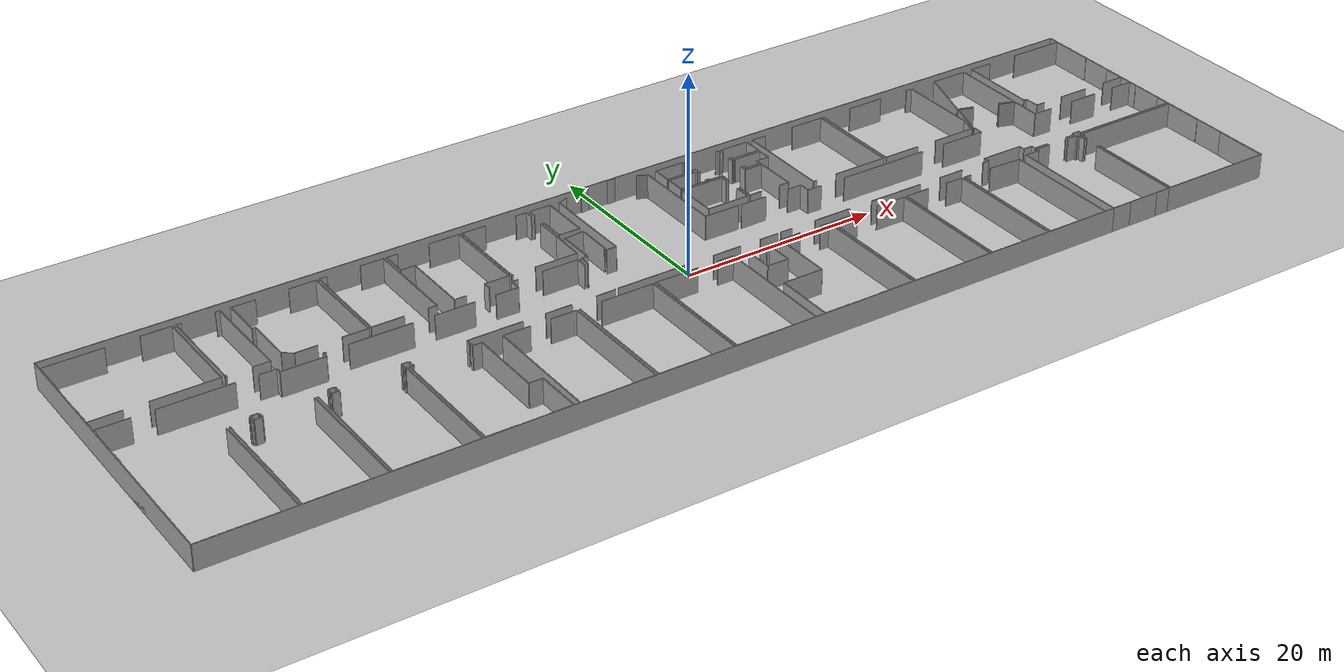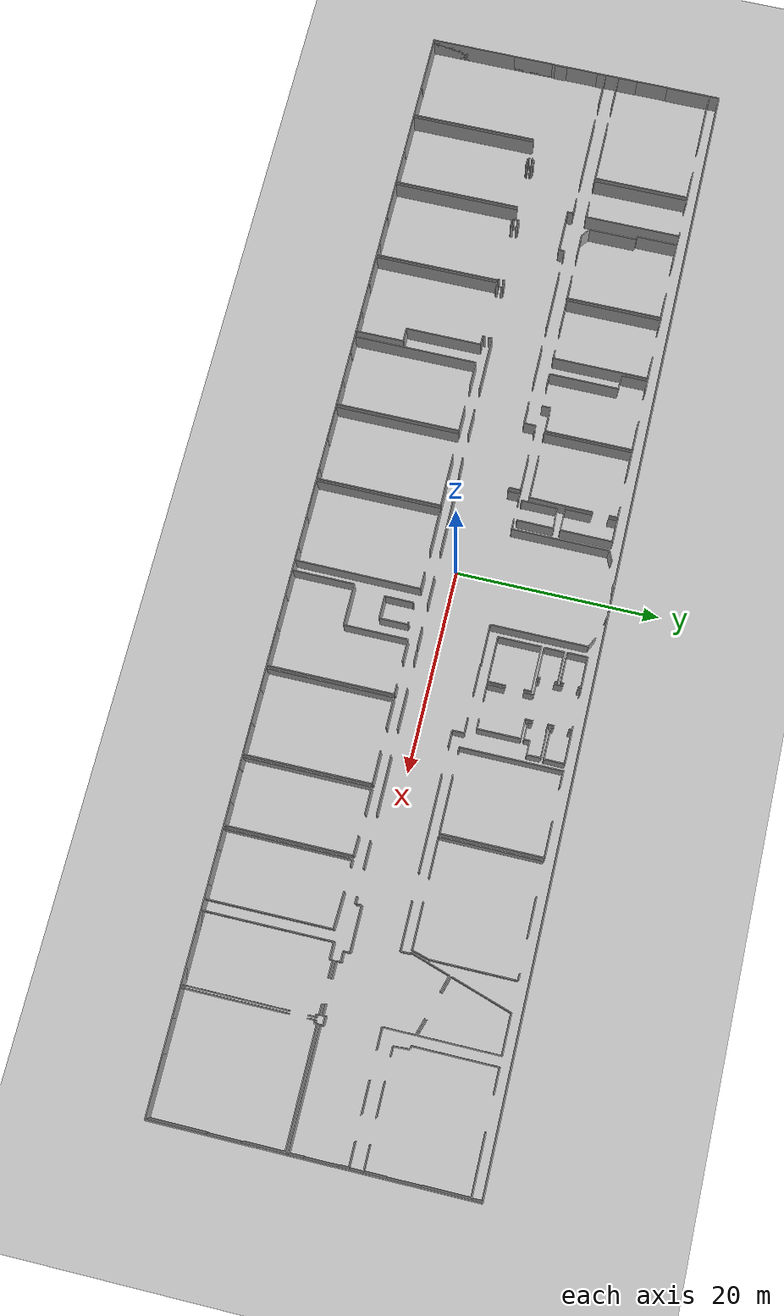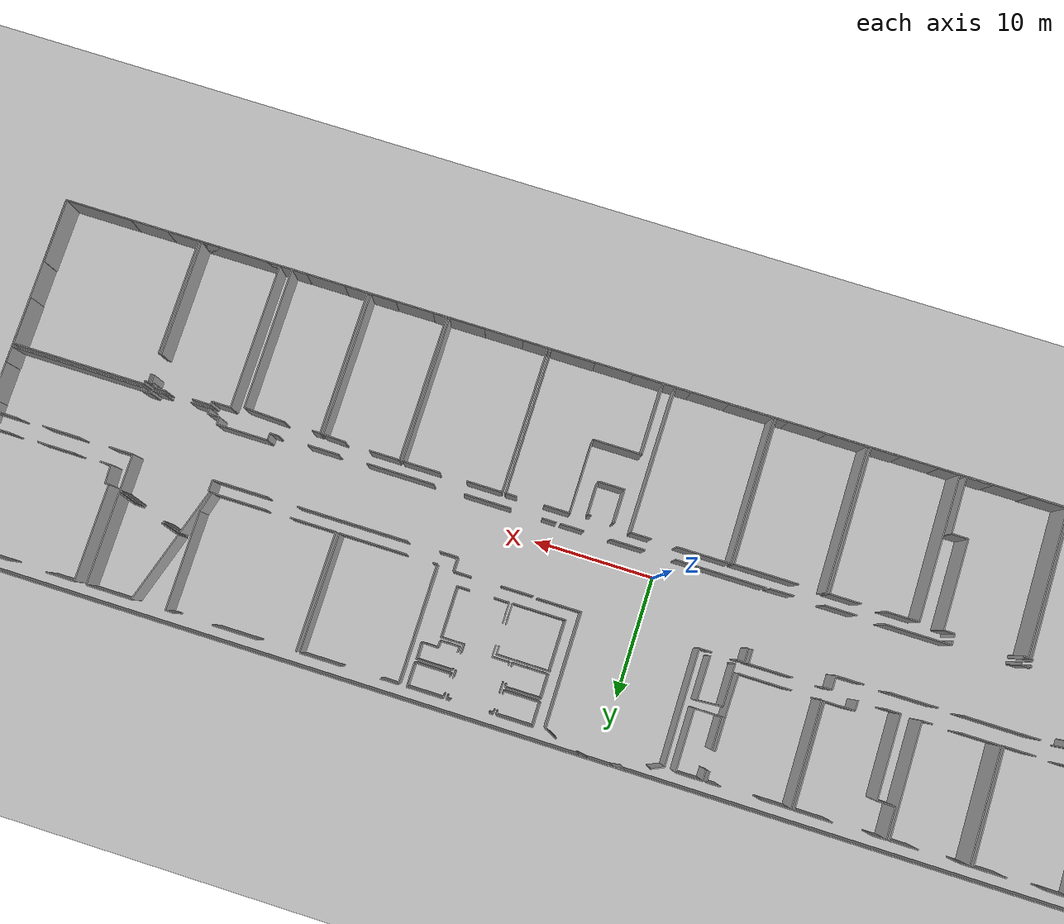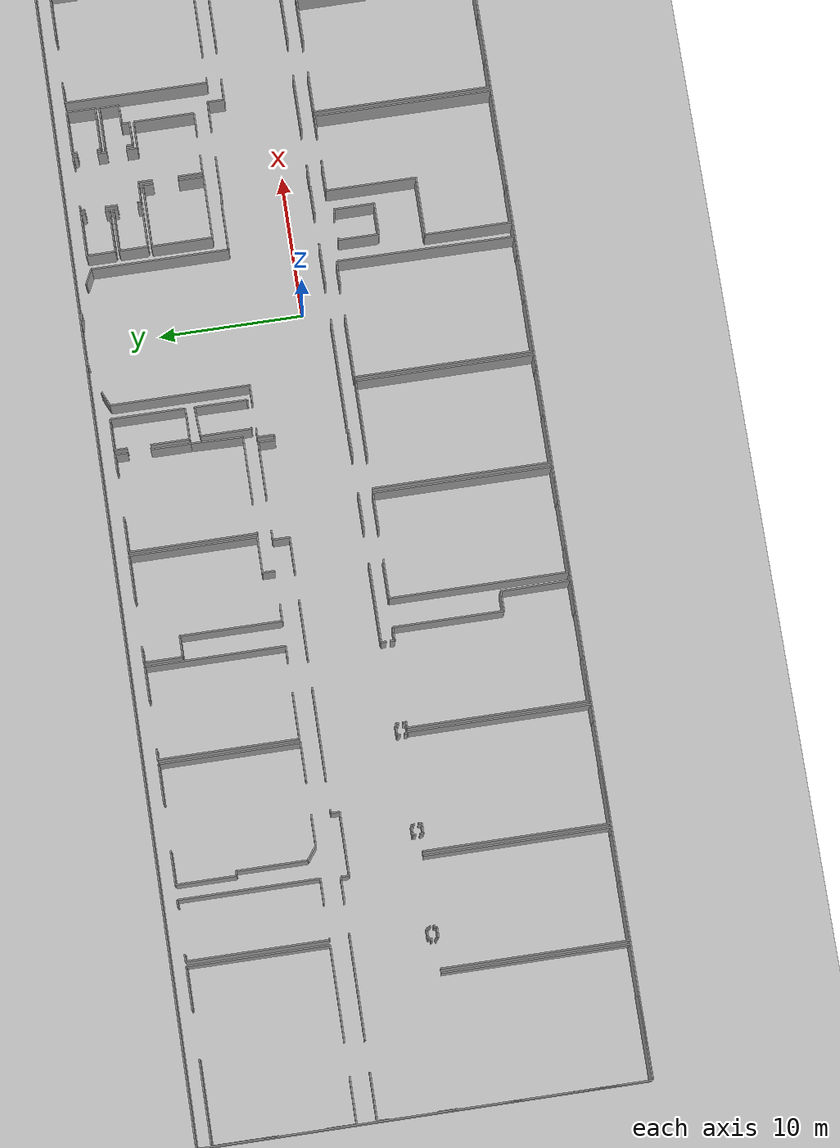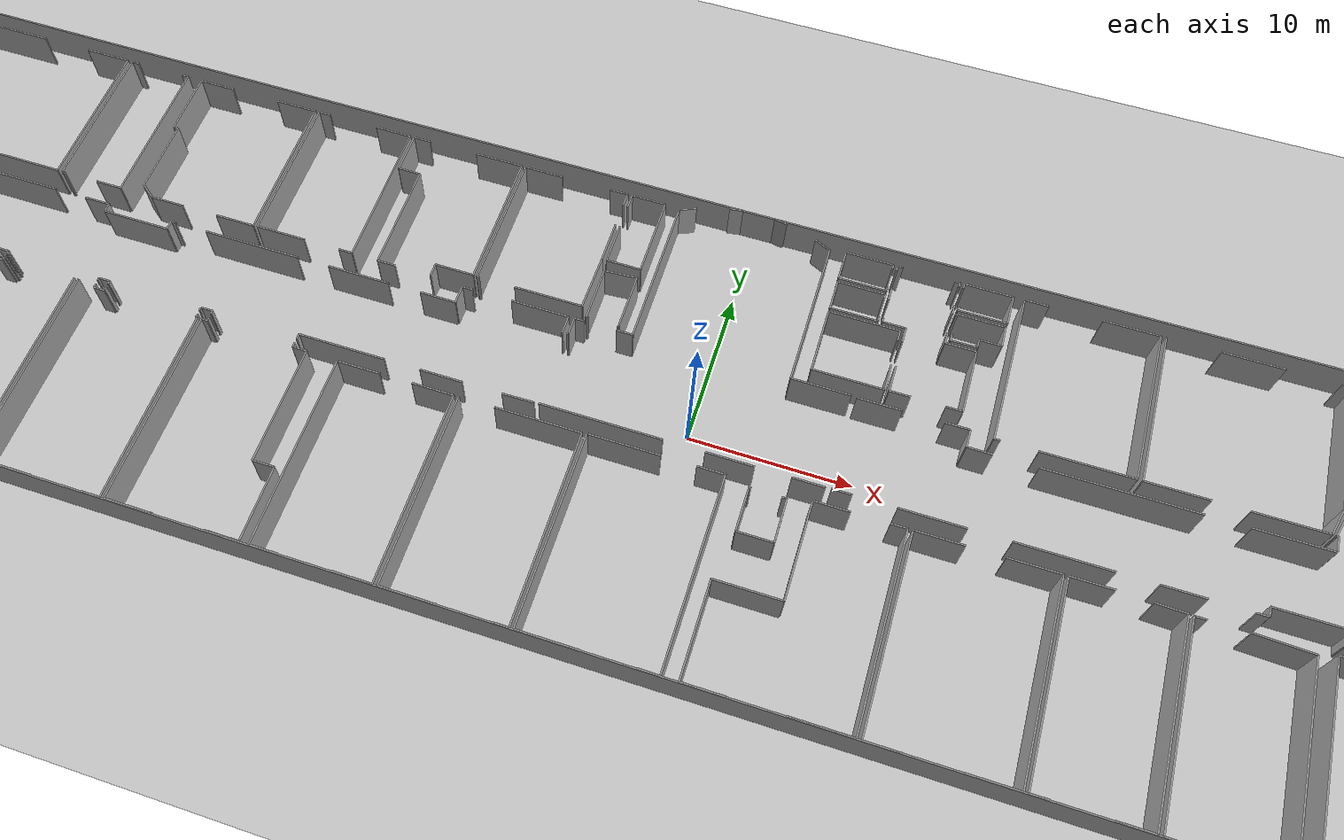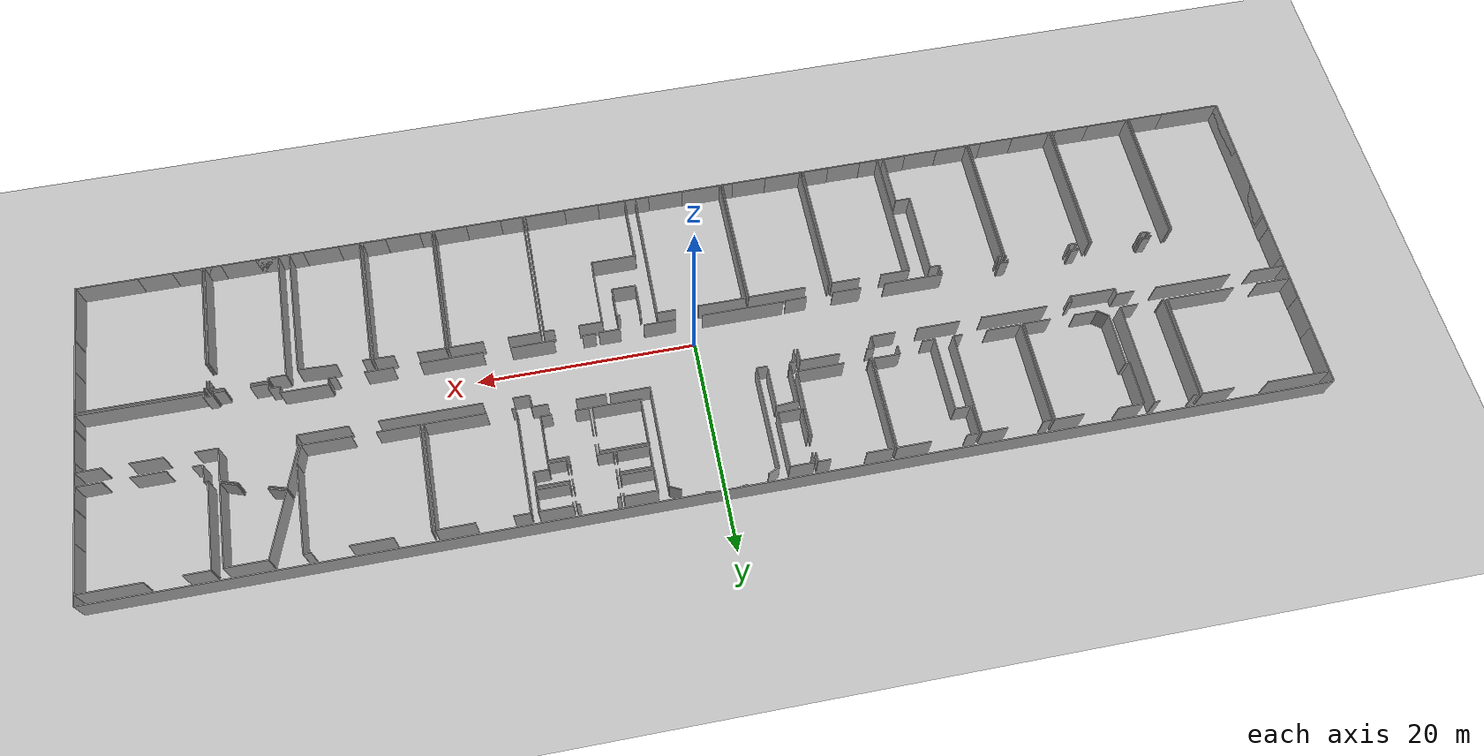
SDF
<sdf version="1.6">
  <world name="default">
    <light name="sun" type="directional">
      <cast_shadows>1</cast_shadows>
      <pose frame="">0 0 10 0 -0 0</pose>
      <diffuse>0.8 0.8 0.8 1</diffuse>
      <specular>0.1 0.1 0.1 1</specular>
      <attenuation>
        <range>1000</range>
        <constant>0.9</constant>
        <linear>0.01</linear>
        <quadratic>0.001</quadratic>
      </attenuation>
      <direction>-0.5 0.5 -1</direction>
    </light>
    <model name="ground_plane">
      <static>1</static>
      <link name="link">
        <collision name="collision">
          <geometry>
            <plane>
              <normal>0 0 1</normal>
              <size>100 100</size>
            </plane>
          </geometry>
          <surface>
            <friction>
              <ode>
                <mu>100</mu>
                <mu2>50</mu2>
              </ode>
              <torsional>
                <ode />
              </torsional>
            </friction>
            <contact>
              <ode />
            </contact>
            <bounce />
          </surface>
          <max_contacts>10</max_contacts>
        </collision>
        <visual name="visual">
          <cast_shadows>0</cast_shadows>
          <geometry>
            <plane>
              <normal>0 0 1</normal>
              <size>100 100</size>
            </plane>
          </geometry>
          <material>
            <script>
              <uri>file://media/materials/scripts/gazebo.material</uri>
              <name>Gazebo/Grey</name>
            </script>
          </material>
        </visual>
        <self_collide>0</self_collide>
        <kinematic>0</kinematic>
        <gravity>1</gravity>
      </link>
    </model>
    <gravity>0 0 -9.8</gravity>
    <magnetic_field>6e-06 2.3e-05 -4.2e-05</magnetic_field>
    <atmosphere type="adiabatic" />
    <physics default="0" name="default_physics" type="ode">
      <max_step_size>0.001</max_step_size>
      <real_time_factor>1</real_time_factor>
      <real_time_update_rate>1000</real_time_update_rate>
    </physics>
    <scene>
      <ambient>0.4 0.4 0.4 1</ambient>
      <background>0.7 0.7 0.7 1</background>
      <shadows>1</shadows>
    </scene>
    <spherical_coordinates>
      <surface_model>EARTH_WGS84</surface_model>
      <latitude_deg>0</latitude_deg>
      <longitude_deg>0</longitude_deg>
      <elevation>0</elevation>
      <heading_deg>0</heading_deg>
    </spherical_coordinates>
  <model name="50056459">
		<static>1</static>
		<link name="Wall_0">
			<collision name="Wall_0_Collision">
				<geometry>
					<box>
						<size>6.43075541853 0.1 2.5</size>
					</box>
				</geometry>
				<pose frame="">3.21537770927 0 1.25 0 0 0</pose>
			</collision>
			<visual name="Wall_0_Visual">
				<pose frame="">3.21537770927 0 1.25 0 0 0</pose>
				<geometry>
					<box>
						<size>6.43075541853 0.1 2.5</size>
					</box>
				</geometry>
				<material>
					<script>
						<uri>file://media/materials/scripts/gazebo.material</uri>
						<name>Gazebo/Grey</name>
					</script>
					<ambient>1 1 1 1</ambient>
				</material>
			</visual>
			<pose frame="">11.8879619199 -10.6324375143 0 0 0 3.14159265359</pose>
		</link>
		<link name="Wall_1">
			<collision name="Wall_1_Collision">
				<geometry>
					<box>
						<size>3.15202385086 0.1 2.5</size>
					</box>
				</geometry>
				<pose frame="">1.57601192543 0 1.25 0 0 0</pose>
			</collision>
			<visual name="Wall_1_Visual">
				<pose frame="">1.57601192543 0 1.25 0 0 0</pose>
				<geometry>
					<box>
						<size>3.15202385086 0.1 2.5</size>
					</box>
				</geometry>
				<material>
					<script>
						<uri>file://media/materials/scripts/gazebo.material</uri>
						<name>Gazebo/Grey</name>
					</script>
					<ambient>1 1 1 1</ambient>
				</material>
			</visual>
			<pose frame="">3.1854455521 -10.6324375143 0 0 0 3.14159265359</pose>
		</link>
		<link name="Wall_2">
			<collision name="Wall_2_Collision">
				<geometry>
					<box>
						<size>1.99124226075 0.1 2.5</size>
					</box>
				</geometry>
				<pose frame="">0.995621130375 0 1.25 0 0 0</pose>
			</collision>
			<visual name="Wall_2_Visual">
				<pose frame="">0.995621130375 0 1.25 0 0 0</pose>
				<geometry>
					<box>
						<size>1.99124226075 0.1 2.5</size>
					</box>
				</geometry>
				<material>
					<script>
						<uri>file://media/materials/scripts/gazebo.material</uri>
						<name>Gazebo/Grey</name>
					</script>
					<ambient>1 1 1 1</ambient>
				</material>
			</visual>
			<pose frame="">0.0334217012374 -10.6324375143 0 0 0 1.57079632679</pose>
		</link>
		<link name="Wall_3">
			<collision name="Wall_3_Collision">
				<geometry>
					<box>
						<size>4.43443129748 0.1 2.5</size>
					</box>
				</geometry>
				<pose frame="">2.21721564874 0 1.25 0 0 0</pose>
			</collision>
			<visual name="Wall_3_Visual">
				<pose frame="">2.21721564874 0 1.25 0 0 0</pose>
				<geometry>
					<box>
						<size>4.43443129748 0.1 2.5</size>
					</box>
				</geometry>
				<material>
					<script>
						<uri>file://media/materials/scripts/gazebo.material</uri>
						<name>Gazebo/Grey</name>
					</script>
					<ambient>1 1 1 1</ambient>
				</material>
			</visual>
			<pose frame="">0.0334217012374 -5.44453572971 0 0 0 1.57079632679</pose>
		</link>
		<link name="Wall_4">
			<collision name="Wall_4_Collision">
				<geometry>
					<box>
						<size>5.72395334852 0.1 2.5</size>
					</box>
				</geometry>
				<pose frame="">2.86197667426 0 1.25 0 0 0</pose>
			</collision>
			<visual name="Wall_4_Visual">
				<pose frame="">2.86197667426 0 1.25 0 0 0</pose>
				<geometry>
					<box>
						<size>5.72395334852 0.1 2.5</size>
					</box>
				</geometry>
				<material>
					<script>
						<uri>file://media/materials/scripts/gazebo.material</uri>
						<name>Gazebo/Grey</name>
					</script>
					<ambient>1 1 1 1</ambient>
				</material>
			</visual>
			<pose frame="">0.0334217012374 -1.01010443223 0 0 0 0.0</pose>
		</link>
		<link name="Wall_5">
			<collision name="Wall_5_Collision">
				<geometry>
					<box>
						<size>2.94849534586 0.1 2.5</size>
					</box>
				</geometry>
				<pose frame="">1.47424767293 0 1.25 0 0 0</pose>
			</collision>
			<visual name="Wall_5_Visual">
				<pose frame="">1.47424767293 0 1.25 0 0 0</pose>
				<geometry>
					<box>
						<size>2.94849534586 0.1 2.5</size>
					</box>
				</geometry>
				<material>
					<script>
						<uri>file://media/materials/scripts/gazebo.material</uri>
						<name>Gazebo/Grey</name>
					</script>
					<ambient>1 1 1 1</ambient>
				</material>
			</visual>
			<pose frame="">8.94573420177 -1.01010443223 0 0 0 0.0</pose>
		</link>
		<link name="Wall_6">
			<collision name="Wall_6_Collision">
				<geometry>
					<box>
						<size>9.62233512331 0.1 2.5</size>
					</box>
				</geometry>
				<pose frame="">4.81116756166 0 1.25 0 0 0</pose>
			</collision>
			<visual name="Wall_6_Visual">
				<pose frame="">4.81116756166 0 1.25 0 0 0</pose>
				<geometry>
					<box>
						<size>9.62233512331 0.1 2.5</size>
					</box>
				</geometry>
				<material>
					<script>
						<uri>file://media/materials/scripts/gazebo.material</uri>
						<name>Gazebo/Grey</name>
					</script>
					<ambient>1 1 1 1</ambient>
				</material>
			</visual>
			<pose frame="">11.8942295476 -1.01010443223 0 0 0 -1.57144768928</pose>
		</link>
		<link name="Wall_7">
			<collision name="Wall_7_Collision">
				<geometry>
					<box>
						<size>1.16222145053 0.1 2.5</size>
					</box>
				</geometry>
				<pose frame="">0.581110725266 0 1.25 0 0 0</pose>
			</collision>
			<visual name="Wall_7_Visual">
				<pose frame="">0.581110725266 0 1.25 0 0 0</pose>
				<geometry>
					<box>
						<size>1.16222145053 0.1 2.5</size>
					</box>
				</geometry>
				<material>
					<script>
						<uri>file://media/materials/scripts/gazebo.material</uri>
						<name>Gazebo/Grey</name>
					</script>
					<ambient>1 1 1 1</ambient>
				</material>
			</visual>
			<pose frame="">46.2513318709 -11.9738792381 0 0 0 1.57079632679</pose>
		</link>
		<link name="Wall_8">
			<collision name="Wall_8_Collision">
				<geometry>
					<box>
						<size>3.63200555617 0.1 2.5</size>
					</box>
				</geometry>
				<pose frame="">1.81600277808 0 1.25 0 0 0</pose>
			</collision>
			<visual name="Wall_8_Visual">
				<pose frame="">1.81600277808 0 1.25 0 0 0</pose>
				<geometry>
					<box>
						<size>3.63200555617 0.1 2.5</size>
					</box>
				</geometry>
				<material>
					<script>
						<uri>file://media/materials/scripts/gazebo.material</uri>
						<name>Gazebo/Grey</name>
					</script>
					<ambient>1 1 1 1</ambient>
				</material>
			</visual>
			<pose frame="">46.2513318709 -10.8116577875 0 0 0 3.14159265359</pose>
		</link>
		<link name="Wall_9">
			<collision name="Wall_9_Collision">
				<geometry>
					<box>
						<size>0.666062489942 0.1 2.5</size>
					</box>
				</geometry>
				<pose frame="">0.333031244971 0 1.25 0 0 0</pose>
			</collision>
			<visual name="Wall_9_Visual">
				<pose frame="">0.333031244971 0 1.25 0 0 0</pose>
				<geometry>
					<box>
						<size>0.666062489942 0.1 2.5</size>
					</box>
				</geometry>
				<material>
					<script>
						<uri>file://media/materials/scripts/gazebo.material</uri>
						<name>Gazebo/Grey</name>
					</script>
					<ambient>1 1 1 1</ambient>
				</material>
			</visual>
			<pose frame="">40.1153243497 -10.8116577875 0 0 0 3.14159265359</pose>
		</link>
		<link name="Wall_10">
			<collision name="Wall_10_Collision">
				<geometry>
					<box>
						<size>1.16222145053 0.1 2.5</size>
					</box>
				</geometry>
				<pose frame="">0.581110725266 0 1.25 0 0 0</pose>
			</collision>
			<visual name="Wall_10_Visual">
				<pose frame="">0.581110725266 0 1.25 0 0 0</pose>
				<geometry>
					<box>
						<size>1.16222145053 0.1 2.5</size>
					</box>
				</geometry>
				<material>
					<script>
						<uri>file://media/materials/scripts/gazebo.material</uri>
						<name>Gazebo/Grey</name>
					</script>
					<ambient>1 1 1 1</ambient>
				</material>
			</visual>
			<pose frame="">39.4492618598 -10.8116577875 0 0 0 -1.57079632679</pose>
		</link>
		<link name="Wall_11">
			<collision name="Wall_11_Collision">
				<geometry>
					<box>
						<size>2.26329118213 0.1 2.5</size>
					</box>
				</geometry>
				<pose frame="">1.13164559106 0 1.25 0 0 0</pose>
			</collision>
			<visual name="Wall_11_Visual">
				<pose frame="">1.13164559106 0 1.25 0 0 0</pose>
				<geometry>
					<box>
						<size>2.26329118213 0.1 2.5</size>
					</box>
				</geometry>
				<material>
					<script>
						<uri>file://media/materials/scripts/gazebo.material</uri>
						<name>Gazebo/Grey</name>
					</script>
					<ambient>1 1 1 1</ambient>
				</material>
			</visual>
			<pose frame="">39.4492618598 -11.9738792381 0 0 0 3.14159265359</pose>
		</link>
		<link name="Wall_12">
			<collision name="Wall_12_Collision">
				<geometry>
					<box>
						<size>3.95148517367 0.1 2.5</size>
					</box>
				</geometry>
				<pose frame="">1.97574258684 0 1.25 0 0 0</pose>
			</collision>
			<visual name="Wall_12_Visual">
				<pose frame="">1.97574258684 0 1.25 0 0 0</pose>
				<geometry>
					<box>
						<size>3.95148517367 0.1 2.5</size>
					</box>
				</geometry>
				<material>
					<script>
						<uri>file://media/materials/scripts/gazebo.material</uri>
						<name>Gazebo/Grey</name>
					</script>
					<ambient>1 1 1 1</ambient>
				</material>
			</visual>
			<pose frame="">35.1035937222 -11.9738792381 0 0 0 3.14159265359</pose>
		</link>
		<link name="Wall_13">
			<collision name="Wall_13_Collision">
				<geometry>
					<box>
						<size>6.18157486851 0.1 2.5</size>
					</box>
				</geometry>
				<pose frame="">3.09078743425 0 1.25 0 0 0</pose>
			</collision>
			<visual name="Wall_13_Visual">
				<pose frame="">3.09078743425 0 1.25 0 0 0</pose>
				<geometry>
					<box>
						<size>6.18157486851 0.1 2.5</size>
					</box>
				</geometry>
				<material>
					<script>
						<uri>file://media/materials/scripts/gazebo.material</uri>
						<name>Gazebo/Grey</name>
					</script>
					<ambient>1 1 1 1</ambient>
				</material>
			</visual>
			<pose frame="">29.0924305691 -11.9738792381 0 0 0 3.14159265359</pose>
		</link>
		<link name="Wall_14">
			<collision name="Wall_14_Collision">
				<geometry>
					<box>
						<size>0.278485944421 0.1 2.5</size>
					</box>
				</geometry>
				<pose frame="">0.139242972211 0 1.25 0 0 0</pose>
			</collision>
			<visual name="Wall_14_Visual">
				<pose frame="">0.139242972211 0 1.25 0 0 0</pose>
				<geometry>
					<box>
						<size>0.278485944421 0.1 2.5</size>
					</box>
				</geometry>
				<material>
					<script>
						<uri>file://media/materials/scripts/gazebo.material</uri>
						<name>Gazebo/Grey</name>
					</script>
					<ambient>1 1 1 1</ambient>
				</material>
			</visual>
			<pose frame="">20.8169598618 -11.9738792381 0 0 0 3.14159265359</pose>
		</link>
		<link name="Wall_15">
			<collision name="Wall_15_Collision">
				<geometry>
					<box>
						<size>0.587801841327 0.1 2.5</size>
					</box>
				</geometry>
				<pose frame="">0.293900920664 0 1.25 0 0 0</pose>
			</collision>
			<visual name="Wall_15_Visual">
				<pose frame="">0.293900920664 0 1.25 0 0 0</pose>
				<geometry>
					<box>
						<size>0.587801841327 0.1 2.5</size>
					</box>
				</geometry>
				<material>
					<script>
						<uri>file://media/materials/scripts/gazebo.material</uri>
						<name>Gazebo/Grey</name>
					</script>
					<ambient>1 1 1 1</ambient>
				</material>
			</visual>
			<pose frame="">20.5384739174 -11.9738792381 0 0 0 -1.57079632679</pose>
		</link>
		<link name="Wall_16">
			<collision name="Wall_16_Collision">
				<geometry>
					<box>
						<size>4.29925381351 0.1 2.5</size>
					</box>
				</geometry>
				<pose frame="">2.14962690676 0 1.25 0 0 0</pose>
			</collision>
			<visual name="Wall_16_Visual">
				<pose frame="">2.14962690676 0 1.25 0 0 0</pose>
				<geometry>
					<box>
						<size>4.29925381351 0.1 2.5</size>
					</box>
				</geometry>
				<material>
					<script>
						<uri>file://media/materials/scripts/gazebo.material</uri>
						<name>Gazebo/Grey</name>
					</script>
					<ambient>1 1 1 1</ambient>
				</material>
			</visual>
			<pose frame="">20.5384739174 -12.5616810794 0 0 0 3.14159265359</pose>
		</link>
		<link name="Wall_17">
			<collision name="Wall_17_Collision">
				<geometry>
					<box>
						<size>0.567982586159 0.1 2.5</size>
					</box>
				</geometry>
				<pose frame="">0.283991293079 0 1.25 0 0 0</pose>
			</collision>
			<visual name="Wall_17_Visual">
				<pose frame="">0.283991293079 0 1.25 0 0 0</pose>
				<geometry>
					<box>
						<size>0.567982586159 0.1 2.5</size>
					</box>
				</geometry>
				<material>
					<script>
						<uri>file://media/materials/scripts/gazebo.material</uri>
						<name>Gazebo/Grey</name>
					</script>
					<ambient>1 1 1 1</ambient>
				</material>
			</visual>
			<pose frame="">16.2392201038 -12.5616810794 0 0 0 1.57079632679</pose>
		</link>
		<link name="Wall_18">
			<collision name="Wall_18_Collision">
				<geometry>
					<box>
						<size>1.67074627118 0.1 2.5</size>
					</box>
				</geometry>
				<pose frame="">0.835373135592 0 1.25 0 0 0</pose>
			</collision>
			<visual name="Wall_18_Visual">
				<pose frame="">0.835373135592 0 1.25 0 0 0</pose>
				<geometry>
					<box>
						<size>1.67074627118 0.1 2.5</size>
					</box>
				</geometry>
				<material>
					<script>
						<uri>file://media/materials/scripts/gazebo.material</uri>
						<name>Gazebo/Grey</name>
					</script>
					<ambient>1 1 1 1</ambient>
				</material>
			</visual>
			<pose frame="">16.2392201038 -11.9936984932 0 0 0 3.14159265359</pose>
		</link>
		<link name="Wall_19">
			<collision name="Wall_19_Collision">
				<geometry>
					<box>
						<size>7.14899167422 0.1 2.5</size>
					</box>
				</geometry>
				<pose frame="">3.57449583711 0 1.25 0 0 0</pose>
			</collision>
			<visual name="Wall_19_Visual">
				<pose frame="">3.57449583711 0 1.25 0 0 0</pose>
				<geometry>
					<box>
						<size>7.14899167422 0.1 2.5</size>
					</box>
				</geometry>
				<material>
					<script>
						<uri>file://media/materials/scripts/gazebo.material</uri>
						<name>Gazebo/Grey</name>
					</script>
					<ambient>1 1 1 1</ambient>
				</material>
			</visual>
			<pose frame="">12.4996485047 -11.9936984932 0 0 0 3.14159265359</pose>
		</link>
		<link name="Wall_20">
			<collision name="Wall_20_Collision">
				<geometry>
					<box>
						<size>3.22962385764 0.1 2.5</size>
					</box>
				</geometry>
				<pose frame="">1.61481192882 0 1.25 0 0 0</pose>
			</collision>
			<visual name="Wall_20_Visual">
				<pose frame="">1.61481192882 0 1.25 0 0 0</pose>
				<geometry>
					<box>
						<size>3.22962385764 0.1 2.5</size>
					</box>
				</geometry>
				<material>
					<script>
						<uri>file://media/materials/scripts/gazebo.material</uri>
						<name>Gazebo/Grey</name>
					</script>
					<ambient>1 1 1 1</ambient>
				</material>
			</visual>
			<pose frame="">3.27234536323 -11.9936984932 0 0 0 3.14159265359</pose>
		</link>
		<link name="Wall_21">
			<collision name="Wall_21_Collision">
				<geometry>
					<box>
						<size>0.873571785512 0.1 2.5</size>
					</box>
				</geometry>
				<pose frame="">0.436785892756 0 1.25 0 0 0</pose>
			</collision>
			<visual name="Wall_21_Visual">
				<pose frame="">0.436785892756 0 1.25 0 0 0</pose>
				<geometry>
					<box>
						<size>0.873571785512 0.1 2.5</size>
					</box>
				</geometry>
				<material>
					<script>
						<uri>file://media/materials/scripts/gazebo.material</uri>
						<name>Gazebo/Grey</name>
					</script>
					<ambient>1 1 1 1</ambient>
				</material>
			</visual>
			<pose frame="">0.0427215055858 -11.9936984932 0 0 0 -1.57079632679</pose>
		</link>
		<link name="Wall_22">
			<collision name="Wall_22_Collision">
				<geometry>
					<box>
						<size>1.27419177247 0.1 2.5</size>
					</box>
				</geometry>
				<pose frame="">0.637095886234 0 1.25 0 0 0</pose>
			</collision>
			<visual name="Wall_22_Visual">
				<pose frame="">0.637095886234 0 1.25 0 0 0</pose>
				<geometry>
					<box>
						<size>1.27419177247 0.1 2.5</size>
					</box>
				</geometry>
				<material>
					<script>
						<uri>file://media/materials/scripts/gazebo.material</uri>
						<name>Gazebo/Grey</name>
					</script>
					<ambient>1 1 1 1</ambient>
				</material>
			</visual>
			<pose frame="">0.0427215055858 -16.0676565001 0 0 0 -1.57079632679</pose>
		</link>
		<link name="Wall_23">
			<collision name="Wall_23_Collision">
				<geometry>
					<box>
						<size>0.219028178915 0.1 2.5</size>
					</box>
				</geometry>
				<pose frame="">0.109514089458 0 1.25 0 0 0</pose>
			</collision>
			<visual name="Wall_23_Visual">
				<pose frame="">0.109514089458 0 1.25 0 0 0</pose>
				<geometry>
					<box>
						<size>0.219028178915 0.1 2.5</size>
					</box>
				</geometry>
				<material>
					<script>
						<uri>file://media/materials/scripts/gazebo.material</uri>
						<name>Gazebo/Grey</name>
					</script>
					<ambient>1 1 1 1</ambient>
				</material>
			</visual>
			<pose frame="">11.1150109683 -17.3418482726 0 0 0 0.0</pose>
		</link>
		<link name="Wall_24">
			<collision name="Wall_24_Collision">
				<geometry>
					<box>
						<size>0.210897202436 0.1 2.5</size>
					</box>
				</geometry>
				<pose frame="">0.105448601218 0 1.25 0 0 0</pose>
			</collision>
			<visual name="Wall_24_Visual">
				<pose frame="">0.105448601218 0 1.25 0 0 0</pose>
				<geometry>
					<box>
						<size>0.210897202436 0.1 2.5</size>
					</box>
				</geometry>
				<material>
					<script>
						<uri>file://media/materials/scripts/gazebo.material</uri>
						<name>Gazebo/Grey</name>
					</script>
					<ambient>1 1 1 1</ambient>
				</material>
			</visual>
			<pose frame="">11.3340391473 -17.3418482726 0 0 0 1.57079632679</pose>
		</link>
		<link name="Wall_25">
			<collision name="Wall_25_Collision">
				<geometry>
					<box>
						<size>0.707394953713 0.1 2.5</size>
					</box>
				</geometry>
				<pose frame="">0.353697476856 0 1.25 0 0 0</pose>
			</collision>
			<visual name="Wall_25_Visual">
				<pose frame="">0.353697476856 0 1.25 0 0 0</pose>
				<geometry>
					<box>
						<size>0.707394953713 0.1 2.5</size>
					</box>
				</geometry>
				<material>
					<script>
						<uri>file://media/materials/scripts/gazebo.material</uri>
						<name>Gazebo/Grey</name>
					</script>
					<ambient>1 1 1 1</ambient>
				</material>
			</visual>
			<pose frame="">11.3340391473 -17.1309510702 0 0 0 0.0</pose>
		</link>
		<link name="Wall_26">
			<collision name="Wall_26_Collision">
				<geometry>
					<box>
						<size>0.227497946081 0.1 2.5</size>
					</box>
				</geometry>
				<pose frame="">0.113748973041 0 1.25 0 0 0</pose>
			</collision>
			<visual name="Wall_26_Visual">
				<pose frame="">0.113748973041 0 1.25 0 0 0</pose>
				<geometry>
					<box>
						<size>0.227497946081 0.1 2.5</size>
					</box>
				</geometry>
				<material>
					<script>
						<uri>file://media/materials/scripts/gazebo.material</uri>
						<name>Gazebo/Grey</name>
					</script>
					<ambient>1 1 1 1</ambient>
				</material>
			</visual>
			<pose frame="">12.041434101 -17.1309510702 0 0 0 -1.57079632679</pose>
		</link>
		<link name="Wall_27">
			<collision name="Wall_27_Collision">
				<geometry>
					<box>
						<size>0.151608832273 0.1 2.5</size>
					</box>
				</geometry>
				<pose frame="">0.0758044161366 0 1.25 0 0 0</pose>
			</collision>
			<visual name="Wall_27_Visual">
				<pose frame="">0.0758044161366 0 1.25 0 0 0</pose>
				<geometry>
					<box>
						<size>0.151608832273 0.1 2.5</size>
					</box>
				</geometry>
				<material>
					<script>
						<uri>file://media/materials/scripts/gazebo.material</uri>
						<name>Gazebo/Grey</name>
					</script>
					<ambient>1 1 1 1</ambient>
				</material>
			</visual>
			<pose frame="">12.041434101 -17.3584490162 0 0 0 0.0</pose>
		</link>
		<link name="Wall_28">
			<collision name="Wall_28_Collision">
				<geometry>
					<box>
						<size>0.199547714433 0.1 2.5</size>
					</box>
				</geometry>
				<pose frame="">0.0997738572167 0 1.25 0 0 0</pose>
			</collision>
			<visual name="Wall_28_Visual">
				<pose frame="">0.0997738572167 0 1.25 0 0 0</pose>
				<geometry>
					<box>
						<size>0.199547714433 0.1 2.5</size>
					</box>
				</geometry>
				<material>
					<script>
						<uri>file://media/materials/scripts/gazebo.material</uri>
						<name>Gazebo/Grey</name>
					</script>
					<ambient>1 1 1 1</ambient>
				</material>
			</visual>
			<pose frame="">18.2707784563 -17.3584490162 0 0 0 1.57079632679</pose>
		</link>
		<link name="Wall_29">
			<collision name="Wall_29_Collision">
				<geometry>
					<box>
						<size>0.710274674549 0.1 2.5</size>
					</box>
				</geometry>
				<pose frame="">0.355137337275 0 1.25 0 0 0</pose>
			</collision>
			<visual name="Wall_29_Visual">
				<pose frame="">0.355137337275 0 1.25 0 0 0</pose>
				<geometry>
					<box>
						<size>0.710274674549 0.1 2.5</size>
					</box>
				</geometry>
				<material>
					<script>
						<uri>file://media/materials/scripts/gazebo.material</uri>
						<name>Gazebo/Grey</name>
					</script>
					<ambient>1 1 1 1</ambient>
				</material>
			</visual>
			<pose frame="">18.2707784563 -17.1589013018 0 0 0 0.0</pose>
		</link>
		<link name="Wall_30">
			<collision name="Wall_30_Collision">
				<geometry>
					<box>
						<size>0.197684365657 0.1 2.5</size>
					</box>
				</geometry>
				<pose frame="">0.0988421828284 0 1.25 0 0 0</pose>
			</collision>
			<visual name="Wall_30_Visual">
				<pose frame="">0.0988421828284 0 1.25 0 0 0</pose>
				<geometry>
					<box>
						<size>0.197684365657 0.1 2.5</size>
					</box>
				</geometry>
				<material>
					<script>
						<uri>file://media/materials/scripts/gazebo.material</uri>
						<name>Gazebo/Grey</name>
					</script>
					<ambient>1 1 1 1</ambient>
				</material>
			</visual>
			<pose frame="">18.9810531308 -17.1589013018 0 0 0 -1.57079632679</pose>
		</link>
		<link name="Wall_31">
			<collision name="Wall_31_Collision">
				<geometry>
					<box>
						<size>0.220552737005 0.1 2.5</size>
					</box>
				</geometry>
				<pose frame="">0.110276368503 0 1.25 0 0 0</pose>
			</collision>
			<visual name="Wall_31_Visual">
				<pose frame="">0.110276368503 0 1.25 0 0 0</pose>
				<geometry>
					<box>
						<size>0.220552737005 0.1 2.5</size>
					</box>
				</geometry>
				<material>
					<script>
						<uri>file://media/materials/scripts/gazebo.material</uri>
						<name>Gazebo/Grey</name>
					</script>
					<ambient>1 1 1 1</ambient>
				</material>
			</visual>
			<pose frame="">25.0794548858 -17.3565856675 0 0 0 1.57079632679</pose>
		</link>
		<link name="Wall_32">
			<collision name="Wall_32_Collision">
				<geometry>
					<box>
						<size>0.765158765786 0.1 2.5</size>
					</box>
				</geometry>
				<pose frame="">0.382579382893 0 1.25 0 0 0</pose>
			</collision>
			<visual name="Wall_32_Visual">
				<pose frame="">0.382579382893 0 1.25 0 0 0</pose>
				<geometry>
					<box>
						<size>0.765158765786 0.1 2.5</size>
					</box>
				</geometry>
				<material>
					<script>
						<uri>file://media/materials/scripts/gazebo.material</uri>
						<name>Gazebo/Grey</name>
					</script>
					<ambient>1 1 1 1</ambient>
				</material>
			</visual>
			<pose frame="">25.0794548858 -17.1360329305 0 0 0 0.0</pose>
		</link>
		<link name="Wall_33">
			<collision name="Wall_33_Collision">
				<geometry>
					<box>
						<size>0.222754876468 0.1 2.5</size>
					</box>
				</geometry>
				<pose frame="">0.111377438234 0 1.25 0 0 0</pose>
			</collision>
			<visual name="Wall_33_Visual">
				<pose frame="">0.111377438234 0 1.25 0 0 0</pose>
				<geometry>
					<box>
						<size>0.222754876468 0.1 2.5</size>
					</box>
				</geometry>
				<material>
					<script>
						<uri>file://media/materials/scripts/gazebo.material</uri>
						<name>Gazebo/Grey</name>
					</script>
					<ambient>1 1 1 1</ambient>
				</material>
			</visual>
			<pose frame="">25.8446136516 -17.1360329305 0 0 0 -1.57079632679</pose>
		</link>
		<link name="Wall_34">
			<collision name="Wall_34_Collision">
				<geometry>
					<box>
						<size>0.353019895483 0.1 2.5</size>
					</box>
				</geometry>
				<pose frame="">0.176509947742 0 1.25 0 0 0</pose>
			</collision>
			<visual name="Wall_34_Visual">
				<pose frame="">0.176509947742 0 1.25 0 0 0</pose>
				<geometry>
					<box>
						<size>0.353019895483 0.1 2.5</size>
					</box>
				</geometry>
				<material>
					<script>
						<uri>file://media/materials/scripts/gazebo.material</uri>
						<name>Gazebo/Grey</name>
					</script>
					<ambient>1 1 1 1</ambient>
				</material>
			</visual>
			<pose frame="">31.4314414697 -17.3587878069 0 0 0 1.57079632679</pose>
		</link>
		<link name="Wall_35">
			<collision name="Wall_35_Collision">
				<geometry>
					<box>
						<size>5.46875926381 0.1 2.5</size>
					</box>
				</geometry>
				<pose frame="">2.7343796319 0 1.25 0 0 0</pose>
			</collision>
			<visual name="Wall_35_Visual">
				<pose frame="">2.7343796319 0 1.25 0 0 0</pose>
				<geometry>
					<box>
						<size>5.46875926381 0.1 2.5</size>
					</box>
				</geometry>
				<material>
					<script>
						<uri>file://media/materials/scripts/gazebo.material</uri>
						<name>Gazebo/Grey</name>
					</script>
					<ambient>1 1 1 1</ambient>
				</material>
			</visual>
			<pose frame="">31.4314414697 -17.0057679114 0 0 0 0.0</pose>
		</link>
		<link name="Wall_36">
			<collision name="Wall_36_Collision">
				<geometry>
					<box>
						<size>2.65374744848 0.1 2.5</size>
					</box>
				</geometry>
				<pose frame="">1.32687372424 0 1.25 0 0 0</pose>
			</collision>
			<visual name="Wall_36_Visual">
				<pose frame="">1.32687372424 0 1.25 0 0 0</pose>
				<geometry>
					<box>
						<size>2.65374744848 0.1 2.5</size>
					</box>
				</geometry>
				<material>
					<script>
						<uri>file://media/materials/scripts/gazebo.material</uri>
						<name>Gazebo/Grey</name>
					</script>
					<ambient>1 1 1 1</ambient>
				</material>
			</visual>
			<pose frame="">39.1521424276 -17.0057679114 0 0 0 0.0</pose>
		</link>
		<link name="Wall_37">
			<collision name="Wall_37_Collision">
				<geometry>
					<box>
						<size>1.96681117286 0.1 2.5</size>
					</box>
				</geometry>
				<pose frame="">0.983405586429 0 1.25 0 0 0</pose>
			</collision>
			<visual name="Wall_37_Visual">
				<pose frame="">0.983405586429 0 1.25 0 0 0</pose>
				<geometry>
					<box>
						<size>1.96681117286 0.1 2.5</size>
					</box>
				</geometry>
				<material>
					<script>
						<uri>file://media/materials/scripts/gazebo.material</uri>
						<name>Gazebo/Grey</name>
					</script>
					<ambient>1 1 1 1</ambient>
				</material>
			</visual>
			<pose frame="">44.2848213303 -17.0057679114 0 0 0 0.0174846509602</pose>
		</link>
		<link name="Wall_38">
			<collision name="Wall_38_Collision">
				<geometry>
					<box>
						<size>1.66464803883 0.1 2.5</size>
					</box>
				</geometry>
				<pose frame="">0.832324019413 0 1.25 0 0 0</pose>
			</collision>
			<visual name="Wall_38_Visual">
				<pose frame="">0.832324019413 0 1.25 0 0 0</pose>
				<geometry>
					<box>
						<size>1.66464803883 0.1 2.5</size>
					</box>
				</geometry>
				<material>
					<script>
						<uri>file://media/materials/scripts/gazebo.material</uri>
						<name>Gazebo/Grey</name>
					</script>
					<ambient>1 1 1 1</ambient>
				</material>
			</visual>
			<pose frame="">16.3395021471 -10.6348090491 0 0 0 3.14159265359</pose>
		</link>
		<link name="Wall_39">
			<collision name="Wall_39_Collision">
				<geometry>
					<box>
						<size>0.14737394869 0.1 2.5</size>
					</box>
				</geometry>
				<pose frame="">0.0736869743451 0 1.25 0 0 0</pose>
			</collision>
			<visual name="Wall_39_Visual">
				<pose frame="">0.0736869743451 0 1.25 0 0 0</pose>
				<geometry>
					<box>
						<size>0.14737394869 0.1 2.5</size>
					</box>
				</geometry>
				<material>
					<script>
						<uri>file://media/materials/scripts/gazebo.material</uri>
						<name>Gazebo/Grey</name>
					</script>
					<ambient>1 1 1 1</ambient>
				</material>
			</visual>
			<pose frame="">12.3722632065 -10.6348090491 0 0 0 3.14159265359</pose>
		</link>
		<link name="Wall_40">
			<collision name="Wall_40_Collision">
				<geometry>
					<box>
						<size>9.6150490823 0.1 2.5</size>
					</box>
				</geometry>
				<pose frame="">4.80752454115 0 1.25 0 0 0</pose>
			</collision>
			<visual name="Wall_40_Visual">
				<pose frame="">4.80752454115 0 1.25 0 0 0</pose>
				<geometry>
					<box>
						<size>9.6150490823 0.1 2.5</size>
					</box>
				</geometry>
				<material>
					<script>
						<uri>file://media/materials/scripts/gazebo.material</uri>
						<name>Gazebo/Grey</name>
					</script>
					<ambient>1 1 1 1</ambient>
				</material>
			</visual>
			<pose frame="">12.2248892578 -10.6348090491 0 0 0 1.57079632679</pose>
		</link>
		<link name="Wall_41">
			<collision name="Wall_41_Collision">
				<geometry>
					<box>
						<size>0.486503426021 0.1 2.5</size>
					</box>
				</geometry>
				<pose frame="">0.24325171301 0 1.25 0 0 0</pose>
			</collision>
			<visual name="Wall_41_Visual">
				<pose frame="">0.24325171301 0 1.25 0 0 0</pose>
				<geometry>
					<box>
						<size>0.486503426021 0.1 2.5</size>
					</box>
				</geometry>
				<material>
					<script>
						<uri>file://media/materials/scripts/gazebo.material</uri>
						<name>Gazebo/Grey</name>
					</script>
					<ambient>1 1 1 1</ambient>
				</material>
			</visual>
			<pose frame="">12.2248892578 -1.0197599668 0 0 0 0.0</pose>
		</link>
		<link name="Wall_42">
			<collision name="Wall_42_Collision">
				<geometry>
					<box>
						<size>0.44567914828 0.1 2.5</size>
					</box>
				</geometry>
				<pose frame="">0.22283957414 0 1.25 0 0 0</pose>
			</collision>
			<visual name="Wall_42_Visual">
				<pose frame="">0.22283957414 0 1.25 0 0 0</pose>
				<geometry>
					<box>
						<size>0.44567914828 0.1 2.5</size>
					</box>
				</geometry>
				<material>
					<script>
						<uri>file://media/materials/scripts/gazebo.material</uri>
						<name>Gazebo/Grey</name>
					</script>
					<ambient>1 1 1 1</ambient>
				</material>
			</visual>
			<pose frame="">15.8807795574 -1.0197599668 0 0 0 0.0</pose>
		</link>
		<link name="Wall_43">
			<collision name="Wall_43_Collision">
				<geometry>
					<box>
						<size>9.61505792944 0.1 2.5</size>
					</box>
				</geometry>
				<pose frame="">4.80752896472 0 1.25 0 0 0</pose>
			</collision>
			<visual name="Wall_43_Visual">
				<pose frame="">4.80752896472 0 1.25 0 0 0</pose>
				<geometry>
					<box>
						<size>9.61505792944 0.1 2.5</size>
					</box>
				</geometry>
				<material>
					<script>
						<uri>file://media/materials/scripts/gazebo.material</uri>
						<name>Gazebo/Grey</name>
					</script>
					<ambient>1 1 1 1</ambient>
				</material>
			</visual>
			<pose frame="">16.3264587057 -1.0197599668 0 0 0 -1.56943976238</pose>
		</link>
		<link name="Wall_44">
			<collision name="Wall_44_Collision">
				<geometry>
					<box>
						<size>2.52822549908 0.1 2.5</size>
					</box>
				</geometry>
				<pose frame="">1.26411274954 0 1.25 0 0 0</pose>
			</collision>
			<visual name="Wall_44_Visual">
				<pose frame="">1.26411274954 0 1.25 0 0 0</pose>
				<geometry>
					<box>
						<size>2.52822549908 0.1 2.5</size>
					</box>
				</geometry>
				<material>
					<script>
						<uri>file://media/materials/scripts/gazebo.material</uri>
						<name>Gazebo/Grey</name>
					</script>
					<ambient>1 1 1 1</ambient>
				</material>
			</visual>
			<pose frame="">25.5171724529 -10.6571692344 0 0 0 3.14159265359</pose>
		</link>
		<link name="Wall_45">
			<collision name="Wall_45_Collision">
				<geometry>
					<box>
						<size>2.13793862807 0.1 2.5</size>
					</box>
				</geometry>
				<pose frame="">1.06896931403 0 1.25 0 0 0</pose>
			</collision>
			<visual name="Wall_45_Visual">
				<pose frame="">1.06896931403 0 1.25 0 0 0</pose>
				<geometry>
					<box>
						<size>2.13793862807 0.1 2.5</size>
					</box>
				</geometry>
				<material>
					<script>
						<uri>file://media/materials/scripts/gazebo.material</uri>
						<name>Gazebo/Grey</name>
					</script>
					<ambient>1 1 1 1</ambient>
				</material>
			</visual>
			<pose frame="">20.679919029 -10.6571692344 0 0 0 3.14159265359</pose>
		</link>
		<link name="Wall_46">
			<collision name="Wall_46_Collision">
				<geometry>
					<box>
						<size>1.11421485196 0.1 2.5</size>
					</box>
				</geometry>
				<pose frame="">0.557107425978 0 1.25 0 0 0</pose>
			</collision>
			<visual name="Wall_46_Visual">
				<pose frame="">0.557107425978 0 1.25 0 0 0</pose>
				<geometry>
					<box>
						<size>1.11421485196 0.1 2.5</size>
					</box>
				</geometry>
				<material>
					<script>
						<uri>file://media/materials/scripts/gazebo.material</uri>
						<name>Gazebo/Grey</name>
					</script>
					<ambient>1 1 1 1</ambient>
				</material>
			</visual>
			<pose frame="">18.541980401 -10.6571692344 0 0 0 2.49781788876</pose>
		</link>
		<link name="Wall_47">
			<collision name="Wall_47_Collision">
				<geometry>
					<box>
						<size>4.82624272659 0.1 2.5</size>
					</box>
				</geometry>
				<pose frame="">2.41312136329 0 1.25 0 0 0</pose>
			</collision>
			<visual name="Wall_47_Visual">
				<pose frame="">2.41312136329 0 1.25 0 0 0</pose>
				<geometry>
					<box>
						<size>4.82624272659 0.1 2.5</size>
					</box>
				</geometry>
				<material>
					<script>
						<uri>file://media/materials/scripts/gazebo.material</uri>
						<name>Gazebo/Grey</name>
					</script>
					<ambient>1 1 1 1</ambient>
				</material>
			</visual>
			<pose frame="">17.6507914997 -9.98839641898 0 0 0 1.57079632679</pose>
		</link>
		<link name="Wall_48">
			<collision name="Wall_48_Collision">
				<geometry>
					<box>
						<size>0.318124454759 0.1 2.5</size>
					</box>
				</geometry>
				<pose frame="">0.159062227379 0 1.25 0 0 0</pose>
			</collision>
			<visual name="Wall_48_Visual">
				<pose frame="">0.159062227379 0 1.25 0 0 0</pose>
				<geometry>
					<box>
						<size>0.318124454759 0.1 2.5</size>
					</box>
				</geometry>
				<material>
					<script>
						<uri>file://media/materials/scripts/gazebo.material</uri>
						<name>Gazebo/Grey</name>
					</script>
					<ambient>1 1 1 1</ambient>
				</material>
			</visual>
			<pose frame="">17.6507914997 -5.16215369239 0 0 0 3.14159265359</pose>
		</link>
		<link name="Wall_49">
			<collision name="Wall_49_Collision">
				<geometry>
					<box>
						<size>4.10123065717 0.1 2.5</size>
					</box>
				</geometry>
				<pose frame="">2.05061532858 0 1.25 0 0 0</pose>
			</collision>
			<visual name="Wall_49_Visual">
				<pose frame="">2.05061532858 0 1.25 0 0 0</pose>
				<geometry>
					<box>
						<size>4.10123065717 0.1 2.5</size>
					</box>
				</geometry>
				<material>
					<script>
						<uri>file://media/materials/scripts/gazebo.material</uri>
						<name>Gazebo/Grey</name>
					</script>
					<ambient>1 1 1 1</ambient>
				</material>
			</visual>
			<pose frame="">17.332667045 -5.16215369239 0 0 0 1.57079632679</pose>
		</link>
		<link name="Wall_50">
			<collision name="Wall_50_Collision">
				<geometry>
					<box>
						<size>2.29886420422 0.1 2.5</size>
					</box>
				</geometry>
				<pose frame="">1.14943210211 0 1.25 0 0 0</pose>
			</collision>
			<visual name="Wall_50_Visual">
				<pose frame="">1.14943210211 0 1.25 0 0 0</pose>
				<geometry>
					<box>
						<size>2.29886420422 0.1 2.5</size>
					</box>
				</geometry>
				<material>
					<script>
						<uri>file://media/materials/scripts/gazebo.material</uri>
						<name>Gazebo/Grey</name>
					</script>
					<ambient>1 1 1 1</ambient>
				</material>
			</visual>
			<pose frame="">17.332667045 -1.06092303523 0 0 0 0.0</pose>
		</link>
		<link name="Wall_51">
			<collision name="Wall_51_Collision">
				<geometry>
					<box>
						<size>2.66831544801 0.1 2.5</size>
					</box>
				</geometry>
				<pose frame="">1.334157724 0 1.25 0 0 0</pose>
			</collision>
			<visual name="Wall_51_Visual">
				<pose frame="">1.334157724 0 1.25 0 0 0</pose>
				<geometry>
					<box>
						<size>2.66831544801 0.1 2.5</size>
					</box>
				</geometry>
				<material>
					<script>
						<uri>file://media/materials/scripts/gazebo.material</uri>
						<name>Gazebo/Grey</name>
					</script>
					<ambient>1 1 1 1</ambient>
				</material>
			</visual>
			<pose frame="">22.8156555176 -1.06092303523 0 0 0 0.0</pose>
		</link>
		<link name="Wall_52">
			<collision name="Wall_52_Collision">
				<geometry>
					<box>
						<size>9.59630363496 0.1 2.5</size>
					</box>
				</geometry>
				<pose frame="">4.79815181748 0 1.25 0 0 0</pose>
			</collision>
			<visual name="Wall_52_Visual">
				<pose frame="">4.79815181748 0 1.25 0 0 0</pose>
				<geometry>
					<box>
						<size>9.59630363496 0.1 2.5</size>
					</box>
				</geometry>
				<material>
					<script>
						<uri>file://media/materials/scripts/gazebo.material</uri>
						<name>Gazebo/Grey</name>
					</script>
					<ambient>1 1 1 1</ambient>
				</material>
			</visual>
			<pose frame="">25.4839709656 -1.06092303523 0 0 0 -1.56733649947</pose>
		</link>
		<link name="Wall_53">
			<collision name="Wall_53_Collision">
				<geometry>
					<box>
						<size>0.864593832316 0.1 2.5</size>
					</box>
				</geometry>
				<pose frame="">0.432296916158 0 1.25 0 0 0</pose>
			</collision>
			<visual name="Wall_53_Visual">
				<pose frame="">0.432296916158 0 1.25 0 0 0</pose>
				<geometry>
					<box>
						<size>0.864593832316 0.1 2.5</size>
					</box>
				</geometry>
				<material>
					<script>
						<uri>file://media/materials/scripts/gazebo.material</uri>
						<name>Gazebo/Grey</name>
					</script>
					<ambient>1 1 1 1</ambient>
				</material>
			</visual>
			<pose frame="">32.1332463771 -10.6236289564 0 0 0 3.14159265359</pose>
		</link>
		<link name="Wall_54">
			<collision name="Wall_54_Collision">
				<geometry>
					<box>
						<size>3.16938687355 0.1 2.5</size>
					</box>
				</geometry>
				<pose frame="">1.58469343678 0 1.25 0 0 0</pose>
			</collision>
			<visual name="Wall_54_Visual">
				<pose frame="">1.58469343678 0 1.25 0 0 0</pose>
				<geometry>
					<box>
						<size>3.16938687355 0.1 2.5</size>
					</box>
				</geometry>
				<material>
					<script>
						<uri>file://media/materials/scripts/gazebo.material</uri>
						<name>Gazebo/Grey</name>
					</script>
					<ambient>1 1 1 1</ambient>
				</material>
			</visual>
			<pose frame="">28.9460729925 -10.6236289564 0 0 0 3.14159265359</pose>
		</link>
		<link name="Wall_55">
			<collision name="Wall_55_Collision">
				<geometry>
					<box>
						<size>9.56507745602 0.1 2.5</size>
					</box>
				</geometry>
				<pose frame="">4.78253872801 0 1.25 0 0 0</pose>
			</collision>
			<visual name="Wall_55_Visual">
				<pose frame="">4.78253872801 0 1.25 0 0 0</pose>
				<geometry>
					<box>
						<size>9.56507745602 0.1 2.5</size>
					</box>
				</geometry>
				<material>
					<script>
						<uri>file://media/materials/scripts/gazebo.material</uri>
						<name>Gazebo/Grey</name>
					</script>
					<ambient>1 1 1 1</ambient>
				</material>
			</visual>
			<pose frame="">25.7766861189 -10.6236289564 0 0 0 1.57079632679</pose>
		</link>
		<link name="Wall_56">
			<collision name="Wall_56_Collision">
				<geometry>
					<box>
						<size>0.765158765786 0.1 2.5</size>
					</box>
				</geometry>
				<pose frame="">0.382579382893 0 1.25 0 0 0</pose>
			</collision>
			<visual name="Wall_56_Visual">
				<pose frame="">0.382579382893 0 1.25 0 0 0</pose>
				<geometry>
					<box>
						<size>0.765158765786 0.1 2.5</size>
					</box>
				</geometry>
				<material>
					<script>
						<uri>file://media/materials/scripts/gazebo.material</uri>
						<name>Gazebo/Grey</name>
					</script>
					<ambient>1 1 1 1</ambient>
				</material>
			</visual>
			<pose frame="">25.7766861189 -1.05855150042 0 0 0 0.0</pose>
		</link>
		<link name="Wall_57">
			<collision name="Wall_57_Collision">
				<geometry>
					<box>
						<size>2.32884717999 0.1 2.5</size>
					</box>
				</geometry>
				<pose frame="">1.16442359 0 1.25 0 0 0</pose>
			</collision>
			<visual name="Wall_57_Visual">
				<pose frame="">1.16442359 0 1.25 0 0 0</pose>
				<geometry>
					<box>
						<size>2.32884717999 0.1 2.5</size>
					</box>
				</geometry>
				<material>
					<script>
						<uri>file://media/materials/scripts/gazebo.material</uri>
						<name>Gazebo/Grey</name>
					</script>
					<ambient>1 1 1 1</ambient>
				</material>
			</visual>
			<pose frame="">29.8050767784 -1.05855150042 0 0 0 0.0</pose>
		</link>
		<link name="Wall_58">
			<collision name="Wall_58_Collision">
				<geometry>
					<box>
						<size>9.56507748002 0.1 2.5</size>
					</box>
				</geometry>
				<pose frame="">4.78253874001 0 1.25 0 0 0</pose>
			</collision>
			<visual name="Wall_58_Visual">
				<pose frame="">4.78253874001 0 1.25 0 0 0</pose>
				<geometry>
					<box>
						<size>9.56507748002 0.1 2.5</size>
					</box>
				</geometry>
				<material>
					<script>
						<uri>file://media/materials/scripts/gazebo.material</uri>
						<name>Gazebo/Grey</name>
					</script>
					<ambient>1 1 1 1</ambient>
				</material>
			</visual>
			<pose frame="">32.1339239584 -1.05855150042 0 0 0 -1.57086716588</pose>
		</link>
		<link name="Wall_59">
			<collision name="Wall_59_Collision">
				<geometry>
					<box>
						<size>2.47266382647 0.1 2.5</size>
					</box>
				</geometry>
				<pose frame="">1.23633191324 0 1.25 0 0 0</pose>
			</collision>
			<visual name="Wall_59_Visual">
				<pose frame="">1.23633191324 0 1.25 0 0 0</pose>
				<geometry>
					<box>
						<size>2.47266382647 0.1 2.5</size>
					</box>
				</geometry>
				<material>
					<script>
						<uri>file://media/materials/scripts/gazebo.material</uri>
						<name>Gazebo/Grey</name>
					</script>
					<ambient>1 1 1 1</ambient>
				</material>
			</visual>
			<pose frame="">39.7850034303 -9.79952061118 0 0 0 3.14159265359</pose>
		</link>
		<link name="Wall_60">
			<collision name="Wall_60_Collision">
				<geometry>
					<box>
						<size>0.84748490264 0.1 2.5</size>
					</box>
				</geometry>
				<pose frame="">0.42374245132 0 1.25 0 0 0</pose>
			</collision>
			<visual name="Wall_60_Visual">
				<pose frame="">0.42374245132 0 1.25 0 0 0</pose>
				<geometry>
					<box>
						<size>0.84748490264 0.1 2.5</size>
					</box>
				</geometry>
				<material>
					<script>
						<uri>file://media/materials/scripts/gazebo.material</uri>
						<name>Gazebo/Grey</name>
					</script>
					<ambient>1 1 1 1</ambient>
				</material>
			</visual>
			<pose frame="">37.3123396038 -9.79952061118 0 0 0 -1.57079632679</pose>
		</link>
		<link name="Wall_61">
			<collision name="Wall_61_Collision">
				<geometry>
					<box>
						<size>1.15273531131 0.1 2.5</size>
					</box>
				</geometry>
				<pose frame="">0.576367655653 0 1.25 0 0 0</pose>
			</collision>
			<visual name="Wall_61_Visual">
				<pose frame="">0.576367655653 0 1.25 0 0 0</pose>
				<geometry>
					<box>
						<size>1.15273531131 0.1 2.5</size>
					</box>
				</geometry>
				<material>
					<script>
						<uri>file://media/materials/scripts/gazebo.material</uri>
						<name>Gazebo/Grey</name>
					</script>
					<ambient>1 1 1 1</ambient>
				</material>
			</visual>
			<pose frame="">35.0044974464 -10.6470055138 0 0 0 3.14159265359</pose>
		</link>
		<link name="Wall_62">
			<collision name="Wall_62_Collision">
				<geometry>
					<box>
						<size>6.97349809854 0.1 2.5</size>
					</box>
				</geometry>
				<pose frame="">3.48674904927 0 1.25 0 0 0</pose>
			</collision>
			<visual name="Wall_62_Visual">
				<pose frame="">3.48674904927 0 1.25 0 0 0</pose>
				<geometry>
					<box>
						<size>6.97349809854 0.1 2.5</size>
					</box>
				</geometry>
				<material>
					<script>
						<uri>file://media/materials/scripts/gazebo.material</uri>
						<name>Gazebo/Grey</name>
					</script>
					<ambient>1 1 1 1</ambient>
				</material>
			</visual>
			<pose frame="">33.8517621351 -10.6470055138 0 0 0 1.57079632679</pose>
		</link>
		<link name="Wall_63">
			<collision name="Wall_63_Collision">
				<geometry>
					<box>
						<size>1.44053799961 0.1 2.5</size>
					</box>
				</geometry>
				<pose frame="">0.720268999805 0 1.25 0 0 0</pose>
			</collision>
			<visual name="Wall_63_Visual">
				<pose frame="">0.720268999805 0 1.25 0 0 0</pose>
				<geometry>
					<box>
						<size>1.44053799961 0.1 2.5</size>
					</box>
				</geometry>
				<material>
					<script>
						<uri>file://media/materials/scripts/gazebo.material</uri>
						<name>Gazebo/Grey</name>
					</script>
					<ambient>1 1 1 1</ambient>
				</material>
			</visual>
			<pose frame="">33.8517621351 -3.67350741528 0 0 0 3.14159265359</pose>
		</link>
		<link name="Wall_64">
			<collision name="Wall_64_Collision">
				<geometry>
					<box>
						<size>2.62461144943 0.1 2.5</size>
					</box>
				</geometry>
				<pose frame="">1.31230572472 0 1.25 0 0 0</pose>
			</collision>
			<visual name="Wall_64_Visual">
				<pose frame="">1.31230572472 0 1.25 0 0 0</pose>
				<geometry>
					<box>
						<size>2.62461144943 0.1 2.5</size>
					</box>
				</geometry>
				<material>
					<script>
						<uri>file://media/materials/scripts/gazebo.material</uri>
						<name>Gazebo/Grey</name>
					</script>
					<ambient>1 1 1 1</ambient>
				</material>
			</visual>
			<pose frame="">32.4112241354 -3.67350741528 0 0 0 1.57079632679</pose>
		</link>
		<link name="Wall_65">
			<collision name="Wall_65_Collision">
				<geometry>
					<box>
						<size>1.09429391786 0.1 2.5</size>
					</box>
				</geometry>
				<pose frame="">0.54714695893 0 1.25 0 0 0</pose>
			</collision>
			<visual name="Wall_65_Visual">
				<pose frame="">0.54714695893 0 1.25 0 0 0</pose>
				<geometry>
					<box>
						<size>1.09429391786 0.1 2.5</size>
					</box>
				</geometry>
				<material>
					<script>
						<uri>file://media/materials/scripts/gazebo.material</uri>
						<name>Gazebo/Grey</name>
					</script>
					<ambient>1 1 1 1</ambient>
				</material>
			</visual>
			<pose frame="">32.4112241354 -1.04889596585 0 0 0 0.0</pose>
		</link>
		<link name="Wall_66">
			<collision name="Wall_66_Collision">
				<geometry>
					<box>
						<size>3.0831646438 0.1 2.5</size>
					</box>
				</geometry>
				<pose frame="">1.5415823219 0 1.25 0 0 0</pose>
			</collision>
			<visual name="Wall_66_Visual">
				<pose frame="">1.5415823219 0 1.25 0 0 0</pose>
				<geometry>
					<box>
						<size>3.0831646438 0.1 2.5</size>
					</box>
				</geometry>
				<material>
					<script>
						<uri>file://media/materials/scripts/gazebo.material</uri>
						<name>Gazebo/Grey</name>
					</script>
					<ambient>1 1 1 1</ambient>
				</material>
			</visual>
			<pose frame="">36.6964181355 -1.04889596585 0 0 0 0.0</pose>
		</link>
		<link name="Wall_67">
			<collision name="Wall_67_Collision">
				<geometry>
					<box>
						<size>8.75062632426 0.1 2.5</size>
					</box>
				</geometry>
				<pose frame="">4.37531316213 0 1.25 0 0 0</pose>
			</collision>
			<visual name="Wall_67_Visual">
				<pose frame="">4.37531316213 0 1.25 0 0 0</pose>
				<geometry>
					<box>
						<size>8.75062632426 0.1 2.5</size>
					</box>
				</geometry>
				<material>
					<script>
						<uri>file://media/materials/scripts/gazebo.material</uri>
						<name>Gazebo/Grey</name>
					</script>
					<ambient>1 1 1 1</ambient>
				</material>
			</visual>
			<pose frame="">39.7795827793 -1.04889596585 0 0 0 -1.57017686813</pose>
		</link>
		<link name="Wall_68">
			<collision name="Wall_68_Collision">
				<geometry>
					<box>
						<size>4.30365809244 0.1 2.5</size>
					</box>
				</geometry>
				<pose frame="">2.15182904622 0 1.25 0 0 0</pose>
			</collision>
			<visual name="Wall_68_Visual">
				<pose frame="">2.15182904622 0 1.25 0 0 0</pose>
				<geometry>
					<box>
						<size>4.30365809244 0.1 2.5</size>
					</box>
				</geometry>
				<material>
					<script>
						<uri>file://media/materials/scripts/gazebo.material</uri>
						<name>Gazebo/Grey</name>
					</script>
					<ambient>1 1 1 1</ambient>
				</material>
			</visual>
			<pose frame="">46.7757798538 -9.83458544725 0 0 0 3.14159265359</pose>
		</link>
		<link name="Wall_69">
			<collision name="Wall_69_Collision">
				<geometry>
					<box>
						<size>0.134499902598 0.1 2.5</size>
					</box>
				</geometry>
				<pose frame="">0.0672499512988 0 1.25 0 0 0</pose>
			</collision>
			<visual name="Wall_69_Visual">
				<pose frame="">0.0672499512988 0 1.25 0 0 0</pose>
				<geometry>
					<box>
						<size>0.134499902598 0.1 2.5</size>
					</box>
				</geometry>
				<material>
					<script>
						<uri>file://media/materials/scripts/gazebo.material</uri>
						<name>Gazebo/Grey</name>
					</script>
					<ambient>1 1 1 1</ambient>
				</material>
			</visual>
			<pose frame="">40.1729187665 -9.83458544725 0 0 0 3.14159265359</pose>
		</link>
		<link name="Wall_70">
			<collision name="Wall_70_Collision">
				<geometry>
					<box>
						<size>8.77603394683 0.1 2.5</size>
					</box>
				</geometry>
				<pose frame="">4.38801697341 0 1.25 0 0 0</pose>
			</collision>
			<visual name="Wall_70_Visual">
				<pose frame="">4.38801697341 0 1.25 0 0 0</pose>
				<geometry>
					<box>
						<size>8.77603394683 0.1 2.5</size>
					</box>
				</geometry>
				<material>
					<script>
						<uri>file://media/materials/scripts/gazebo.material</uri>
						<name>Gazebo/Grey</name>
					</script>
					<ambient>1 1 1 1</ambient>
				</material>
			</visual>
			<pose frame="">40.0384188639 -9.83458544725 0 0 0 1.57079632679</pose>
		</link>
		<link name="Wall_71">
			<collision name="Wall_71_Collision">
				<geometry>
					<box>
						<size>2.46470224534 0.1 2.5</size>
					</box>
				</geometry>
				<pose frame="">1.23235112267 0 1.25 0 0 0</pose>
			</collision>
			<visual name="Wall_71_Visual">
				<pose frame="">1.23235112267 0 1.25 0 0 0</pose>
				<geometry>
					<box>
						<size>2.46470224534 0.1 2.5</size>
					</box>
				</geometry>
				<material>
					<script>
						<uri>file://media/materials/scripts/gazebo.material</uri>
						<name>Gazebo/Grey</name>
					</script>
					<ambient>1 1 1 1</ambient>
				</material>
			</visual>
			<pose frame="">40.0384188639 -1.05855150042 0 0 0 0.0</pose>
		</link>
		<link name="Wall_72">
			<collision name="Wall_72_Collision">
				<geometry>
					<box>
						<size>1.15002498581 0.1 2.5</size>
					</box>
				</geometry>
				<pose frame="">0.575012492907 0 1.25 0 0 0</pose>
			</collision>
			<visual name="Wall_72_Visual">
				<pose frame="">0.575012492907 0 1.25 0 0 0</pose>
				<geometry>
					<box>
						<size>1.15002498581 0.1 2.5</size>
					</box>
				</geometry>
				<material>
					<script>
						<uri>file://media/materials/scripts/gazebo.material</uri>
						<name>Gazebo/Grey</name>
					</script>
					<ambient>1 1 1 1</ambient>
				</material>
			</visual>
			<pose frame="">45.699272447 -1.05855150042 0 0 0 0.0</pose>
		</link>
		<link name="Wall_73">
			<collision name="Wall_73_Collision">
				<geometry>
					<box>
						<size>0.870861460018 0.1 2.5</size>
					</box>
				</geometry>
				<pose frame="">0.435430730009 0 1.25 0 0 0</pose>
			</collision>
			<visual name="Wall_73_Visual">
				<pose frame="">0.435430730009 0 1.25 0 0 0</pose>
				<geometry>
					<box>
						<size>0.870861460018 0.1 2.5</size>
					</box>
				</geometry>
				<material>
					<script>
						<uri>file://media/materials/scripts/gazebo.material</uri>
						<name>Gazebo/Grey</name>
					</script>
					<ambient>1 1 1 1</ambient>
				</material>
			</visual>
			<pose frame="">46.8492974328 -1.05855150042 0 0 0 -1.57079632679</pose>
		</link>
		<link name="Wall_74">
			<collision name="Wall_74_Collision">
				<geometry>
					<box>
						<size>2.7597889334 0.1 2.5</size>
					</box>
				</geometry>
				<pose frame="">1.3798944667 0 1.25 0 0 0</pose>
			</collision>
			<visual name="Wall_74_Visual">
				<pose frame="">1.3798944667 0 1.25 0 0 0</pose>
				<geometry>
					<box>
						<size>2.7597889334 0.1 2.5</size>
					</box>
				</geometry>
				<material>
					<script>
						<uri>file://media/materials/scripts/gazebo.material</uri>
						<name>Gazebo/Grey</name>
					</script>
					<ambient>1 1 1 1</ambient>
				</material>
			</visual>
			<pose frame="">46.8492974328 -3.5069917928 0 0 0 -1.57079632679</pose>
		</link>
		<link name="Wall_75">
			<collision name="Wall_75_Collision">
				<geometry>
					<box>
						<size>3.56856208604 0.1 2.5</size>
					</box>
				</geometry>
				<pose frame="">1.78428104302 0 1.25 0 0 0</pose>
			</collision>
			<visual name="Wall_75_Visual">
				<pose frame="">1.78428104302 0 1.25 0 0 0</pose>
				<geometry>
					<box>
						<size>3.56856208604 0.1 2.5</size>
					</box>
				</geometry>
				<material>
					<script>
						<uri>file://media/materials/scripts/gazebo.material</uri>
						<name>Gazebo/Grey</name>
					</script>
					<ambient>1 1 1 1</ambient>
				</material>
			</visual>
			<pose frame="">46.8492974328 -6.2667807262 0 0 0 -1.59139924153</pose>
		</link>
		<link name="Wall_76">
			<collision name="Wall_76_Collision">
				<geometry>
					<box>
						<size>2.17283406879 0.1 2.5</size>
					</box>
				</geometry>
				<pose frame="">1.0864170344 0 1.25 0 0 0</pose>
			</collision>
			<visual name="Wall_76_Visual">
				<pose frame="">1.0864170344 0 1.25 0 0 0</pose>
				<geometry>
					<box>
						<size>2.17283406879 0.1 2.5</size>
					</box>
				</geometry>
				<material>
					<script>
						<uri>file://media/materials/scripts/gazebo.material</uri>
						<name>Gazebo/Grey</name>
					</script>
					<ambient>1 1 1 1</ambient>
				</material>
			</visual>
			<pose frame="">49.3253491662 -6.21613151854 0 0 0 3.14159265359</pose>
		</link>
		<link name="Wall_77">
			<collision name="Wall_77_Collision">
				<geometry>
					<box>
						<size>2.66967061075 0.1 2.5</size>
					</box>
				</geometry>
				<pose frame="">1.33483530538 0 1.25 0 0 0</pose>
			</collision>
			<visual name="Wall_77_Visual">
				<pose frame="">1.33483530538 0 1.25 0 0 0</pose>
				<geometry>
					<box>
						<size>2.66967061075 0.1 2.5</size>
					</box>
				</geometry>
				<material>
					<script>
						<uri>file://media/materials/scripts/gazebo.material</uri>
						<name>Gazebo/Grey</name>
					</script>
					<ambient>1 1 1 1</ambient>
				</material>
			</visual>
			<pose frame="">47.1525150974 -6.21613151854 0 0 0 1.57079632679</pose>
		</link>
		<link name="Wall_78">
			<collision name="Wall_78_Collision">
				<geometry>
					<box>
						<size>0.900675040443 0.1 2.5</size>
					</box>
				</geometry>
				<pose frame="">0.450337520222 0 1.25 0 0 0</pose>
			</collision>
			<visual name="Wall_78_Visual">
				<pose frame="">0.450337520222 0 1.25 0 0 0</pose>
				<geometry>
					<box>
						<size>0.900675040443 0.1 2.5</size>
					</box>
				</geometry>
				<material>
					<script>
						<uri>file://media/materials/scripts/gazebo.material</uri>
						<name>Gazebo/Grey</name>
					</script>
					<ambient>1 1 1 1</ambient>
				</material>
			</visual>
			<pose frame="">47.1525150974 -1.95922654086 0 0 0 1.57079632679</pose>
		</link>
		<link name="Wall_79">
			<collision name="Wall_79_Collision">
				<geometry>
					<box>
						<size>2.17876290581 0.1 2.5</size>
					</box>
				</geometry>
				<pose frame="">1.0893814529 0 1.25 0 0 0</pose>
			</collision>
			<visual name="Wall_79_Visual">
				<pose frame="">1.0893814529 0 1.25 0 0 0</pose>
				<geometry>
					<box>
						<size>2.17876290581 0.1 2.5</size>
					</box>
				</geometry>
				<material>
					<script>
						<uri>file://media/materials/scripts/gazebo.material</uri>
						<name>Gazebo/Grey</name>
					</script>
					<ambient>1 1 1 1</ambient>
				</material>
			</visual>
			<pose frame="">47.1525150974 -1.05855150042 0 0 0 0.0</pose>
		</link>
		<link name="Wall_80">
			<collision name="Wall_80_Collision">
				<geometry>
					<box>
						<size>5.15758342584 0.1 2.5</size>
					</box>
				</geometry>
				<pose frame="">2.57879171292 0 1.25 0 0 0</pose>
			</collision>
			<visual name="Wall_80_Visual">
				<pose frame="">2.57879171292 0 1.25 0 0 0</pose>
				<geometry>
					<box>
						<size>5.15758342584 0.1 2.5</size>
					</box>
				</geometry>
				<material>
					<script>
						<uri>file://media/materials/scripts/gazebo.material</uri>
						<name>Gazebo/Grey</name>
					</script>
					<ambient>1 1 1 1</ambient>
				</material>
			</visual>
			<pose frame="">49.3312780032 -1.05855150042 0 0 0 -1.57194586483</pose>
		</link>
		<link name="Wall_81">
			<collision name="Wall_81_Collision">
				<geometry>
					<box>
						<size>0.995705828047 0.1 2.5</size>
					</box>
				</geometry>
				<pose frame="">0.497852914023 0 1.25 0 0 0</pose>
			</collision>
			<visual name="Wall_81_Visual">
				<pose frame="">0.497852914023 0 1.25 0 0 0</pose>
				<geometry>
					<box>
						<size>0.995705828047 0.1 2.5</size>
					</box>
				</geometry>
				<material>
					<script>
						<uri>file://media/materials/scripts/gazebo.material</uri>
						<name>Gazebo/Grey</name>
					</script>
					<ambient>1 1 1 1</ambient>
				</material>
			</visual>
			<pose frame="">49.5425139963 -30.2900895254 0 0 0 3.14159265359</pose>
		</link>
		<link name="Wall_82">
			<collision name="Wall_82_Collision">
				<geometry>
					<box>
						<size>3.40061151719 0.1 2.5</size>
					</box>
				</geometry>
				<pose frame="">1.70030575859 0 1.25 0 0 0</pose>
			</collision>
			<visual name="Wall_82_Visual">
				<pose frame="">1.70030575859 0 1.25 0 0 0</pose>
				<geometry>
					<box>
						<size>3.40061151719 0.1 2.5</size>
					</box>
				</geometry>
				<material>
					<script>
						<uri>file://media/materials/scripts/gazebo.material</uri>
						<name>Gazebo/Grey</name>
					</script>
					<ambient>1 1 1 1</ambient>
				</material>
			</visual>
			<pose frame="">45.3591265976 -30.2900895254 0 0 0 3.14159265359</pose>
		</link>
		<link name="Wall_83">
			<collision name="Wall_83_Collision">
				<geometry>
					<box>
						<size>12.3036919715 0.1 2.5</size>
					</box>
				</geometry>
				<pose frame="">6.15184598575 0 1.25 0 0 0</pose>
			</collision>
			<visual name="Wall_83_Visual">
				<pose frame="">6.15184598575 0 1.25 0 0 0</pose>
				<geometry>
					<box>
						<size>12.3036919715 0.1 2.5</size>
					</box>
				</geometry>
				<material>
					<script>
						<uri>file://media/materials/scripts/gazebo.material</uri>
						<name>Gazebo/Grey</name>
					</script>
					<ambient>1 1 1 1</ambient>
				</material>
			</visual>
			<pose frame="">41.9585150804 -30.2900895254 0 0 0 1.57079632679</pose>
		</link>
		<link name="Wall_84">
			<collision name="Wall_84_Collision">
				<geometry>
					<box>
						<size>5.3318878264 0.1 2.5</size>
					</box>
				</geometry>
				<pose frame="">2.6659439132 0 1.25 0 0 0</pose>
			</collision>
			<visual name="Wall_84_Visual">
				<pose frame="">2.6659439132 0 1.25 0 0 0</pose>
				<geometry>
					<box>
						<size>5.3318878264 0.1 2.5</size>
					</box>
				</geometry>
				<material>
					<script>
						<uri>file://media/materials/scripts/gazebo.material</uri>
						<name>Gazebo/Grey</name>
					</script>
					<ambient>1 1 1 1</ambient>
				</material>
			</visual>
			<pose frame="">44.173697985 -17.9863975539 0 0 0 0.0</pose>
		</link>
		<link name="Wall_85">
			<collision name="Wall_85_Collision">
				<geometry>
					<box>
						<size>12.3037473893 0.1 2.5</size>
					</box>
				</geometry>
				<pose frame="">6.15187369467 0 1.25 0 0 0</pose>
			</collision>
			<visual name="Wall_85_Visual">
				<pose frame="">6.15187369467 0 1.25 0 0 0</pose>
				<geometry>
					<box>
						<size>12.3037473893 0.1 2.5</size>
					</box>
				</geometry>
				<material>
					<script>
						<uri>file://media/materials/scripts/gazebo.material</uri>
						<name>Gazebo/Grey</name>
					</script>
					<ambient>1 1 1 1</ambient>
				</material>
			</visual>
			<pose frame="">49.5055858114 -17.9863975539 0 0 0 -1.56779494525</pose>
		</link>
		<link name="Wall_86">
			<collision name="Wall_86_Collision">
				<geometry>
					<box>
						<size>2.46978410563 0.1 2.5</size>
					</box>
				</geometry>
				<pose frame="">1.23489205282 0 1.25 0 0 0</pose>
			</collision>
			<visual name="Wall_86_Visual">
				<pose frame="">1.23489205282 0 1.25 0 0 0</pose>
				<geometry>
					<box>
						<size>2.46978410563 0.1 2.5</size>
					</box>
				</geometry>
				<material>
					<script>
						<uri>file://media/materials/scripts/gazebo.material</uri>
						<name>Gazebo/Grey</name>
					</script>
					<ambient>1 1 1 1</ambient>
				</material>
			</visual>
			<pose frame="">41.6605486715 -30.2885649673 0 0 0 3.14159265359</pose>
		</link>
		<link name="Wall_87">
			<collision name="Wall_87_Collision">
				<geometry>
					<box>
						<size>1.73359194356 0.1 2.5</size>
					</box>
				</geometry>
				<pose frame="">0.866795971779 0 1.25 0 0 0</pose>
			</collision>
			<visual name="Wall_87_Visual">
				<pose frame="">0.866795971779 0 1.25 0 0 0</pose>
				<geometry>
					<box>
						<size>1.73359194356 0.1 2.5</size>
					</box>
				</geometry>
				<material>
					<script>
						<uri>file://media/materials/scripts/gazebo.material</uri>
						<name>Gazebo/Grey</name>
					</script>
					<ambient>1 1 1 1</ambient>
				</material>
			</visual>
			<pose frame="">36.0527158308 -30.2885649673 0 0 0 3.14159265359</pose>
		</link>
		<link name="Wall_88">
			<collision name="Wall_88_Collision">
				<geometry>
					<box>
						<size>12.2948834137 0.1 2.5</size>
					</box>
				</geometry>
				<pose frame="">6.14744170683 0 1.25 0 0 0</pose>
			</collision>
			<visual name="Wall_88_Visual">
				<pose frame="">6.14744170683 0 1.25 0 0 0</pose>
				<geometry>
					<box>
						<size>12.2948834137 0.1 2.5</size>
					</box>
				</geometry>
				<material>
					<script>
						<uri>file://media/materials/scripts/gazebo.material</uri>
						<name>Gazebo/Grey</name>
					</script>
					<ambient>1 1 1 1</ambient>
				</material>
			</visual>
			<pose frame="">34.3191238873 -30.2885649673 0 0 0 1.57079632679</pose>
		</link>
		<link name="Wall_89">
			<collision name="Wall_89_Collision">
				<geometry>
					<box>
						<size>2.70371907476 0.1 2.5</size>
					</box>
				</geometry>
				<pose frame="">1.35185953738 0 1.25 0 0 0</pose>
			</collision>
			<visual name="Wall_89_Visual">
				<pose frame="">1.35185953738 0 1.25 0 0 0</pose>
				<geometry>
					<box>
						<size>2.70371907476 0.1 2.5</size>
					</box>
				</geometry>
				<material>
					<script>
						<uri>file://media/materials/scripts/gazebo.material</uri>
						<name>Gazebo/Grey</name>
					</script>
					<ambient>1 1 1 1</ambient>
				</material>
			</visual>
			<pose frame="">34.3191238873 -17.9936815537 0 0 0 0.0</pose>
		</link>
		<link name="Wall_90">
			<collision name="Wall_90_Collision">
				<geometry>
					<box>
						<size>2.61292317074 0.1 2.5</size>
					</box>
				</geometry>
				<pose frame="">1.30646158537 0 1.25 0 0 0</pose>
			</collision>
			<visual name="Wall_90_Visual">
				<pose frame="">1.30646158537 0 1.25 0 0 0</pose>
				<geometry>
					<box>
						<size>2.61292317074 0.1 2.5</size>
					</box>
				</geometry>
				<material>
					<script>
						<uri>file://media/materials/scripts/gazebo.material</uri>
						<name>Gazebo/Grey</name>
					</script>
					<ambient>1 1 1 1</ambient>
				</material>
			</visual>
			<pose frame="">39.039325129 -17.9936815537 0 0 0 0.0</pose>
		</link>
		<link name="Wall_91">
			<collision name="Wall_91_Collision">
				<geometry>
					<box>
						<size>12.2948862155 0.1 2.5</size>
					</box>
				</geometry>
				<pose frame="">6.14744310774 0 1.25 0 0 0</pose>
			</collision>
			<visual name="Wall_91_Visual">
				<pose frame="">6.14744310774 0 1.25 0 0 0</pose>
				<geometry>
					<box>
						<size>12.2948862155 0.1 2.5</size>
					</box>
				</geometry>
				<material>
					<script>
						<uri>file://media/materials/scripts/gazebo.material</uri>
						<name>Gazebo/Grey</name>
					</script>
					<ambient>1 1 1 1</ambient>
				</material>
			</visual>
			<pose frame="">41.6522482997 -17.9936815537 0 0 0 -1.57012121909</pose>
		</link>
		<link name="Wall_92">
			<collision name="Wall_92_Collision">
				<geometry>
					<box>
						<size>2.14962690676 0.1 2.5</size>
					</box>
				</geometry>
				<pose frame="">1.07481345338 0 1.25 0 0 0</pose>
			</collision>
			<visual name="Wall_92_Visual">
				<pose frame="">1.07481345338 0 1.25 0 0 0</pose>
				<geometry>
					<box>
						<size>2.14962690676 0.1 2.5</size>
					</box>
				</geometry>
				<material>
					<script>
						<uri>file://media/materials/scripts/gazebo.material</uri>
						<name>Gazebo/Grey</name>
					</script>
					<ambient>1 1 1 1</ambient>
				</material>
			</visual>
			<pose frame="">33.7370814876 -30.271117247 0 0 0 3.14159265359</pose>
		</link>
		<link name="Wall_93">
			<collision name="Wall_93_Collision">
				<geometry>
					<box>
						<size>2.97339646133 0.1 2.5</size>
					</box>
				</geometry>
				<pose frame="">1.48669823067 0 1.25 0 0 0</pose>
			</collision>
			<visual name="Wall_93_Visual">
				<pose frame="">1.48669823067 0 1.25 0 0 0</pose>
				<geometry>
					<box>
						<size>2.97339646133 0.1 2.5</size>
					</box>
				</geometry>
				<material>
					<script>
						<uri>file://media/materials/scripts/gazebo.material</uri>
						<name>Gazebo/Grey</name>
					</script>
					<ambient>1 1 1 1</ambient>
				</material>
			</visual>
			<pose frame="">28.4306029627 -30.271117247 0 0 0 3.14159265359</pose>
		</link>
		<link name="Wall_94">
			<collision name="Wall_94_Collision">
				<geometry>
					<box>
						<size>12.4092252704 0.1 2.5</size>
					</box>
				</geometry>
				<pose frame="">6.2046126352 0 1.25 0 0 0</pose>
			</collision>
			<visual name="Wall_94_Visual">
				<pose frame="">6.2046126352 0 1.25 0 0 0</pose>
				<geometry>
					<box>
						<size>12.4092252704 0.1 2.5</size>
					</box>
				</geometry>
				<material>
					<script>
						<uri>file://media/materials/scripts/gazebo.material</uri>
						<name>Gazebo/Grey</name>
					</script>
					<ambient>1 1 1 1</ambient>
				</material>
			</visual>
			<pose frame="">25.4572065014 -30.271117247 0 0 0 1.57079632679</pose>
		</link>
		<link name="Wall_95">
			<collision name="Wall_95_Collision">
				<geometry>
					<box>
						<size>0.393335987194 0.1 2.5</size>
					</box>
				</geometry>
				<pose frame="">0.196667993597 0 1.25 0 0 0</pose>
			</collision>
			<visual name="Wall_95_Visual">
				<pose frame="">0.196667993597 0 1.25 0 0 0</pose>
				<geometry>
					<box>
						<size>0.393335987194 0.1 2.5</size>
					</box>
				</geometry>
				<material>
					<script>
						<uri>file://media/materials/scripts/gazebo.material</uri>
						<name>Gazebo/Grey</name>
					</script>
					<ambient>1 1 1 1</ambient>
				</material>
			</visual>
			<pose frame="">25.4572065014 -17.8618919766 0 0 0 0.0</pose>
		</link>
		<link name="Wall_96">
			<collision name="Wall_96_Collision">
				<geometry>
					<box>
						<size>0.234273759814 0.1 2.5</size>
					</box>
				</geometry>
				<pose frame="">0.117136879907 0 1.25 0 0 0</pose>
			</collision>
			<visual name="Wall_96_Visual">
				<pose frame="">0.117136879907 0 1.25 0 0 0</pose>
				<geometry>
					<box>
						<size>0.234273759814 0.1 2.5</size>
					</box>
				</geometry>
				<material>
					<script>
						<uri>file://media/materials/scripts/gazebo.material</uri>
						<name>Gazebo/Grey</name>
					</script>
					<ambient>1 1 1 1</ambient>
				</material>
			</visual>
			<pose frame="">25.8505424886 -17.8618919766 0 0 0 1.57079632679</pose>
		</link>
		<link name="Wall_97">
			<collision name="Wall_97_Collision">
				<geometry>
					<box>
						<size>0.307452548129 0.1 2.5</size>
					</box>
				</geometry>
				<pose frame="">0.153726274065 0 1.25 0 0 0</pose>
			</collision>
			<visual name="Wall_97_Visual">
				<pose frame="">0.153726274065 0 1.25 0 0 0</pose>
				<geometry>
					<box>
						<size>0.307452548129 0.1 2.5</size>
					</box>
				</geometry>
				<material>
					<script>
						<uri>file://media/materials/scripts/gazebo.material</uri>
						<name>Gazebo/Grey</name>
					</script>
					<ambient>1 1 1 1</ambient>
				</material>
			</visual>
			<pose frame="">31.4309332836 -17.6276182168 0 0 0 -1.57079632679</pose>
		</link>
		<link name="Wall_98">
			<collision name="Wall_98_Collision">
				<geometry>
					<box>
						<size>0.900844435786 0.1 2.5</size>
					</box>
				</geometry>
				<pose frame="">0.450422217893 0 1.25 0 0 0</pose>
			</collision>
			<visual name="Wall_98_Visual">
				<pose frame="">0.450422217893 0 1.25 0 0 0</pose>
				<geometry>
					<box>
						<size>0.900844435786 0.1 2.5</size>
					</box>
				</geometry>
				<material>
					<script>
						<uri>file://media/materials/scripts/gazebo.material</uri>
						<name>Gazebo/Grey</name>
					</script>
					<ambient>1 1 1 1</ambient>
				</material>
			</visual>
			<pose frame="">31.4309332836 -17.9350707649 0 0 0 0.0</pose>
		</link>
		<link name="Wall_99">
			<collision name="Wall_99_Collision">
				<geometry>
					<box>
						<size>7.57248003252 0.1 2.5</size>
					</box>
				</geometry>
				<pose frame="">3.78624001626 0 1.25 0 0 0</pose>
			</collision>
			<visual name="Wall_99_Visual">
				<pose frame="">3.78624001626 0 1.25 0 0 0</pose>
				<geometry>
					<box>
						<size>7.57248003252 0.1 2.5</size>
					</box>
				</geometry>
				<material>
					<script>
						<uri>file://media/materials/scripts/gazebo.material</uri>
						<name>Gazebo/Grey</name>
					</script>
					<ambient>1 1 1 1</ambient>
				</material>
			</visual>
			<pose frame="">32.3317777194 -17.9350707649 0 0 0 -1.57079632679</pose>
		</link>
		<link name="Wall_100">
			<collision name="Wall_100_Collision">
				<geometry>
					<box>
						<size>1.36939195542 0.1 2.5</size>
					</box>
				</geometry>
				<pose frame="">0.684695977708 0 1.25 0 0 0</pose>
			</collision>
			<visual name="Wall_100_Visual">
				<pose frame="">0.684695977708 0 1.25 0 0 0</pose>
				<geometry>
					<box>
						<size>1.36939195542 0.1 2.5</size>
					</box>
				</geometry>
				<material>
					<script>
						<uri>file://media/materials/scripts/gazebo.material</uri>
						<name>Gazebo/Grey</name>
					</script>
					<ambient>1 1 1 1</ambient>
				</material>
			</visual>
			<pose frame="">32.3317777194 -25.5075507974 0 0 0 0.0</pose>
		</link>
		<link name="Wall_101">
			<collision name="Wall_101_Collision">
				<geometry>
					<box>
						<size>4.76370181452 0.1 2.5</size>
					</box>
				</geometry>
				<pose frame="">2.38185090726 0 1.25 0 0 0</pose>
			</collision>
			<visual name="Wall_101_Visual">
				<pose frame="">2.38185090726 0 1.25 0 0 0</pose>
				<geometry>
					<box>
						<size>4.76370181452 0.1 2.5</size>
					</box>
				</geometry>
				<material>
					<script>
						<uri>file://media/materials/scripts/gazebo.material</uri>
						<name>Gazebo/Grey</name>
					</script>
					<ambient>1 1 1 1</ambient>
				</material>
			</visual>
			<pose frame="">33.7011696748 -25.5075507974 0 0 0 -1.56325761964</pose>
		</link>
		<link name="Wall_102">
			<collision name="Wall_102_Collision">
				<geometry>
					<box>
						<size>1.17831400815 0.1 2.5</size>
					</box>
				</geometry>
				<pose frame="">0.589157004074 0 1.25 0 0 0</pose>
			</collision>
			<visual name="Wall_102_Visual">
				<pose frame="">0.589157004074 0 1.25 0 0 0</pose>
				<geometry>
					<box>
						<size>1.17831400815 0.1 2.5</size>
					</box>
				</geometry>
				<material>
					<script>
						<uri>file://media/materials/scripts/gazebo.material</uri>
						<name>Gazebo/Grey</name>
					</script>
					<ambient>1 1 1 1</ambient>
				</material>
			</visual>
			<pose frame="">25.2058238119 -30.2900895254 0 0 0 3.14159265359</pose>
		</link>
		<link name="Wall_103">
			<collision name="Wall_103_Collision">
				<geometry>
					<box>
						<size>3.71450108837 0.1 2.5</size>
					</box>
				</geometry>
				<pose frame="">1.85725054418 0 1.25 0 0 0</pose>
			</collision>
			<visual name="Wall_103_Visual">
				<pose frame="">1.85725054418 0 1.25 0 0 0</pose>
				<geometry>
					<box>
						<size>3.71450108837 0.1 2.5</size>
					</box>
				</geometry>
				<material>
					<script>
						<uri>file://media/materials/scripts/gazebo.material</uri>
						<name>Gazebo/Grey</name>
					</script>
					<ambient>1 1 1 1</ambient>
				</material>
			</visual>
			<pose frame="">20.8381342797 -30.2900895254 0 0 0 3.14159265359</pose>
		</link>
		<link name="Wall_104">
			<collision name="Wall_104_Collision">
				<geometry>
					<box>
						<size>12.6677225643 0.1 2.5</size>
					</box>
				</geometry>
				<pose frame="">6.33386128215 0 1.25 0 0 0</pose>
			</collision>
			<visual name="Wall_104_Visual">
				<pose frame="">6.33386128215 0 1.25 0 0 0</pose>
				<geometry>
					<box>
						<size>12.6677225643 0.1 2.5</size>
					</box>
				</geometry>
				<material>
					<script>
						<uri>file://media/materials/scripts/gazebo.material</uri>
						<name>Gazebo/Grey</name>
					</script>
					<ambient>1 1 1 1</ambient>
				</material>
			</visual>
			<pose frame="">17.1236331913 -30.2900895254 0 0 0 1.57079632679</pose>
		</link>
		<link name="Wall_105">
			<collision name="Wall_105_Collision">
				<geometry>
					<box>
						<size>0.240033201487 0.1 2.5</size>
					</box>
				</geometry>
				<pose frame="">0.120016600744 0 1.25 0 0 0</pose>
			</collision>
			<visual name="Wall_105_Visual">
				<pose frame="">0.120016600744 0 1.25 0 0 0</pose>
				<geometry>
					<box>
						<size>0.240033201487 0.1 2.5</size>
					</box>
				</geometry>
				<material>
					<script>
						<uri>file://media/materials/scripts/gazebo.material</uri>
						<name>Gazebo/Grey</name>
					</script>
					<ambient>1 1 1 1</ambient>
				</material>
			</visual>
			<pose frame="">18.2804339909 -17.6223669611 0 0 0 -1.57079632679</pose>
		</link>
		<link name="Wall_106">
			<collision name="Wall_106_Collision">
				<geometry>
					<box>
						<size>0.716711697595 0.1 2.5</size>
					</box>
				</geometry>
				<pose frame="">0.358355848798 0 1.25 0 0 0</pose>
			</collision>
			<visual name="Wall_106_Visual">
				<pose frame="">0.358355848798 0 1.25 0 0 0</pose>
				<geometry>
					<box>
						<size>0.716711697595 0.1 2.5</size>
					</box>
				</geometry>
				<material>
					<script>
						<uri>file://media/materials/scripts/gazebo.material</uri>
						<name>Gazebo/Grey</name>
					</script>
					<ambient>1 1 1 1</ambient>
				</material>
			</visual>
			<pose frame="">18.2804339909 -17.8624001626 0 0 0 0.0</pose>
		</link>
		<link name="Wall_107">
			<collision name="Wall_107_Collision">
				<geometry>
					<box>
						<size>0.242065945607 0.1 2.5</size>
					</box>
				</geometry>
				<pose frame="">0.121032972804 0 1.25 0 0 0</pose>
			</collision>
			<visual name="Wall_107_Visual">
				<pose frame="">0.121032972804 0 1.25 0 0 0</pose>
				<geometry>
					<box>
						<size>0.242065945607 0.1 2.5</size>
					</box>
				</geometry>
				<material>
					<script>
						<uri>file://media/materials/scripts/gazebo.material</uri>
						<name>Gazebo/Grey</name>
					</script>
					<ambient>1 1 1 1</ambient>
				</material>
			</visual>
			<pose frame="">18.9971456885 -17.8624001626 0 0 0 1.57079632679</pose>
		</link>
		<link name="Wall_108">
			<collision name="Wall_108_Collision">
				<geometry>
					<box>
						<size>0.218181202199 0.1 2.5</size>
					</box>
				</geometry>
				<pose frame="">0.109090601099 0 1.25 0 0 0</pose>
			</collision>
			<visual name="Wall_108_Visual">
				<pose frame="">0.109090601099 0 1.25 0 0 0</pose>
				<geometry>
					<box>
						<size>0.218181202199 0.1 2.5</size>
					</box>
				</geometry>
				<material>
					<script>
						<uri>file://media/materials/scripts/gazebo.material</uri>
						<name>Gazebo/Grey</name>
					</script>
					<ambient>1 1 1 1</ambient>
				</material>
			</visual>
			<pose frame="">25.0953780481 -17.620334217 0 0 0 -1.57079632679</pose>
		</link>
		<link name="Wall_109">
			<collision name="Wall_109_Collision">
				<geometry>
					<box>
						<size>0.084189485631 0.1 2.5</size>
					</box>
				</geometry>
				<pose frame="">0.0420947428155 0 1.25 0 0 0</pose>
			</collision>
			<visual name="Wall_109_Visual">
				<pose frame="">0.0420947428155 0 1.25 0 0 0</pose>
				<geometry>
					<box>
						<size>0.084189485631 0.1 2.5</size>
					</box>
				</geometry>
				<material>
					<script>
						<uri>file://media/materials/scripts/gazebo.material</uri>
						<name>Gazebo/Grey</name>
					</script>
					<ambient>1 1 1 1</ambient>
				</material>
			</visual>
			<pose frame="">25.0953780481 -17.8385154192 0 0 0 0.0</pose>
		</link>
		<link name="Wall_110">
			<collision name="Wall_110_Collision">
				<geometry>
					<box>
						<size>12.4516017891 0.1 2.5</size>
					</box>
				</geometry>
				<pose frame="">6.22580089456 0 1.25 0 0 0</pose>
			</collision>
			<visual name="Wall_110_Visual">
				<pose frame="">6.22580089456 0 1.25 0 0 0</pose>
				<geometry>
					<box>
						<size>12.4516017891 0.1 2.5</size>
					</box>
				</geometry>
				<material>
					<script>
						<uri>file://media/materials/scripts/gazebo.material</uri>
						<name>Gazebo/Grey</name>
					</script>
					<ambient>1 1 1 1</ambient>
				</material>
			</visual>
			<pose frame="">25.1795675337 -17.8385154192 0 0 0 -1.56868765852</pose>
		</link>
		<link name="Wall_111">
			<collision name="Wall_111_Collision">
				<geometry>
					<box>
						<size>0.412138870302 0.1 2.5</size>
					</box>
				</geometry>
				<pose frame="">0.206069435151 0 1.25 0 0 0</pose>
			</collision>
			<visual name="Wall_111_Visual">
				<pose frame="">0.206069435151 0 1.25 0 0 0</pose>
				<geometry>
					<box>
						<size>0.412138870302 0.1 2.5</size>
					</box>
				</geometry>
				<material>
					<script>
						<uri>file://media/materials/scripts/gazebo.material</uri>
						<name>Gazebo/Grey</name>
					</script>
					<ambient>1 1 1 1</ambient>
				</material>
			</visual>
			<pose frame="">16.862933758 -30.304657525 0 0 0 3.14159265359</pose>
		</link>
		<link name="Wall_112">
			<collision name="Wall_112_Collision">
				<geometry>
					<box>
						<size>3.92793922095 0.1 2.5</size>
					</box>
				</geometry>
				<pose frame="">1.96396961048 0 1.25 0 0 0</pose>
			</collision>
			<visual name="Wall_112_Visual">
				<pose frame="">1.96396961048 0 1.25 0 0 0</pose>
				<geometry>
					<box>
						<size>3.92793922095 0.1 2.5</size>
					</box>
				</geometry>
				<material>
					<script>
						<uri>file://media/materials/scripts/gazebo.material</uri>
						<name>Gazebo/Grey</name>
					</script>
					<ambient>1 1 1 1</ambient>
				</material>
			</visual>
			<pose frame="">13.1985736912 -30.304657525 0 0 0 3.14159265359</pose>
		</link>
		<link name="Wall_113">
			<collision name="Wall_113_Collision">
				<geometry>
					<box>
						<size>12.6624713087 0.1 2.5</size>
					</box>
				</geometry>
				<pose frame="">6.33123565433 0 1.25 0 0 0</pose>
			</collision>
			<visual name="Wall_113_Visual">
				<pose frame="">6.33123565433 0 1.25 0 0 0</pose>
				<geometry>
					<box>
						<size>12.6624713087 0.1 2.5</size>
					</box>
				</geometry>
				<material>
					<script>
						<uri>file://media/materials/scripts/gazebo.material</uri>
						<name>Gazebo/Grey</name>
					</script>
					<ambient>1 1 1 1</ambient>
				</material>
			</visual>
			<pose frame="">9.27063447026 -30.304657525 0 0 0 1.57079632679</pose>
		</link>
		<link name="Wall_114">
			<collision name="Wall_114_Collision">
				<geometry>
					<box>
						<size>0.210558411749 0.1 2.5</size>
					</box>
				</geometry>
				<pose frame="">0.105279205875 0 1.25 0 0 0</pose>
			</collision>
			<visual name="Wall_114_Visual">
				<pose frame="">0.105279205875 0 1.25 0 0 0</pose>
				<geometry>
					<box>
						<size>0.210558411749 0.1 2.5</size>
					</box>
				</geometry>
				<material>
					<script>
						<uri>file://media/materials/scripts/gazebo.material</uri>
						<name>Gazebo/Grey</name>
					</script>
					<ambient>1 1 1 1</ambient>
				</material>
			</visual>
			<pose frame="">11.1236501309 -17.6421862163 0 0 0 0.0</pose>
		</link>
		<link name="Wall_115">
			<collision name="Wall_115_Collision">
				<geometry>
					<box>
						<size>0.166854413172 0.1 2.5</size>
					</box>
				</geometry>
				<pose frame="">0.0834272065861 0 1.25 0 0 0</pose>
			</collision>
			<visual name="Wall_115_Visual">
				<pose frame="">0.0834272065861 0 1.25 0 0 0</pose>
				<geometry>
					<box>
						<size>0.166854413172 0.1 2.5</size>
					</box>
				</geometry>
				<material>
					<script>
						<uri>file://media/materials/scripts/gazebo.material</uri>
						<name>Gazebo/Grey</name>
					</script>
					<ambient>1 1 1 1</ambient>
				</material>
			</visual>
			<pose frame="">11.3342085426 -17.6421862163 0 0 0 -1.57079632679</pose>
		</link>
		<link name="Wall_116">
			<collision name="Wall_116_Collision">
				<geometry>
					<box>
						<size>0.70316007013 0.1 2.5</size>
					</box>
				</geometry>
				<pose frame="">0.351580035065 0 1.25 0 0 0</pose>
			</collision>
			<visual name="Wall_116_Visual">
				<pose frame="">0.351580035065 0 1.25 0 0 0</pose>
				<geometry>
					<box>
						<size>0.70316007013 0.1 2.5</size>
					</box>
				</geometry>
				<material>
					<script>
						<uri>file://media/materials/scripts/gazebo.material</uri>
						<name>Gazebo/Grey</name>
					</script>
					<ambient>1 1 1 1</ambient>
				</material>
			</visual>
			<pose frame="">11.3342085426 -17.8090406295 0 0 0 0.0</pose>
		</link>
		<link name="Wall_117">
			<collision name="Wall_117_Collision">
				<geometry>
					<box>
						<size>0.177187529115 0.1 2.5</size>
					</box>
				</geometry>
				<pose frame="">0.0885937645574 0 1.25 0 0 0</pose>
			</collision>
			<visual name="Wall_117_Visual">
				<pose frame="">0.0885937645574 0 1.25 0 0 0</pose>
				<geometry>
					<box>
						<size>0.177187529115 0.1 2.5</size>
					</box>
				</geometry>
				<material>
					<script>
						<uri>file://media/materials/scripts/gazebo.material</uri>
						<name>Gazebo/Grey</name>
					</script>
					<ambient>1 1 1 1</ambient>
				</material>
			</visual>
			<pose frame="">12.0373686127 -17.8090406295 0 0 0 1.57079632679</pose>
		</link>
		<link name="Wall_118">
			<collision name="Wall_118_Collision">
				<geometry>
					<box>
						<size>0.166176831799 0.1 2.5</size>
					</box>
				</geometry>
				<pose frame="">0.0830884158994 0 1.25 0 0 0</pose>
			</collision>
			<visual name="Wall_118_Visual">
				<pose frame="">0.0830884158994 0 1.25 0 0 0</pose>
				<geometry>
					<box>
						<size>0.166176831799 0.1 2.5</size>
					</box>
				</geometry>
				<material>
					<script>
						<uri>file://media/materials/scripts/gazebo.material</uri>
						<name>Gazebo/Grey</name>
					</script>
					<ambient>1 1 1 1</ambient>
				</material>
			</visual>
			<pose frame="">12.0373686127 -17.6318531004 0 0 0 0.0</pose>
		</link>
		<link name="Wall_119">
			<collision name="Wall_119_Collision">
				<geometry>
					<box>
						<size>12.6728538775 0.1 2.5</size>
					</box>
				</geometry>
				<pose frame="">6.33642693876 0 1.25 0 0 0</pose>
			</collision>
			<visual name="Wall_119_Visual">
				<pose frame="">6.33642693876 0 1.25 0 0 0</pose>
				<geometry>
					<box>
						<size>12.6728538775 0.1 2.5</size>
					</box>
				</geometry>
				<material>
					<script>
						<uri>file://media/materials/scripts/gazebo.material</uri>
						<name>Gazebo/Grey</name>
					</script>
					<ambient>1 1 1 1</ambient>
				</material>
			</visual>
			<pose frame="">16.8275301312 -17.6318531004 0 0 0 -1.5680026646</pose>
		</link>
		<link name="Wall_120">
			<collision name="Wall_120_Collision">
				<geometry>
					<box>
						<size>0.133652925881 0.1 2.5</size>
					</box>
				</geometry>
				<pose frame="">0.0668264629405 0 1.25 0 0 0</pose>
			</collision>
			<visual name="Wall_120_Visual">
				<pose frame="">0.0668264629405 0 1.25 0 0 0</pose>
				<geometry>
					<box>
						<size>0.133652925881 0.1 2.5</size>
					</box>
				</geometry>
				<material>
					<script>
						<uri>file://media/materials/scripts/gazebo.material</uri>
						<name>Gazebo/Grey</name>
					</script>
					<ambient>1 1 1 1</ambient>
				</material>
			</visual>
			<pose frame="">9.01061261826 -30.2934774323 0 0 0 3.14159265359</pose>
		</link>
		<link name="Wall_121">
			<collision name="Wall_121_Collision">
				<geometry>
					<box>
						<size>5.61355840328 0.1 2.5</size>
					</box>
				</geometry>
				<pose frame="">2.80677920164 0 1.25 0 0 0</pose>
			</collision>
			<visual name="Wall_121_Visual">
				<pose frame="">2.80677920164 0 1.25 0 0 0</pose>
				<geometry>
					<box>
						<size>5.61355840328 0.1 2.5</size>
					</box>
				</geometry>
				<material>
					<script>
						<uri>file://media/materials/scripts/gazebo.material</uri>
						<name>Gazebo/Grey</name>
					</script>
					<ambient>1 1 1 1</ambient>
				</material>
			</visual>
			<pose frame="">5.61355840328 -30.2934774323 0 0 0 3.14159265359</pose>
		</link>
		<link name="Wall_122">
			<collision name="Wall_122_Collision">
				<geometry>
					<box>
						<size>5.43420261377 0.1 2.5</size>
					</box>
				</geometry>
				<pose frame="">2.71710130689 0 1.25 0 0 0</pose>
			</collision>
			<visual name="Wall_122_Visual">
				<pose frame="">2.71710130689 0 1.25 0 0 0</pose>
				<geometry>
					<box>
						<size>5.43420261377 0.1 2.5</size>
					</box>
				</geometry>
				<material>
					<script>
						<uri>file://media/materials/scripts/gazebo.material</uri>
						<name>Gazebo/Grey</name>
					</script>
					<ambient>1 1 1 1</ambient>
				</material>
			</visual>
			<pose frame="">0.0 -30.2934774323 0 0 0 1.57079632679</pose>
		</link>
		<link name="Wall_123">
			<collision name="Wall_123_Collision">
				<geometry>
					<box>
						<size>4.01636359016 0.1 2.5</size>
					</box>
				</geometry>
				<pose frame="">2.00818179508 0 1.25 0 0 0</pose>
			</collision>
			<visual name="Wall_123_Visual">
				<pose frame="">2.00818179508 0 1.25 0 0 0</pose>
				<geometry>
					<box>
						<size>4.01636359016 0.1 2.5</size>
					</box>
				</geometry>
				<material>
					<script>
						<uri>file://media/materials/scripts/gazebo.material</uri>
						<name>Gazebo/Grey</name>
					</script>
					<ambient>1 1 1 1</ambient>
				</material>
			</visual>
			<pose frame="">0.0 -21.6570252484 0 0 0 1.57079632679</pose>
		</link>
		<link name="Wall_124">
			<collision name="Wall_124_Collision">
				<geometry>
					<box>
						<size>12.6528352334 0.1 2.5</size>
					</box>
				</geometry>
				<pose frame="">6.32641761672 0 1.25 0 0 0</pose>
			</collision>
			<visual name="Wall_124_Visual">
				<pose frame="">6.32641761672 0 1.25 0 0 0</pose>
				<geometry>
					<box>
						<size>12.6528352334 0.1 2.5</size>
					</box>
				</geometry>
				<material>
					<script>
						<uri>file://media/materials/scripts/gazebo.material</uri>
						<name>Gazebo/Grey</name>
					</script>
					<ambient>1 1 1 1</ambient>
				</material>
			</visual>
			<pose frame="">8.98842182828 -17.6406616582 0 0 0 -1.56904250633</pose>
		</link>
		<link name="Wall_125">
			<collision name="Wall_125_Collision">
				<geometry>
					<box>
						<size>1.97142300558 0.1 2.5</size>
					</box>
				</geometry>
				<pose frame="">0.985711502791 0 1.25 0 0 0</pose>
			</collision>
			<visual name="Wall_125_Visual">
				<pose frame="">0.985711502791 0 1.25 0 0 0</pose>
				<geometry>
					<box>
						<size>1.97142300558 0.1 2.5</size>
					</box>
				</geometry>
				<material>
					<script>
						<uri>file://media/materials/scripts/gazebo.material</uri>
						<name>Gazebo/Grey</name>
					</script>
					<ambient>1 1 1 1</ambient>
				</material>
			</visual>
			<pose frame="">63.5869125158 -16.9390261462 0 0 0 3.14159265359</pose>
		</link>
		<link name="Wall_126">
			<collision name="Wall_126_Collision">
				<geometry>
					<box>
						<size>2.92765971863 0.1 2.5</size>
					</box>
				</geometry>
				<pose frame="">1.46382985932 0 1.25 0 0 0</pose>
			</collision>
			<visual name="Wall_126_Visual">
				<pose frame="">1.46382985932 0 1.25 0 0 0</pose>
				<geometry>
					<box>
						<size>2.92765971863 0.1 2.5</size>
					</box>
				</geometry>
				<material>
					<script>
						<uri>file://media/materials/scripts/gazebo.material</uri>
						<name>Gazebo/Grey</name>
					</script>
					<ambient>1 1 1 1</ambient>
				</material>
			</visual>
			<pose frame="">59.46416865 -16.9390261462 0 0 0 3.14159265359</pose>
		</link>
		<link name="Wall_127">
			<collision name="Wall_127_Collision">
				<geometry>
					<box>
						<size>7.51234468564 0.1 2.5</size>
					</box>
				</geometry>
				<pose frame="">3.75617234282 0 1.25 0 0 0</pose>
			</collision>
			<visual name="Wall_127_Visual">
				<pose frame="">3.75617234282 0 1.25 0 0 0</pose>
				<geometry>
					<box>
						<size>7.51234468564 0.1 2.5</size>
					</box>
				</geometry>
				<material>
					<script>
						<uri>file://media/materials/scripts/gazebo.material</uri>
						<name>Gazebo/Grey</name>
					</script>
					<ambient>1 1 1 1</ambient>
				</material>
			</visual>
			<pose frame="">54.0319987804 -16.9390261462 0 0 0 3.14159265359</pose>
		</link>
		<link name="Wall_128">
			<collision name="Wall_128_Collision">
				<geometry>
					<box>
						<size>0.0938450202004 0.1 2.5</size>
					</box>
				</geometry>
				<pose frame="">0.0469225101002 0 1.25 0 0 0</pose>
			</collision>
			<visual name="Wall_128_Visual">
				<pose frame="">0.0469225101002 0 1.25 0 0 0</pose>
				<geometry>
					<box>
						<size>0.0938450202004 0.1 2.5</size>
					</box>
				</geometry>
				<material>
					<script>
						<uri>file://media/materials/scripts/gazebo.material</uri>
						<name>Gazebo/Grey</name>
					</script>
					<ambient>1 1 1 1</ambient>
				</material>
			</visual>
			<pose frame="">46.5196540947 -11.9491475179 0 0 0 0.0</pose>
		</link>
		<link name="Wall_129">
			<collision name="Wall_129_Collision">
				<geometry>
					<box>
						<size>1.14697586963 0.1 2.5</size>
					</box>
				</geometry>
				<pose frame="">0.573487934817 0 1.25 0 0 0</pose>
			</collision>
			<visual name="Wall_129_Visual">
				<pose frame="">0.573487934817 0 1.25 0 0 0</pose>
				<geometry>
					<box>
						<size>1.14697586963 0.1 2.5</size>
					</box>
				</geometry>
				<material>
					<script>
						<uri>file://media/materials/scripts/gazebo.material</uri>
						<name>Gazebo/Grey</name>
					</script>
					<ambient>1 1 1 1</ambient>
				</material>
			</visual>
			<pose frame="">46.6134991149 -11.9491475179 0 0 0 1.57079632679</pose>
		</link>
		<link name="Wall_130">
			<collision name="Wall_130_Collision">
				<geometry>
					<box>
						<size>0.636079514174 0.1 2.5</size>
					</box>
				</geometry>
				<pose frame="">0.318039757087 0 1.25 0 0 0</pose>
			</collision>
			<visual name="Wall_130_Visual">
				<pose frame="">0.318039757087 0 1.25 0 0 0</pose>
				<geometry>
					<box>
						<size>0.636079514174 0.1 2.5</size>
					</box>
				</geometry>
				<material>
					<script>
						<uri>file://media/materials/scripts/gazebo.material</uri>
						<name>Gazebo/Grey</name>
					</script>
					<ambient>1 1 1 1</ambient>
				</material>
			</visual>
			<pose frame="">46.6134991149 -10.8021716483 0 0 0 0.0</pose>
		</link>
		<link name="Wall_131">
			<collision name="Wall_131_Collision">
				<geometry>
					<box>
						<size>1.01908238543 0.1 2.5</size>
					</box>
				</geometry>
				<pose frame="">0.509541192713 0 1.25 0 0 0</pose>
			</collision>
			<visual name="Wall_131_Visual">
				<pose frame="">0.509541192713 0 1.25 0 0 0</pose>
				<geometry>
					<box>
						<size>1.01908238543 0.1 2.5</size>
					</box>
				</geometry>
				<material>
					<script>
						<uri>file://media/materials/scripts/gazebo.material</uri>
						<name>Gazebo/Grey</name>
					</script>
					<ambient>1 1 1 1</ambient>
				</material>
			</visual>
			<pose frame="">49.2579298195 -10.8021716483 0 0 0 0.0</pose>
		</link>
		<link name="Wall_132">
			<collision name="Wall_132_Collision">
				<geometry>
					<box>
						<size>9.60115866415 0.1 2.5</size>
					</box>
				</geometry>
				<pose frame="">4.80057933207 0 1.25 0 0 0</pose>
			</collision>
			<visual name="Wall_132_Visual">
				<pose frame="">4.80057933207 0 1.25 0 0 0</pose>
				<geometry>
					<box>
						<size>9.60115866415 0.1 2.5</size>
					</box>
				</geometry>
				<material>
					<script>
						<uri>file://media/materials/scripts/gazebo.material</uri>
						<name>Gazebo/Grey</name>
					</script>
					<ambient>1 1 1 1</ambient>
				</material>
			</visual>
			<pose frame="">50.2770122049 -10.8021716483 0 0 0 1.57079632679</pose>
		</link>
		<link name="Wall_133">
			<collision name="Wall_133_Collision">
				<geometry>
					<box>
						<size>1.09839761344 0.1 2.5</size>
					</box>
				</geometry>
				<pose frame="">0.549198806719 0 1.25 0 0 0</pose>
			</collision>
			<visual name="Wall_133_Visual">
				<pose frame="">0.549198806719 0 1.25 0 0 0</pose>
				<geometry>
					<box>
						<size>1.09839761344 0.1 2.5</size>
					</box>
				</geometry>
				<material>
					<script>
						<uri>file://media/materials/scripts/gazebo.material</uri>
						<name>Gazebo/Grey</name>
					</script>
					<ambient>1 1 1 1</ambient>
				</material>
			</visual>
			<pose frame="">50.2770122049 -1.20101298415 0 0 0 0.424393901007</pose>
		</link>
		<link name="Wall_134">
			<collision name="Wall_134_Collision">
				<geometry>
					<box>
						<size>0.840984076712 0.1 2.5</size>
					</box>
				</geometry>
				<pose frame="">0.420492038356 0 1.25 0 0 0</pose>
			</collision>
			<visual name="Wall_134_Visual">
				<pose frame="">0.420492038356 0 1.25 0 0 0</pose>
				<geometry>
					<box>
						<size>0.840984076712 0.1 2.5</size>
					</box>
				</geometry>
				<material>
					<script>
						<uri>file://media/materials/scripts/gazebo.material</uri>
						<name>Gazebo/Grey</name>
					</script>
					<ambient>1 1 1 1</ambient>
				</material>
			</visual>
			<pose frame="">53.2537965731 -0.119084926355 0 0 0 0.138621179697</pose>
		</link>
		<link name="Wall_135">
			<collision name="Wall_135_Collision">
				<geometry>
					<box>
						<size>0.818860681465 0.1 2.5</size>
					</box>
				</geometry>
				<pose frame="">0.409430340732 0 1.25 0 0 0</pose>
			</collision>
			<visual name="Wall_135_Visual">
				<pose frame="">0.409430340732 0 1.25 0 0 0</pose>
				<geometry>
					<box>
						<size>0.818860681465 0.1 2.5</size>
					</box>
				</geometry>
				<material>
					<script>
						<uri>file://media/materials/scripts/gazebo.material</uri>
						<name>Gazebo/Grey</name>
					</script>
					<ambient>1 1 1 1</ambient>
				</material>
			</visual>
			<pose frame="">56.140123828 -0.0 0 0 0 -0.179909008063</pose>
		</link>
		<link name="Wall_136">
			<collision name="Wall_136_Collision">
				<geometry>
					<box>
						<size>1.12022416184 0.1 2.5</size>
					</box>
				</geometry>
				<pose frame="">0.560112080919 0 1.25 0 0 0</pose>
			</collision>
			<visual name="Wall_136_Visual">
				<pose frame="">0.560112080919 0 1.25 0 0 0</pose>
				<geometry>
					<box>
						<size>1.12022416184 0.1 2.5</size>
					</box>
				</geometry>
				<material>
					<script>
						<uri>file://media/materials/scripts/gazebo.material</uri>
						<name>Gazebo/Grey</name>
					</script>
					<ambient>1 1 1 1</ambient>
				</material>
			</visual>
			<pose frame="">58.9304039232 -0.732465464524 0 0 0 -0.446064030803</pose>
		</link>
		<link name="Wall_137">
			<collision name="Wall_137_Collision">
				<geometry>
					<box>
						<size>9.51832434126 0.1 2.5</size>
					</box>
				</geometry>
				<pose frame="">4.75916217063 0 1.25 0 0 0</pose>
			</collision>
			<visual name="Wall_137_Visual">
				<pose frame="">4.75916217063 0 1.25 0 0 0</pose>
				<geometry>
					<box>
						<size>9.51832434126 0.1 2.5</size>
					</box>
				</geometry>
				<material>
					<script>
						<uri>file://media/materials/scripts/gazebo.material</uri>
						<name>Gazebo/Grey</name>
					</script>
					<ambient>1 1 1 1</ambient>
				</material>
			</visual>
			<pose frame="">59.9410165415 -1.21575037902 0 0 0 -1.57079632679</pose>
		</link>
		<link name="Wall_138">
			<collision name="Wall_138_Collision">
				<geometry>
					<box>
						<size>3.64691234638 0.1 2.5</size>
					</box>
				</geometry>
				<pose frame="">1.82345617319 0 1.25 0 0 0</pose>
			</collision>
			<visual name="Wall_138_Visual">
				<pose frame="">1.82345617319 0 1.25 0 0 0</pose>
				<geometry>
					<box>
						<size>3.64691234638 0.1 2.5</size>
					</box>
				</geometry>
				<material>
					<script>
						<uri>file://media/materials/scripts/gazebo.material</uri>
						<name>Gazebo/Grey</name>
					</script>
					<ambient>1 1 1 1</ambient>
				</material>
			</visual>
			<pose frame="">59.9410165415 -10.7340747203 0 0 0 0.0</pose>
		</link>
		<link name="Wall_139">
			<collision name="Wall_139_Collision">
				<geometry>
					<box>
						<size>0.0606435329093 0.1 2.5</size>
					</box>
				</geometry>
				<pose frame="">0.0303217664546 0 1.25 0 0 0</pose>
			</collision>
			<visual name="Wall_139_Visual">
				<pose frame="">0.0303217664546 0 1.25 0 0 0</pose>
				<geometry>
					<box>
						<size>0.0606435329093 0.1 2.5</size>
					</box>
				</geometry>
				<material>
					<script>
						<uri>file://media/materials/scripts/gazebo.material</uri>
						<name>Gazebo/Grey</name>
					</script>
					<ambient>1 1 1 1</ambient>
				</material>
			</visual>
			<pose frame="">49.288251586 -10.4859105423 0 0 0 3.14159265359</pose>
		</link>
		<link name="Wall_140">
			<collision name="Wall_140_Collision">
				<geometry>
					<box>
						<size>0.108243624383 0.1 2.5</size>
					</box>
				</geometry>
				<pose frame="">0.0541218121914 0 1.25 0 0 0</pose>
			</collision>
			<visual name="Wall_140_Visual">
				<pose frame="">0.0541218121914 0 1.25 0 0 0</pose>
				<geometry>
					<box>
						<size>0.108243624383 0.1 2.5</size>
					</box>
				</geometry>
				<material>
					<script>
						<uri>file://media/materials/scripts/gazebo.material</uri>
						<name>Gazebo/Grey</name>
					</script>
					<ambient>1 1 1 1</ambient>
				</material>
			</visual>
			<pose frame="">47.3651062532 -10.4859105423 0 0 0 3.14159265359</pose>
		</link>
		<link name="Wall_141">
			<collision name="Wall_141_Collision">
				<geometry>
					<box>
						<size>3.48649495625 0.1 2.5</size>
					</box>
				</geometry>
				<pose frame="">1.74324747813 0 1.25 0 0 0</pose>
			</collision>
			<visual name="Wall_141_Visual">
				<pose frame="">1.74324747813 0 1.25 0 0 0</pose>
				<geometry>
					<box>
						<size>3.48649495625 0.1 2.5</size>
					</box>
				</geometry>
				<material>
					<script>
						<uri>file://media/materials/scripts/gazebo.material</uri>
						<name>Gazebo/Grey</name>
					</script>
					<ambient>1 1 1 1</ambient>
				</material>
			</visual>
			<pose frame="">47.2568626288 -10.4859105423 0 0 0 1.57079632679</pose>
		</link>
		<link name="Wall_142">
			<collision name="Wall_142_Collision">
				<geometry>
					<box>
						<size>2.0561313185 0.1 2.5</size>
					</box>
				</geometry>
				<pose frame="">1.02806565925 0 1.25 0 0 0</pose>
			</collision>
			<visual name="Wall_142_Visual">
				<pose frame="">1.02806565925 0 1.25 0 0 0</pose>
				<geometry>
					<box>
						<size>2.0561313185 0.1 2.5</size>
					</box>
				</geometry>
				<material>
					<script>
						<uri>file://media/materials/scripts/gazebo.material</uri>
						<name>Gazebo/Grey</name>
					</script>
					<ambient>1 1 1 1</ambient>
				</material>
			</visual>
			<pose frame="">47.2568626288 -6.99941558607 0 0 0 0.065543366217</pose>
		</link>
		<link name="Wall_143">
			<collision name="Wall_143_Collision">
				<geometry>
					<box>
						<size>3.62122130789 0.1 2.5</size>
					</box>
				</geometry>
				<pose frame="">1.81061065395 0 1.25 0 0 0</pose>
			</collision>
			<visual name="Wall_143_Visual">
				<pose frame="">1.81061065395 0 1.25 0 0 0</pose>
				<geometry>
					<box>
						<size>3.62122130789 0.1 2.5</size>
					</box>
				</geometry>
				<material>
					<script>
						<uri>file://media/materials/scripts/gazebo.material</uri>
						<name>Gazebo/Grey</name>
					</script>
					<ambient>1 1 1 1</ambient>
				</material>
			</visual>
			<pose frame="">49.3085790272 -6.86474628812 0 0 0 -1.57640977768</pose>
		</link>
		<link name="Wall_144">
			<collision name="Wall_144_Collision">
				<geometry>
					<box>
						<size>1.28079819086 0.1 2.5</size>
					</box>
				</geometry>
				<pose frame="">0.640399095429 0 1.25 0 0 0</pose>
			</collision>
			<visual name="Wall_144_Visual">
				<pose frame="">0.640399095429 0 1.25 0 0 0</pose>
				<geometry>
					<box>
						<size>1.28079819086 0.1 2.5</size>
					</box>
				</geometry>
				<material>
					<script>
						<uri>file://media/materials/scripts/gazebo.material</uri>
						<name>Gazebo/Grey</name>
					</script>
					<ambient>1 1 1 1</ambient>
				</material>
			</visual>
			<pose frame="">57.9706099079 -30.2900895254 0 0 0 3.14159265359</pose>
		</link>
		<link name="Wall_145">
			<collision name="Wall_145_Collision">
				<geometry>
					<box>
						<size>3.71467048371 0.1 2.5</size>
					</box>
				</geometry>
				<pose frame="">1.85733524185 0 1.25 0 0 0</pose>
			</collision>
			<visual name="Wall_145_Visual">
				<pose frame="">1.85733524185 0 1.25 0 0 0</pose>
				<geometry>
					<box>
						<size>3.71467048371 0.1 2.5</size>
					</box>
				</geometry>
				<material>
					<script>
						<uri>file://media/materials/scripts/gazebo.material</uri>
						<name>Gazebo/Grey</name>
					</script>
					<ambient>1 1 1 1</ambient>
				</material>
			</visual>
			<pose frame="">53.500436193 -30.2900895254 0 0 0 3.14159265359</pose>
		</link>
		<link name="Wall_146">
			<collision name="Wall_146_Collision">
				<geometry>
					<box>
						<size>12.3487511328 0.1 2.5</size>
					</box>
				</geometry>
				<pose frame="">6.17437556642 0 1.25 0 0 0</pose>
			</collision>
			<visual name="Wall_146_Visual">
				<pose frame="">6.17437556642 0 1.25 0 0 0</pose>
				<geometry>
					<box>
						<size>12.3487511328 0.1 2.5</size>
					</box>
				</geometry>
				<material>
					<script>
						<uri>file://media/materials/scripts/gazebo.material</uri>
						<name>Gazebo/Grey</name>
					</script>
					<ambient>1 1 1 1</ambient>
				</material>
			</visual>
			<pose frame="">49.7857657093 -30.2900895254 0 0 0 1.57079632679</pose>
		</link>
		<link name="Wall_147">
			<collision name="Wall_147_Collision">
				<geometry>
					<box>
						<size>4.4340925068 0.1 2.5</size>
					</box>
				</geometry>
				<pose frame="">2.2170462534 0 1.25 0 0 0</pose>
			</collision>
			<visual name="Wall_147_Visual">
				<pose frame="">2.2170462534 0 1.25 0 0 0</pose>
				<geometry>
					<box>
						<size>4.4340925068 0.1 2.5</size>
					</box>
				</geometry>
				<material>
					<script>
						<uri>file://media/materials/scripts/gazebo.material</uri>
						<name>Gazebo/Grey</name>
					</script>
					<ambient>1 1 1 1</ambient>
				</material>
			</visual>
			<pose frame="">49.7857657093 -17.9413383926 0 0 0 0.0</pose>
		</link>
		<link name="Wall_148">
			<collision name="Wall_148_Collision">
				<geometry>
					<box>
						<size>1.69480040994 0.1 2.5</size>
					</box>
				</geometry>
				<pose frame="">0.847400204968 0 1.25 0 0 0</pose>
			</collision>
			<visual name="Wall_148_Visual">
				<pose frame="">0.847400204968 0 1.25 0 0 0</pose>
				<geometry>
					<box>
						<size>1.69480040994 0.1 2.5</size>
					</box>
				</geometry>
				<material>
					<script>
						<uri>file://media/materials/scripts/gazebo.material</uri>
						<name>Gazebo/Grey</name>
					</script>
					<ambient>1 1 1 1</ambient>
				</material>
			</visual>
			<pose frame="">56.3337427054 -17.9413383926 0 0 0 0.0</pose>
		</link>
		<link name="Wall_149">
			<collision name="Wall_149_Collision">
				<geometry>
					<box>
						<size>12.3488870267 0.1 2.5</size>
					</box>
				</geometry>
				<pose frame="">6.17444351333 0 1.25 0 0 0</pose>
			</collision>
			<visual name="Wall_149_Visual">
				<pose frame="">6.17444351333 0 1.25 0 0 0</pose>
				<geometry>
					<box>
						<size>12.3488870267 0.1 2.5</size>
					</box>
				</geometry>
				<material>
					<script>
						<uri>file://media/materials/scripts/gazebo.material</uri>
						<name>Gazebo/Grey</name>
					</script>
					<ambient>1 1 1 1</ambient>
				</material>
			</visual>
			<pose frame="">58.0285431153 -17.9413383926 0 0 0 -1.57548771476</pose>
		</link>
		<link name="Wall_150">
			<collision name="Wall_150_Collision">
				<geometry>
					<box>
						<size>2.20383341662 0.1 2.5</size>
					</box>
				</geometry>
				<pose frame="">1.10191670831 0 1.25 0 0 0</pose>
			</collision>
			<visual name="Wall_150_Visual">
				<pose frame="">1.10191670831 0 1.25 0 0 0</pose>
				<geometry>
					<box>
						<size>2.20383341662 0.1 2.5</size>
					</box>
				</geometry>
				<material>
					<script>
						<uri>file://media/materials/scripts/gazebo.material</uri>
						<name>Gazebo/Grey</name>
					</script>
					<ambient>1 1 1 1</ambient>
				</material>
			</visual>
			<pose frame="">61.7030669027 -21.0998839642 0 0 0 3.14159265359</pose>
		</link>
		<link name="Wall_151">
			<collision name="Wall_151_Collision">
				<geometry>
					<box>
						<size>2.80213776923 0.1 2.5</size>
					</box>
				</geometry>
				<pose frame="">1.40106888462 0 1.25 0 0 0</pose>
			</collision>
			<visual name="Wall_151_Visual">
				<pose frame="">1.40106888462 0 1.25 0 0 0</pose>
				<geometry>
					<box>
						<size>2.80213776923 0.1 2.5</size>
					</box>
				</geometry>
				<material>
					<script>
						<uri>file://media/materials/scripts/gazebo.material</uri>
						<name>Gazebo/Grey</name>
					</script>
					<ambient>1 1 1 1</ambient>
				</material>
			</visual>
			<pose frame="">59.4992334861 -21.0998839642 0 0 0 1.57079632679</pose>
		</link>
		<link name="Wall_152">
			<collision name="Wall_152_Collision">
				<geometry>
					<box>
						<size>0.122642228565 0.1 2.5</size>
					</box>
				</geometry>
				<pose frame="">0.0613211142826 0 1.25 0 0 0</pose>
			</collision>
			<visual name="Wall_152_Visual">
				<pose frame="">0.0613211142826 0 1.25 0 0 0</pose>
				<geometry>
					<box>
						<size>0.122642228565 0.1 2.5</size>
					</box>
				</geometry>
				<material>
					<script>
						<uri>file://media/materials/scripts/gazebo.material</uri>
						<name>Gazebo/Grey</name>
					</script>
					<ambient>1 1 1 1</ambient>
				</material>
			</visual>
			<pose frame="">59.4992334861 -18.297746195 0 0 0 0.0</pose>
		</link>
		<link name="Wall_153">
			<collision name="Wall_153_Collision">
				<geometry>
					<box>
						<size>0.289496641737 0.1 2.5</size>
					</box>
				</geometry>
				<pose frame="">0.144748320869 0 1.25 0 0 0</pose>
			</collision>
			<visual name="Wall_153_Visual">
				<pose frame="">0.144748320869 0 1.25 0 0 0</pose>
				<geometry>
					<box>
						<size>0.289496641737 0.1 2.5</size>
					</box>
				</geometry>
				<material>
					<script>
						<uri>file://media/materials/scripts/gazebo.material</uri>
						<name>Gazebo/Grey</name>
					</script>
					<ambient>1 1 1 1</ambient>
				</material>
			</visual>
			<pose frame="">61.4039147264 -18.297746195 0 0 0 0.0</pose>
		</link>
		<link name="Wall_154">
			<collision name="Wall_154_Collision">
				<geometry>
					<box>
						<size>2.80215440458 0.1 2.5</size>
					</box>
				</geometry>
				<pose frame="">1.40107720229 0 1.25 0 0 0</pose>
			</collision>
			<visual name="Wall_154_Visual">
				<pose frame="">1.40107720229 0 1.25 0 0 0</pose>
				<geometry>
					<box>
						<size>2.80215440458 0.1 2.5</size>
					</box>
				</geometry>
				<material>
					<script>
						<uri>file://media/materials/scripts/gazebo.material</uri>
						<name>Gazebo/Grey</name>
					</script>
					<ambient>1 1 1 1</ambient>
				</material>
			</visual>
			<pose frame="">61.6934113681 -18.297746195 0 0 0 -1.56735056604</pose>
		</link>
		<link name="Wall_155">
			<collision name="Wall_155_Collision">
				<geometry>
					<box>
						<size>11.2285397274 0.1 2.5</size>
					</box>
				</geometry>
				<pose frame="">5.61426986372 0 1.25 0 0 0</pose>
			</collision>
			<visual name="Wall_155_Visual">
				<pose frame="">5.61426986372 0 1.25 0 0 0</pose>
				<geometry>
					<box>
						<size>11.2285397274 0.1 2.5</size>
					</box>
				</geometry>
				<material>
					<script>
						<uri>file://media/materials/scripts/gazebo.material</uri>
						<name>Gazebo/Grey</name>
					</script>
					<ambient>1 1 1 1</ambient>
				</material>
			</visual>
			<pose frame="">110.200953696 -17.4158740376 0 0 0 3.14159265359</pose>
		</link>
		<link name="Wall_156">
			<collision name="Wall_156_Collision">
				<geometry>
					<box>
						<size>0.298643990277 0.1 2.5</size>
					</box>
				</geometry>
				<pose frame="">0.149321995138 0 1.25 0 0 0</pose>
			</collision>
			<visual name="Wall_156_Visual">
				<pose frame="">0.149321995138 0 1.25 0 0 0</pose>
				<geometry>
					<box>
						<size>0.298643990277 0.1 2.5</size>
					</box>
				</geometry>
				<material>
					<script>
						<uri>file://media/materials/scripts/gazebo.material</uri>
						<name>Gazebo/Grey</name>
					</script>
					<ambient>1 1 1 1</ambient>
				</material>
			</visual>
			<pose frame="">98.9724139683 -17.4158740376 0 0 0 1.57079632679</pose>
		</link>
		<link name="Wall_157">
			<collision name="Wall_157_Collision">
				<geometry>
					<box>
						<size>0.824108345262 0.1 2.5</size>
					</box>
				</geometry>
				<pose frame="">0.412054172631 0 1.25 0 0 0</pose>
			</collision>
			<visual name="Wall_157_Visual">
				<pose frame="">0.412054172631 0 1.25 0 0 0</pose>
				<geometry>
					<box>
						<size>0.824108345262 0.1 2.5</size>
					</box>
				</geometry>
				<material>
					<script>
						<uri>file://media/materials/scripts/gazebo.material</uri>
						<name>Gazebo/Grey</name>
					</script>
					<ambient>1 1 1 1</ambient>
				</material>
			</visual>
			<pose frame="">98.9724139683 -17.1172300473 0 0 0 3.14159265359</pose>
		</link>
		<link name="Wall_158">
			<collision name="Wall_158_Collision">
				<geometry>
					<box>
						<size>0.278316549078 0.1 2.5</size>
					</box>
				</geometry>
				<pose frame="">0.139158274539 0 1.25 0 0 0</pose>
			</collision>
			<visual name="Wall_158_Visual">
				<pose frame="">0.139158274539 0 1.25 0 0 0</pose>
				<geometry>
					<box>
						<size>0.278316549078 0.1 2.5</size>
					</box>
				</geometry>
				<material>
					<script>
						<uri>file://media/materials/scripts/gazebo.material</uri>
						<name>Gazebo/Grey</name>
					</script>
					<ambient>1 1 1 1</ambient>
				</material>
			</visual>
			<pose frame="">98.1483056231 -17.1172300473 0 0 0 -1.57079632679</pose>
		</link>
		<link name="Wall_159">
			<collision name="Wall_159_Collision">
				<geometry>
					<box>
						<size>1.04703261707 0.1 2.5</size>
					</box>
				</geometry>
				<pose frame="">0.523516308537 0 1.25 0 0 0</pose>
			</collision>
			<visual name="Wall_159_Visual">
				<pose frame="">0.523516308537 0 1.25 0 0 0</pose>
				<geometry>
					<box>
						<size>1.04703261707 0.1 2.5</size>
					</box>
				</geometry>
				<material>
					<script>
						<uri>file://media/materials/scripts/gazebo.material</uri>
						<name>Gazebo/Grey</name>
					</script>
					<ambient>1 1 1 1</ambient>
				</material>
			</visual>
			<pose frame="">98.1483056231 -17.3955465964 0 0 0 3.14159265359</pose>
		</link>
		<link name="Wall_160">
			<collision name="Wall_160_Collision">
				<geometry>
					<box>
						<size>1.61501520323 0.1 2.5</size>
					</box>
				</geometry>
				<pose frame="">0.807507601616 0 1.25 0 0 0</pose>
			</collision>
			<visual name="Wall_160_Visual">
				<pose frame="">0.807507601616 0 1.25 0 0 0</pose>
				<geometry>
					<box>
						<size>1.61501520323 0.1 2.5</size>
					</box>
				</geometry>
				<material>
					<script>
						<uri>file://media/materials/scripts/gazebo.material</uri>
						<name>Gazebo/Grey</name>
					</script>
					<ambient>1 1 1 1</ambient>
				</material>
			</visual>
			<pose frame="">94.8847349386 -17.3955465964 0 0 0 3.14159265359</pose>
		</link>
		<link name="Wall_161">
			<collision name="Wall_161_Collision">
				<geometry>
					<box>
						<size>0.467700542912 0.1 2.5</size>
					</box>
				</geometry>
				<pose frame="">0.233850271456 0 1.25 0 0 0</pose>
			</collision>
			<visual name="Wall_161_Visual">
				<pose frame="">0.233850271456 0 1.25 0 0 0</pose>
				<geometry>
					<box>
						<size>0.467700542912 0.1 2.5</size>
					</box>
				</geometry>
				<material>
					<script>
						<uri>file://media/materials/scripts/gazebo.material</uri>
						<name>Gazebo/Grey</name>
					</script>
					<ambient>1 1 1 1</ambient>
				</material>
			</visual>
			<pose frame="">93.2697197354 -17.3955465964 0 0 0 1.57079632679</pose>
		</link>
		<link name="Wall_162">
			<collision name="Wall_162_Collision">
				<geometry>
					<box>
						<size>0.980121456461 0.1 2.5</size>
					</box>
				</geometry>
				<pose frame="">0.490060728231 0 1.25 0 0 0</pose>
			</collision>
			<visual name="Wall_162_Visual">
				<pose frame="">0.490060728231 0 1.25 0 0 0</pose>
				<geometry>
					<box>
						<size>0.980121456461 0.1 2.5</size>
					</box>
				</geometry>
				<material>
					<script>
						<uri>file://media/materials/scripts/gazebo.material</uri>
						<name>Gazebo/Grey</name>
					</script>
					<ambient>1 1 1 1</ambient>
				</material>
			</visual>
			<pose frame="">93.2697197354 -16.9278460535 0 0 0 3.14159265359</pose>
		</link>
		<link name="Wall_163">
			<collision name="Wall_163_Collision">
				<geometry>
					<box>
						<size>0.612533561452 0.1 2.5</size>
					</box>
				</geometry>
				<pose frame="">0.306266780726 0 1.25 0 0 0</pose>
			</collision>
			<visual name="Wall_163_Visual">
				<pose frame="">0.306266780726 0 1.25 0 0 0</pose>
				<geometry>
					<box>
						<size>0.612533561452 0.1 2.5</size>
					</box>
				</geometry>
				<material>
					<script>
						<uri>file://media/materials/scripts/gazebo.material</uri>
						<name>Gazebo/Grey</name>
					</script>
					<ambient>1 1 1 1</ambient>
				</material>
			</visual>
			<pose frame="">92.2895982789 -16.9278460535 0 0 0 1.57079632679</pose>
		</link>
		<link name="Wall_164">
			<collision name="Wall_164_Collision">
				<geometry>
					<box>
						<size>4.31043390617 0.1 2.5</size>
					</box>
				</geometry>
				<pose frame="">2.15521695309 0 1.25 0 0 0</pose>
			</collision>
			<visual name="Wall_164_Visual">
				<pose frame="">2.15521695309 0 1.25 0 0 0</pose>
				<geometry>
					<box>
						<size>4.31043390617 0.1 2.5</size>
					</box>
				</geometry>
				<material>
					<script>
						<uri>file://media/materials/scripts/gazebo.material</uri>
						<name>Gazebo/Grey</name>
					</script>
					<ambient>1 1 1 1</ambient>
				</material>
			</visual>
			<pose frame="">92.2895982789 -16.3153124921 0 0 0 3.14159265359</pose>
		</link>
		<link name="Wall_165">
			<collision name="Wall_165_Collision">
				<geometry>
					<box>
						<size>0.601353468793 0.1 2.5</size>
					</box>
				</geometry>
				<pose frame="">0.300676734397 0 1.25 0 0 0</pose>
			</collision>
			<visual name="Wall_165_Visual">
				<pose frame="">0.300676734397 0 1.25 0 0 0</pose>
				<geometry>
					<box>
						<size>0.601353468793 0.1 2.5</size>
					</box>
				</geometry>
				<material>
					<script>
						<uri>file://media/materials/scripts/gazebo.material</uri>
						<name>Gazebo/Grey</name>
					</script>
					<ambient>1 1 1 1</ambient>
				</material>
			</visual>
			<pose frame="">87.9791643728 -16.3153124921 0 0 0 -1.57079632679</pose>
		</link>
		<link name="Wall_166">
			<collision name="Wall_166_Collision">
				<geometry>
					<box>
						<size>0.679444722065 0.1 2.5</size>
					</box>
				</geometry>
				<pose frame="">0.339722361032 0 1.25 0 0 0</pose>
			</collision>
			<visual name="Wall_166_Visual">
				<pose frame="">0.339722361032 0 1.25 0 0 0</pose>
				<geometry>
					<box>
						<size>0.679444722065 0.1 2.5</size>
					</box>
				</geometry>
				<material>
					<script>
						<uri>file://media/materials/scripts/gazebo.material</uri>
						<name>Gazebo/Grey</name>
					</script>
					<ambient>1 1 1 1</ambient>
				</material>
			</visual>
			<pose frame="">87.9791643728 -16.9166659609 0 0 0 3.14159265359</pose>
		</link>
		<link name="Wall_167">
			<collision name="Wall_167_Collision">
				<geometry>
					<box>
						<size>2.58514233444 0.1 2.5</size>
					</box>
				</geometry>
				<pose frame="">1.29257116722 0 1.25 0 0 0</pose>
			</collision>
			<visual name="Wall_167_Visual">
				<pose frame="">1.29257116722 0 1.25 0 0 0</pose>
				<geometry>
					<box>
						<size>2.58514233444 0.1 2.5</size>
					</box>
				</geometry>
				<material>
					<script>
						<uri>file://media/materials/scripts/gazebo.material</uri>
						<name>Gazebo/Grey</name>
					</script>
					<ambient>1 1 1 1</ambient>
				</material>
			</visual>
			<pose frame="">84.7674286634 -16.9166659609 0 0 0 3.14159265359</pose>
		</link>
		<link name="Wall_168">
			<collision name="Wall_168_Collision">
				<geometry>
					<box>
						<size>5.66136176916 0.1 2.5</size>
					</box>
				</geometry>
				<pose frame="">2.83068088458 0 1.25 0 0 0</pose>
			</collision>
			<visual name="Wall_168_Visual">
				<pose frame="">2.83068088458 0 1.25 0 0 0</pose>
				<geometry>
					<box>
						<size>5.66136176916 0.1 2.5</size>
					</box>
				</geometry>
				<material>
					<script>
						<uri>file://media/materials/scripts/gazebo.material</uri>
						<name>Gazebo/Grey</name>
					</script>
					<ambient>1 1 1 1</ambient>
				</material>
			</visual>
			<pose frame="">79.8093963597 -16.9166659609 0 0 0 3.14159265359</pose>
		</link>
		<link name="Wall_169">
			<collision name="Wall_169_Collision">
				<geometry>
					<box>
						<size>3.96249587099 0.1 2.5</size>
					</box>
				</geometry>
				<pose frame="">1.98124793549 0 1.25 0 0 0</pose>
			</collision>
			<visual name="Wall_169_Visual">
				<pose frame="">1.98124793549 0 1.25 0 0 0</pose>
				<geometry>
					<box>
						<size>3.96249587099 0.1 2.5</size>
					</box>
				</geometry>
				<material>
					<script>
						<uri>file://media/materials/scripts/gazebo.material</uri>
						<name>Gazebo/Grey</name>
					</script>
					<ambient>1 1 1 1</ambient>
				</material>
			</visual>
			<pose frame="">71.6458959743 -16.9166659609 0 0 0 3.14159265359</pose>
		</link>
		<link name="Wall_170">
			<collision name="Wall_170_Collision">
				<geometry>
					<box>
						<size>1.20287633293 0.1 2.5</size>
					</box>
				</geometry>
				<pose frame="">0.601438166465 0 1.25 0 0 0</pose>
			</collision>
			<visual name="Wall_170_Visual">
				<pose frame="">0.601438166465 0 1.25 0 0 0</pose>
				<geometry>
					<box>
						<size>1.20287633293 0.1 2.5</size>
					</box>
				</geometry>
				<material>
					<script>
						<uri>file://media/materials/scripts/gazebo.material</uri>
						<name>Gazebo/Grey</name>
					</script>
					<ambient>1 1 1 1</ambient>
				</material>
			</visual>
			<pose frame="">65.1128257684 -16.9166659609 0 0 0 3.14159265359</pose>
		</link>
		<link name="Wall_171">
			<collision name="Wall_171_Collision">
				<geometry>
					<box>
						<size>2.7065987956 0.1 2.5</size>
					</box>
				</geometry>
				<pose frame="">1.3532993978 0 1.25 0 0 0</pose>
			</collision>
			<visual name="Wall_171_Visual">
				<pose frame="">1.3532993978 0 1.25 0 0 0</pose>
				<geometry>
					<box>
						<size>2.7065987956 0.1 2.5</size>
					</box>
				</geometry>
				<material>
					<script>
						<uri>file://media/materials/scripts/gazebo.material</uri>
						<name>Gazebo/Grey</name>
					</script>
					<ambient>1 1 1 1</ambient>
				</material>
			</visual>
			<pose frame="">63.9099494355 -10.7887894162 0 0 0 0.0</pose>
		</link>
		<link name="Wall_172">
			<collision name="Wall_172_Collision">
				<geometry>
					<box>
						<size>1.48136227735 0.1 2.5</size>
					</box>
				</geometry>
				<pose frame="">0.740681138675 0 1.25 0 0 0</pose>
			</collision>
			<visual name="Wall_172_Visual">
				<pose frame="">0.740681138675 0 1.25 0 0 0</pose>
				<geometry>
					<box>
						<size>1.48136227735 0.1 2.5</size>
					</box>
				</geometry>
				<material>
					<script>
						<uri>file://media/materials/scripts/gazebo.material</uri>
						<name>Gazebo/Grey</name>
					</script>
					<ambient>1 1 1 1</ambient>
				</material>
			</visual>
			<pose frame="">69.1002227549 -10.7887894162 0 0 0 0.0</pose>
		</link>
		<link name="Wall_173">
			<collision name="Wall_173_Collision">
				<geometry>
					<box>
						<size>1.16035810176 0.1 2.5</size>
					</box>
				</geometry>
				<pose frame="">0.580179050878 0 1.25 0 0 0</pose>
			</collision>
			<visual name="Wall_173_Visual">
				<pose frame="">0.580179050878 0 1.25 0 0 0</pose>
				<geometry>
					<box>
						<size>1.16035810176 0.1 2.5</size>
					</box>
				</geometry>
				<material>
					<script>
						<uri>file://media/materials/scripts/gazebo.material</uri>
						<name>Gazebo/Grey</name>
					</script>
					<ambient>1 1 1 1</ambient>
				</material>
			</visual>
			<pose frame="">70.5815850322 -10.7887894162 0 0 0 -1.57079632679</pose>
		</link>
		<link name="Wall_174">
			<collision name="Wall_174_Collision">
				<geometry>
					<box>
						<size>1.51473315999 0.1 2.5</size>
					</box>
				</geometry>
				<pose frame="">0.757366579993 0 1.25 0 0 0</pose>
			</collision>
			<visual name="Wall_174_Visual">
				<pose frame="">0.757366579993 0 1.25 0 0 0</pose>
				<geometry>
					<box>
						<size>1.51473315999 0.1 2.5</size>
					</box>
				</geometry>
				<material>
					<script>
						<uri>file://media/materials/scripts/gazebo.material</uri>
						<name>Gazebo/Grey</name>
					</script>
					<ambient>1 1 1 1</ambient>
				</material>
			</visual>
			<pose frame="">70.5815850322 -11.9491475179 0 0 0 0.0</pose>
		</link>
		<link name="Wall_175">
			<collision name="Wall_175_Collision">
				<geometry>
					<box>
						<size>9.24898574538 0.1 2.5</size>
					</box>
				</geometry>
				<pose frame="">4.62449287269 0 1.25 0 0 0</pose>
			</collision>
			<visual name="Wall_175_Visual">
				<pose frame="">4.62449287269 0 1.25 0 0 0</pose>
				<geometry>
					<box>
						<size>9.24898574538 0.1 2.5</size>
					</box>
				</geometry>
				<material>
					<script>
						<uri>file://media/materials/scripts/gazebo.material</uri>
						<name>Gazebo/Grey</name>
					</script>
					<ambient>1 1 1 1</ambient>
				</material>
			</visual>
			<pose frame="">74.7465083385 -11.9491475179 0 0 0 0.0</pose>
		</link>
		<link name="Wall_176">
			<collision name="Wall_176_Collision">
				<geometry>
					<box>
						<size>4.57147213023 0.1 2.5</size>
					</box>
				</geometry>
				<pose frame="">2.28573606512 0 1.25 0 0 0</pose>
			</collision>
			<visual name="Wall_176_Visual">
				<pose frame="">2.28573606512 0 1.25 0 0 0</pose>
				<geometry>
					<box>
						<size>4.57147213023 0.1 2.5</size>
					</box>
				</geometry>
				<material>
					<script>
						<uri>file://media/materials/scripts/gazebo.material</uri>
						<name>Gazebo/Grey</name>
					</script>
					<ambient>1 1 1 1</ambient>
				</material>
			</visual>
			<pose frame="">86.5613253492 -11.9491475179 0 0 0 0.0</pose>
		</link>
		<link name="Wall_177">
			<collision name="Wall_177_Collision">
				<geometry>
					<box>
						<size>0.982662386611 0.1 2.5</size>
					</box>
				</geometry>
				<pose frame="">0.491331193305 0 1.25 0 0 0</pose>
			</collision>
			<visual name="Wall_177_Visual">
				<pose frame="">0.491331193305 0 1.25 0 0 0</pose>
				<geometry>
					<box>
						<size>0.982662386611 0.1 2.5</size>
					</box>
				</geometry>
				<material>
					<script>
						<uri>file://media/materials/scripts/gazebo.material</uri>
						<name>Gazebo/Grey</name>
					</script>
					<ambient>1 1 1 1</ambient>
				</material>
			</visual>
			<pose frame="">91.1327974794 -11.9491475179 0 0 0 1.57079632679</pose>
		</link>
		<link name="Wall_178">
			<collision name="Wall_178_Collision">
				<geometry>
					<box>
						<size>0.10654967095 0.1 2.5</size>
					</box>
				</geometry>
				<pose frame="">0.0532748354748 0 1.25 0 0 0</pose>
			</collision>
			<visual name="Wall_178_Visual">
				<pose frame="">0.0532748354748 0 1.25 0 0 0</pose>
				<geometry>
					<box>
						<size>0.10654967095 0.1 2.5</size>
					</box>
				</geometry>
				<material>
					<script>
						<uri>file://media/materials/scripts/gazebo.material</uri>
						<name>Gazebo/Grey</name>
					</script>
					<ambient>1 1 1 1</ambient>
				</material>
			</visual>
			<pose frame="">91.1327974794 -10.9664851313 0 0 0 3.14159265359</pose>
		</link>
		<link name="Wall_179">
			<collision name="Wall_179_Collision">
				<geometry>
					<box>
						<size>3.97869166055 0.1 2.5</size>
					</box>
				</geometry>
				<pose frame="">1.98934583028 0 1.25 0 0 0</pose>
			</collision>
			<visual name="Wall_179_Visual">
				<pose frame="">1.98934583028 0 1.25 0 0 0</pose>
				<geometry>
					<box>
						<size>3.97869166055 0.1 2.5</size>
					</box>
				</geometry>
				<material>
					<script>
						<uri>file://media/materials/scripts/gazebo.material</uri>
						<name>Gazebo/Grey</name>
					</script>
					<ambient>1 1 1 1</ambient>
				</material>
			</visual>
			<pose frame="">91.0262478084 -10.9664851313 0 0 0 1.26727649594</pose>
		</link>
		<link name="Wall_180">
			<collision name="Wall_180_Collision">
				<geometry>
					<box>
						<size>1.64075109702 0.1 2.5</size>
					</box>
				</geometry>
				<pose frame="">0.820375548509 0 1.25 0 0 0</pose>
			</collision>
			<visual name="Wall_180_Visual">
				<pose frame="">0.820375548509 0 1.25 0 0 0</pose>
				<geometry>
					<box>
						<size>1.64075109702 0.1 2.5</size>
					</box>
				</geometry>
				<material>
					<script>
						<uri>file://media/materials/scripts/gazebo.material</uri>
						<name>Gazebo/Grey</name>
					</script>
					<ambient>1 1 1 1</ambient>
				</material>
			</visual>
			<pose frame="">92.2154031186 -7.1696579061 0 0 0 -0.285078447006</pose>
		</link>
		<link name="Wall_181">
			<collision name="Wall_181_Collision">
				<geometry>
					<box>
						<size>1.64778551166 0.1 2.5</size>
					</box>
				</geometry>
				<pose frame="">0.82389275583 0 1.25 0 0 0</pose>
			</collision>
			<visual name="Wall_181_Visual">
				<pose frame="">0.82389275583 0 1.25 0 0 0</pose>
				<geometry>
					<box>
						<size>1.64778551166 0.1 2.5</size>
					</box>
				</geometry>
				<material>
					<script>
						<uri>file://media/materials/scripts/gazebo.material</uri>
						<name>Gazebo/Grey</name>
					</script>
					<ambient>1 1 1 1</ambient>
				</material>
			</visual>
			<pose frame="">96.3337427054 -8.4291122837 0 0 0 -0.310599808801</pose>
		</link>
		<link name="Wall_182">
			<collision name="Wall_182_Collision">
				<geometry>
					<box>
						<size>3.05368985407 0.1 2.5</size>
					</box>
				</geometry>
				<pose frame="">1.52684492703 0 1.25 0 0 0</pose>
			</collision>
			<visual name="Wall_182_Visual">
				<pose frame="">1.52684492703 0 1.25 0 0 0</pose>
				<geometry>
					<box>
						<size>3.05368985407 0.1 2.5</size>
					</box>
				</geometry>
				<material>
					<script>
						<uri>file://media/materials/scripts/gazebo.material</uri>
						<name>Gazebo/Grey</name>
					</script>
					<ambient>1 1 1 1</ambient>
				</material>
			</visual>
			<pose frame="">97.9026823753 -8.9327246394 0 0 0 -1.57079632679</pose>
		</link>
		<link name="Wall_183">
			<collision name="Wall_183_Collision">
				<geometry>
					<box>
						<size>2.01648216691 0.1 2.5</size>
					</box>
				</geometry>
				<pose frame="">1.00824108345 0 1.25 0 0 0</pose>
			</collision>
			<visual name="Wall_183_Visual">
				<pose frame="">1.00824108345 0 1.25 0 0 0</pose>
				<geometry>
					<box>
						<size>2.01648216691 0.1 2.5</size>
					</box>
				</geometry>
				<material>
					<script>
						<uri>file://media/materials/scripts/gazebo.material</uri>
						<name>Gazebo/Grey</name>
					</script>
					<ambient>1 1 1 1</ambient>
				</material>
			</visual>
			<pose frame="">97.9026823753 -11.9864144935 0 0 0 0.0</pose>
		</link>
		<link name="Wall_184">
			<collision name="Wall_184_Collision">
				<geometry>
					<box>
						<size>2.99033599566 0.1 2.5</size>
					</box>
				</geometry>
				<pose frame="">1.49516799783 0 1.25 0 0 0</pose>
			</collision>
			<visual name="Wall_184_Visual">
				<pose frame="">1.49516799783 0 1.25 0 0 0</pose>
				<geometry>
					<box>
						<size>2.99033599566 0.1 2.5</size>
					</box>
				</geometry>
				<material>
					<script>
						<uri>file://media/materials/scripts/gazebo.material</uri>
						<name>Gazebo/Grey</name>
					</script>
					<ambient>1 1 1 1</ambient>
				</material>
			</visual>
			<pose frame="">102.578840828 -11.9864144935 0 0 0 0.0</pose>
		</link>
		<link name="Wall_185">
			<collision name="Wall_185_Collision">
				<geometry>
					<box>
						<size>2.31258522703 0.1 2.5</size>
					</box>
				</geometry>
				<pose frame="">1.15629261352 0 1.25 0 0 0</pose>
			</collision>
			<visual name="Wall_185_Visual">
				<pose frame="">1.15629261352 0 1.25 0 0 0</pose>
				<geometry>
					<box>
						<size>2.31258522703 0.1 2.5</size>
					</box>
				</geometry>
				<material>
					<script>
						<uri>file://media/materials/scripts/gazebo.material</uri>
						<name>Gazebo/Grey</name>
					</script>
					<ambient>1 1 1 1</ambient>
				</material>
			</visual>
			<pose frame="">107.852287261 -11.9864144935 0 0 0 0.0</pose>
		</link>
		<link name="Wall_186">
			<collision name="Wall_186_Collision">
				<geometry>
					<box>
						<size>0.894068622054 0.1 2.5</size>
					</box>
				</geometry>
				<pose frame="">0.447034311027 0 1.25 0 0 0</pose>
			</collision>
			<visual name="Wall_186_Visual">
				<pose frame="">0.447034311027 0 1.25 0 0 0</pose>
				<geometry>
					<box>
						<size>0.894068622054 0.1 2.5</size>
					</box>
				</geometry>
				<material>
					<script>
						<uri>file://media/materials/scripts/gazebo.material</uri>
						<name>Gazebo/Grey</name>
					</script>
					<ambient>1 1 1 1</ambient>
				</material>
			</visual>
			<pose frame="">110.164872488 -11.9864144935 0 0 0 -1.57079632679</pose>
		</link>
		<link name="Wall_187">
			<collision name="Wall_187_Collision">
				<geometry>
					<box>
						<size>1.37951942111 0.1 2.5</size>
					</box>
				</geometry>
				<pose frame="">0.689759710554 0 1.25 0 0 0</pose>
			</collision>
			<visual name="Wall_187_Visual">
				<pose frame="">0.689759710554 0 1.25 0 0 0</pose>
				<geometry>
					<box>
						<size>1.37951942111 0.1 2.5</size>
					</box>
				</geometry>
				<material>
					<script>
						<uri>file://media/materials/scripts/gazebo.material</uri>
						<name>Gazebo/Grey</name>
					</script>
					<ambient>1 1 1 1</ambient>
				</material>
			</visual>
			<pose frame="">110.164872488 -16.0368265476 0 0 0 -1.54463843255</pose>
		</link>
		<link name="Wall_188">
			<collision name="Wall_188_Collision">
				<geometry>
					<box>
						<size>1.00722471139 0.1 2.5</size>
					</box>
				</geometry>
				<pose frame="">0.503612355696 0 1.25 0 0 0</pose>
			</collision>
			<visual name="Wall_188_Visual">
				<pose frame="">0.503612355696 0 1.25 0 0 0</pose>
				<geometry>
					<box>
						<size>1.00722471139 0.1 2.5</size>
					</box>
				</geometry>
				<material>
					<script>
						<uri>file://media/materials/scripts/gazebo.material</uri>
						<name>Gazebo/Grey</name>
					</script>
					<ambient>1 1 1 1</ambient>
				</material>
			</visual>
			<pose frame="">69.9317844952 -9.74616107803 0 0 0 3.14159265359</pose>
		</link>
		<link name="Wall_189">
			<collision name="Wall_189_Collision">
				<geometry>
					<box>
						<size>1.27605512124 0.1 2.5</size>
					</box>
				</geometry>
				<pose frame="">0.638027560622 0 1.25 0 0 0</pose>
			</collision>
			<visual name="Wall_189_Visual">
				<pose frame="">0.638027560622 0 1.25 0 0 0</pose>
				<geometry>
					<box>
						<size>1.27605512124 0.1 2.5</size>
					</box>
				</geometry>
				<material>
					<script>
						<uri>file://media/materials/scripts/gazebo.material</uri>
						<name>Gazebo/Grey</name>
					</script>
					<ambient>1 1 1 1</ambient>
				</material>
			</visual>
			<pose frame="">66.8726739902 -9.74616107803 0 0 0 3.14159265359</pose>
		</link>
		<link name="Wall_190">
			<collision name="Wall_190_Collision">
				<geometry>
					<box>
						<size>1.71919333938 0.1 2.5</size>
					</box>
				</geometry>
				<pose frame="">0.859596669688 0 1.25 0 0 0</pose>
			</collision>
			<visual name="Wall_190_Visual">
				<pose frame="">0.859596669688 0 1.25 0 0 0</pose>
				<geometry>
					<box>
						<size>1.71919333938 0.1 2.5</size>
					</box>
				</geometry>
				<material>
					<script>
						<uri>file://media/materials/scripts/gazebo.material</uri>
						<name>Gazebo/Grey</name>
					</script>
					<ambient>1 1 1 1</ambient>
				</material>
			</visual>
			<pose frame="">65.5966188689 -9.74616107803 0 0 0 1.57079632679</pose>
		</link>
		<link name="Wall_191">
			<collision name="Wall_191_Collision">
				<geometry>
					<box>
						<size>0.996044618733 0.1 2.5</size>
					</box>
				</geometry>
				<pose frame="">0.498022309367 0 1.25 0 0 0</pose>
			</collision>
			<visual name="Wall_191_Visual">
				<pose frame="">0.498022309367 0 1.25 0 0 0</pose>
				<geometry>
					<box>
						<size>0.996044618733 0.1 2.5</size>
					</box>
				</geometry>
				<material>
					<script>
						<uri>file://media/materials/scripts/gazebo.material</uri>
						<name>Gazebo/Grey</name>
					</script>
					<ambient>1 1 1 1</ambient>
				</material>
			</visual>
			<pose frame="">65.5966188689 -6.25424547079 0 0 0 1.57079632679</pose>
		</link>
		<link name="Wall_192">
			<collision name="Wall_192_Collision">
				<geometry>
					<box>
						<size>1.42258209322 0.1 2.5</size>
					</box>
				</geometry>
				<pose frame="">0.711291046609 0 1.25 0 0 0</pose>
			</collision>
			<visual name="Wall_192_Visual">
				<pose frame="">0.711291046609 0 1.25 0 0 0</pose>
				<geometry>
					<box>
						<size>1.42258209322 0.1 2.5</size>
					</box>
				</geometry>
				<material>
					<script>
						<uri>file://media/materials/scripts/gazebo.material</uri>
						<name>Gazebo/Grey</name>
					</script>
					<ambient>1 1 1 1</ambient>
				</material>
			</visual>
			<pose frame="">65.5966188689 -5.25820085206 0 0 0 3.14159265359</pose>
		</link>
		<link name="Wall_193">
			<collision name="Wall_193_Collision">
				<geometry>
					<box>
						<size>0.256295154446 0.1 2.5</size>
					</box>
				</geometry>
				<pose frame="">0.128147577223 0 1.25 0 0 0</pose>
			</collision>
			<visual name="Wall_193_Visual">
				<pose frame="">0.128147577223 0 1.25 0 0 0</pose>
				<geometry>
					<box>
						<size>0.256295154446 0.1 2.5</size>
					</box>
				</geometry>
				<material>
					<script>
						<uri>file://media/materials/scripts/gazebo.material</uri>
						<name>Gazebo/Grey</name>
					</script>
					<ambient>1 1 1 1</ambient>
				</material>
			</visual>
			<pose frame="">64.1740367757 -5.25820085206 0 0 0 1.57079632679</pose>
		</link>
		<link name="Wall_194">
			<collision name="Wall_194_Collision">
				<geometry>
					<box>
						<size>0.867473553152 0.1 2.5</size>
					</box>
				</geometry>
				<pose frame="">0.433736776576 0 1.25 0 0 0</pose>
			</collision>
			<visual name="Wall_194_Visual">
				<pose frame="">0.433736776576 0 1.25 0 0 0</pose>
				<geometry>
					<box>
						<size>0.867473553152 0.1 2.5</size>
					</box>
				</geometry>
				<material>
					<script>
						<uri>file://media/materials/scripts/gazebo.material</uri>
						<name>Gazebo/Grey</name>
					</script>
					<ambient>1 1 1 1</ambient>
				</material>
			</visual>
			<pose frame="">64.1740367757 -3.62218062625 0 0 0 1.57079632679</pose>
		</link>
		<link name="Wall_195">
			<collision name="Wall_195_Collision">
				<geometry>
					<box>
						<size>0.322189942998 0.1 2.5</size>
					</box>
				</geometry>
				<pose frame="">0.161094971499 0 1.25 0 0 0</pose>
			</collision>
			<visual name="Wall_195_Visual">
				<pose frame="">0.161094971499 0 1.25 0 0 0</pose>
				<geometry>
					<box>
						<size>0.322189942998 0.1 2.5</size>
					</box>
				</geometry>
				<material>
					<script>
						<uri>file://media/materials/scripts/gazebo.material</uri>
						<name>Gazebo/Grey</name>
					</script>
					<ambient>1 1 1 1</ambient>
				</material>
			</visual>
			<pose frame="">64.1740367757 -1.37684535052 0 0 0 1.57079632679</pose>
		</link>
		<link name="Wall_196">
			<collision name="Wall_196_Collision">
				<geometry>
					<box>
						<size>0.336757942524 0.1 2.5</size>
					</box>
				</geometry>
				<pose frame="">0.168378971262 0 1.25 0 0 0</pose>
			</collision>
			<visual name="Wall_196_Visual">
				<pose frame="">0.168378971262 0 1.25 0 0 0</pose>
				<geometry>
					<box>
						<size>0.336757942524 0.1 2.5</size>
					</box>
				</geometry>
				<material>
					<script>
						<uri>file://media/materials/scripts/gazebo.material</uri>
						<name>Gazebo/Grey</name>
					</script>
					<ambient>1 1 1 1</ambient>
				</material>
			</visual>
			<pose frame="">64.1740367757 -1.05465540752 0 0 0 0.0</pose>
		</link>
		<link name="Wall_197">
			<collision name="Wall_197_Collision">
				<geometry>
					<box>
						<size>0.329473942761 0.1 2.5</size>
					</box>
				</geometry>
				<pose frame="">0.164736971381 0 1.25 0 0 0</pose>
			</collision>
			<visual name="Wall_197_Visual">
				<pose frame="">0.164736971381 0 1.25 0 0 0</pose>
				<geometry>
					<box>
						<size>0.329473942761 0.1 2.5</size>
					</box>
				</geometry>
				<material>
					<script>
						<uri>file://media/materials/scripts/gazebo.material</uri>
						<name>Gazebo/Grey</name>
					</script>
					<ambient>1 1 1 1</ambient>
				</material>
			</visual>
			<pose frame="">67.7038969399 -1.05465540752 0 0 0 0.0</pose>
		</link>
		<link name="Wall_198">
			<collision name="Wall_198_Collision">
				<geometry>
					<box>
						<size>0.307621943473 0.1 2.5</size>
					</box>
				</geometry>
				<pose frame="">0.153810971736 0 1.25 0 0 0</pose>
			</collision>
			<visual name="Wall_198_Visual">
				<pose frame="">0.153810971736 0 1.25 0 0 0</pose>
				<geometry>
					<box>
						<size>0.307621943473 0.1 2.5</size>
					</box>
				</geometry>
				<material>
					<script>
						<uri>file://media/materials/scripts/gazebo.material</uri>
						<name>Gazebo/Grey</name>
					</script>
					<ambient>1 1 1 1</ambient>
				</material>
			</visual>
			<pose frame="">68.0333708826 -1.05465540752 0 0 0 -1.57079632679</pose>
		</link>
		<link name="Wall_199">
			<collision name="Wall_199_Collision">
				<geometry>
					<box>
						<size>0.648445374237 0.1 2.5</size>
					</box>
				</geometry>
				<pose frame="">0.324222687118 0 1.25 0 0 0</pose>
			</collision>
			<visual name="Wall_199_Visual">
				<pose frame="">0.324222687118 0 1.25 0 0 0</pose>
				<geometry>
					<box>
						<size>0.648445374237 0.1 2.5</size>
					</box>
				</geometry>
				<material>
					<script>
						<uri>file://media/materials/scripts/gazebo.material</uri>
						<name>Gazebo/Grey</name>
					</script>
					<ambient>1 1 1 1</ambient>
				</material>
			</visual>
			<pose frame="">68.0333708826 -2.75487646845 0 0 0 -1.57079632679</pose>
		</link>
		<link name="Wall_200">
			<collision name="Wall_200_Collision">
				<geometry>
					<box>
						<size>0.758552347396 0.1 2.5</size>
					</box>
				</geometry>
				<pose frame="">0.379276173698 0 1.25 0 0 0</pose>
			</collision>
			<visual name="Wall_200_Visual">
				<pose frame="">0.379276173698 0 1.25 0 0 0</pose>
				<geometry>
					<box>
						<size>0.758552347396 0.1 2.5</size>
					</box>
				</geometry>
				<material>
					<script>
						<uri>file://media/materials/scripts/gazebo.material</uri>
						<name>Gazebo/Grey</name>
					</script>
					<ambient>1 1 1 1</ambient>
				</material>
			</visual>
			<pose frame="">68.0333708826 -4.76814012383 0 0 0 -1.57079632679</pose>
		</link>
		<link name="Wall_201">
			<collision name="Wall_201_Collision">
				<geometry>
					<box>
						<size>1.88215165965 0.1 2.5</size>
					</box>
				</geometry>
				<pose frame="">0.941075829825 0 1.25 0 0 0</pose>
			</collision>
			<visual name="Wall_201_Visual">
				<pose frame="">0.941075829825 0 1.25 0 0 0</pose>
				<geometry>
					<box>
						<size>1.88215165965 0.1 2.5</size>
					</box>
				</geometry>
				<material>
					<script>
						<uri>file://media/materials/scripts/gazebo.material</uri>
						<name>Gazebo/Grey</name>
					</script>
					<ambient>1 1 1 1</ambient>
				</material>
			</visual>
			<pose frame="">68.0333708826 -5.52669247122 0 0 0 0.0</pose>
		</link>
		<link name="Wall_202">
			<collision name="Wall_202_Collision">
				<geometry>
					<box>
						<size>4.21949994371 0.1 2.5</size>
					</box>
				</geometry>
				<pose frame="">2.10974997185 0 1.25 0 0 0</pose>
			</collision>
			<visual name="Wall_202_Visual">
				<pose frame="">2.10974997185 0 1.25 0 0 0</pose>
				<geometry>
					<box>
						<size>4.21949994371 0.1 2.5</size>
					</box>
				</geometry>
				<material>
					<script>
						<uri>file://media/materials/scripts/gazebo.material</uri>
						<name>Gazebo/Grey</name>
					</script>
					<ambient>1 1 1 1</ambient>
				</material>
			</visual>
			<pose frame="">69.9155225423 -5.52669247122 0 0 0 -1.56694231721</pose>
		</link>
		<link name="Wall_203">
			<collision name="Wall_203_Collision">
				<geometry>
					<box>
						<size>4.38733939204 0.1 2.5</size>
					</box>
				</geometry>
				<pose frame="">2.19366969602 0 1.25 0 0 0</pose>
			</collision>
			<visual name="Wall_203_Visual">
				<pose frame="">2.19366969602 0 1.25 0 0 0</pose>
				<geometry>
					<box>
						<size>4.38733939204 0.1 2.5</size>
					</box>
				</geometry>
				<material>
					<script>
						<uri>file://media/materials/scripts/gazebo.material</uri>
						<name>Gazebo/Grey</name>
					</script>
					<ambient>1 1 1 1</ambient>
				</material>
			</visual>
			<pose frame="">65.3281272498 -9.75920451947 0 0 0 3.14159265359</pose>
		</link>
		<link name="Wall_204">
			<collision name="Wall_204_Collision">
				<geometry>
					<box>
						<size>4.21794404872 0.1 2.5</size>
					</box>
				</geometry>
				<pose frame="">2.10897202436 0 1.25 0 0 0</pose>
			</collision>
			<visual name="Wall_204_Visual">
				<pose frame="">2.10897202436 0 1.25 0 0 0</pose>
				<geometry>
					<box>
						<size>4.21794404872 0.1 2.5</size>
					</box>
				</geometry>
				<material>
					<script>
						<uri>file://media/materials/scripts/gazebo.material</uri>
						<name>Gazebo/Grey</name>
					</script>
					<ambient>1 1 1 1</ambient>
				</material>
			</visual>
			<pose frame="">60.9407878577 -9.75920451947 0 0 0 1.57079632679</pose>
		</link>
		<link name="Wall_205">
			<collision name="Wall_205_Collision">
				<geometry>
					<box>
						<size>4.38733939204 0.1 2.5</size>
					</box>
				</geometry>
				<pose frame="">2.19366969602 0 1.25 0 0 0</pose>
			</collision>
			<visual name="Wall_205_Visual">
				<pose frame="">2.19366969602 0 1.25 0 0 0</pose>
				<geometry>
					<box>
						<size>4.38733939204 0.1 2.5</size>
					</box>
				</geometry>
				<material>
					<script>
						<uri>file://media/materials/scripts/gazebo.material</uri>
						<name>Gazebo/Grey</name>
					</script>
					<ambient>1 1 1 1</ambient>
				</material>
			</visual>
			<pose frame="">60.9407878577 -5.54126047075 0 0 0 0.0</pose>
		</link>
		<link name="Wall_206">
			<collision name="Wall_206_Collision">
				<geometry>
					<box>
						<size>0.711460441952 0.1 2.5</size>
					</box>
				</geometry>
				<pose frame="">0.355730220976 0 1.25 0 0 0</pose>
			</collision>
			<visual name="Wall_206_Visual">
				<pose frame="">0.355730220976 0 1.25 0 0 0</pose>
				<geometry>
					<box>
						<size>0.711460441952 0.1 2.5</size>
					</box>
				</geometry>
				<material>
					<script>
						<uri>file://media/materials/scripts/gazebo.material</uri>
						<name>Gazebo/Grey</name>
					</script>
					<ambient>1 1 1 1</ambient>
				</material>
			</visual>
			<pose frame="">65.3281272498 -5.54126047075 0 0 0 -1.57079632679</pose>
		</link>
		<link name="Wall_207">
			<collision name="Wall_207_Collision">
				<geometry>
					<box>
						<size>1.75629091956 0.1 2.5</size>
					</box>
				</geometry>
				<pose frame="">0.878145459781 0 1.25 0 0 0</pose>
			</collision>
			<visual name="Wall_207_Visual">
				<pose frame="">0.878145459781 0 1.25 0 0 0</pose>
				<geometry>
					<box>
						<size>1.75629091956 0.1 2.5</size>
					</box>
				</geometry>
				<material>
					<script>
						<uri>file://media/materials/scripts/gazebo.material</uri>
						<name>Gazebo/Grey</name>
					</script>
					<ambient>1 1 1 1</ambient>
				</material>
			</visual>
			<pose frame="">65.3281272498 -8.00291359991 0 0 0 -1.57079632679</pose>
		</link>
		<link name="Wall_208">
			<collision name="Wall_208_Collision">
				<geometry>
					<box>
						<size>2.95476297357 0.1 2.5</size>
					</box>
				</geometry>
				<pose frame="">1.47738148678 0 1.25 0 0 0</pose>
			</collision>
			<visual name="Wall_208_Visual">
				<pose frame="">1.47738148678 0 1.25 0 0 0</pose>
				<geometry>
					<box>
						<size>2.95476297357 0.1 2.5</size>
					</box>
				</geometry>
				<material>
					<script>
						<uri>file://media/materials/scripts/gazebo.material</uri>
						<name>Gazebo/Grey</name>
					</script>
					<ambient>1 1 1 1</ambient>
				</material>
			</visual>
			<pose frame="">63.9160476678 -5.27666494448 0 0 0 3.14159265359</pose>
		</link>
		<link name="Wall_209">
			<collision name="Wall_209_Collision">
				<geometry>
					<box>
						<size>1.98040095878 0.1 2.5</size>
					</box>
				</geometry>
				<pose frame="">0.990200479389 0 1.25 0 0 0</pose>
			</collision>
			<visual name="Wall_209_Visual">
				<pose frame="">0.990200479389 0 1.25 0 0 0</pose>
				<geometry>
					<box>
						<size>1.98040095878 0.1 2.5</size>
					</box>
				</geometry>
				<material>
					<script>
						<uri>file://media/materials/scripts/gazebo.material</uri>
						<name>Gazebo/Grey</name>
					</script>
					<ambient>1 1 1 1</ambient>
				</material>
			</visual>
			<pose frame="">60.9612846943 -5.27666494448 0 0 0 1.57079632679</pose>
		</link>
		<link name="Wall_210">
			<collision name="Wall_210_Collision">
				<geometry>
					<box>
						<size>2.94205832282 0.1 2.5</size>
					</box>
				</geometry>
				<pose frame="">1.47102916141 0 1.25 0 0 0</pose>
			</collision>
			<visual name="Wall_210_Visual">
				<pose frame="">1.47102916141 0 1.25 0 0 0</pose>
				<geometry>
					<box>
						<size>2.94205832282 0.1 2.5</size>
					</box>
				</geometry>
				<material>
					<script>
						<uri>file://media/materials/scripts/gazebo.material</uri>
						<name>Gazebo/Grey</name>
					</script>
					<ambient>1 1 1 1</ambient>
				</material>
			</visual>
			<pose frame="">60.9612846943 -3.2962639857 0 0 0 0.0</pose>
		</link>
		<link name="Wall_211">
			<collision name="Wall_211_Collision">
				<geometry>
					<box>
						<size>0.305589199353 0.1 2.5</size>
					</box>
				</geometry>
				<pose frame="">0.152794599676 0 1.25 0 0 0</pose>
			</collision>
			<visual name="Wall_211_Visual">
				<pose frame="">0.152794599676 0 1.25 0 0 0</pose>
				<geometry>
					<box>
						<size>0.305589199353 0.1 2.5</size>
					</box>
				</geometry>
				<material>
					<script>
						<uri>file://media/materials/scripts/gazebo.material</uri>
						<name>Gazebo/Grey</name>
					</script>
					<ambient>1 1 1 1</ambient>
				</material>
			</visual>
			<pose frame="">63.9033430171 -3.2962639857 0 0 0 -1.57079632679</pose>
		</link>
		<link name="Wall_212">
			<collision name="Wall_212_Collision">
				<geometry>
					<box>
						<size>0.296883208514 0.1 2.5</size>
					</box>
				</geometry>
				<pose frame="">0.148441604257 0 1.25 0 0 0</pose>
			</collision>
			<visual name="Wall_212_Visual">
				<pose frame="">0.148441604257 0 1.25 0 0 0</pose>
				<geometry>
					<box>
						<size>0.296883208514 0.1 2.5</size>
					</box>
				</geometry>
				<material>
					<script>
						<uri>file://media/materials/scripts/gazebo.material</uri>
						<name>Gazebo/Grey</name>
					</script>
					<ambient>1 1 1 1</ambient>
				</material>
			</visual>
			<pose frame="">63.9033430171 -4.98005369832 0 0 0 -1.52798982509</pose>
		</link>
		<link name="Wall_213">
			<collision name="Wall_213_Collision">
				<geometry>
					<box>
						<size>2.95611813631 0.1 2.5</size>
					</box>
				</geometry>
				<pose frame="">1.47805906816 0 1.25 0 0 0</pose>
			</collision>
			<visual name="Wall_213_Visual">
				<pose frame="">1.47805906816 0 1.25 0 0 0</pose>
				<geometry>
					<box>
						<size>2.95611813631 0.1 2.5</size>
					</box>
				</geometry>
				<material>
					<script>
						<uri>file://media/materials/scripts/gazebo.material</uri>
						<name>Gazebo/Grey</name>
					</script>
					<ambient>1 1 1 1</ambient>
				</material>
			</visual>
			<pose frame="">63.895381436 -3.02421506433 0 0 0 3.14159265359</pose>
		</link>
		<link name="Wall_214">
			<collision name="Wall_214_Collision">
				<geometry>
					<box>
						<size>1.97904579603 0.1 2.5</size>
					</box>
				</geometry>
				<pose frame="">0.989522898016 0 1.25 0 0 0</pose>
			</collision>
			<visual name="Wall_214_Visual">
				<pose frame="">0.989522898016 0 1.25 0 0 0</pose>
				<geometry>
					<box>
						<size>1.97904579603 0.1 2.5</size>
					</box>
				</geometry>
				<material>
					<script>
						<uri>file://media/materials/scripts/gazebo.material</uri>
						<name>Gazebo/Grey</name>
					</script>
					<ambient>1 1 1 1</ambient>
				</material>
			</visual>
			<pose frame="">60.9392632997 -3.02421506433 0 0 0 1.57079632679</pose>
		</link>
		<link name="Wall_215">
			<collision name="Wall_215_Collision">
				<geometry>
					<box>
						<size>2.9728882753 0.1 2.5</size>
					</box>
				</geometry>
				<pose frame="">1.48644413765 0 1.25 0 0 0</pose>
			</collision>
			<visual name="Wall_215_Visual">
				<pose frame="">1.48644413765 0 1.25 0 0 0</pose>
				<geometry>
					<box>
						<size>2.9728882753 0.1 2.5</size>
					</box>
				</geometry>
				<material>
					<script>
						<uri>file://media/materials/scripts/gazebo.material</uri>
						<name>Gazebo/Grey</name>
					</script>
					<ambient>1 1 1 1</ambient>
				</material>
			</visual>
			<pose frame="">60.9392632997 -1.0451692683 0 0 0 0.0</pose>
		</link>
		<link name="Wall_216">
			<collision name="Wall_216_Collision">
				<geometry>
					<box>
						<size>0.303048269203 0.1 2.5</size>
					</box>
				</geometry>
				<pose frame="">0.151524134602 0 1.25 0 0 0</pose>
			</collision>
			<visual name="Wall_216_Visual">
				<pose frame="">0.151524134602 0 1.25 0 0 0</pose>
				<geometry>
					<box>
						<size>0.303048269203 0.1 2.5</size>
					</box>
				</geometry>
				<material>
					<script>
						<uri>file://media/materials/scripts/gazebo.material</uri>
						<name>Gazebo/Grey</name>
					</script>
					<ambient>1 1 1 1</ambient>
				</material>
			</visual>
			<pose frame="">63.912151575 -1.0451692683 0 0 0 -1.57079632679</pose>
		</link>
		<link name="Wall_217">
			<collision name="Wall_217_Collision">
				<geometry>
					<box>
						<size>0.290658420349 0.1 2.5</size>
					</box>
				</geometry>
				<pose frame="">0.145329210174 0 1.25 0 0 0</pose>
			</collision>
			<visual name="Wall_217_Visual">
				<pose frame="">0.145329210174 0 1.25 0 0 0</pose>
				<geometry>
					<box>
						<size>0.290658420349 0.1 2.5</size>
					</box>
				</geometry>
				<material>
					<script>
						<uri>file://media/materials/scripts/gazebo.material</uri>
						<name>Gazebo/Grey</name>
					</script>
					<ambient>1 1 1 1</ambient>
				</material>
			</visual>
			<pose frame="">63.912151575 -2.73404084122 0 0 0 -1.62852545583</pose>
		</link>
		<link name="Wall_218">
			<collision name="Wall_218_Collision">
				<geometry>
					<box>
						<size>2.98135804247 0.1 2.5</size>
					</box>
				</geometry>
				<pose frame="">1.49067902123 0 1.25 0 0 0</pose>
			</collision>
			<visual name="Wall_218_Visual">
				<pose frame="">1.49067902123 0 1.25 0 0 0</pose>
				<geometry>
					<box>
						<size>2.98135804247 0.1 2.5</size>
					</box>
				</geometry>
				<material>
					<script>
						<uri>file://media/materials/scripts/gazebo.material</uri>
						<name>Gazebo/Grey</name>
					</script>
					<ambient>1 1 1 1</ambient>
				</material>
			</visual>
			<pose frame="">71.2813571955 -3.03268483149 0 0 0 3.14159265359</pose>
		</link>
		<link name="Wall_219">
			<collision name="Wall_219_Collision">
				<geometry>
					<box>
						<size>0.269507991225 0.1 2.5</size>
					</box>
				</geometry>
				<pose frame="">0.134753995613 0 1.25 0 0 0</pose>
			</collision>
			<visual name="Wall_219_Visual">
				<pose frame="">0.134753995613 0 1.25 0 0 0</pose>
				<geometry>
					<box>
						<size>0.269507991225 0.1 2.5</size>
					</box>
				</geometry>
				<material>
					<script>
						<uri>file://media/materials/scripts/gazebo.material</uri>
						<name>Gazebo/Grey</name>
					</script>
					<ambient>1 1 1 1</ambient>
				</material>
			</visual>
			<pose frame="">68.299999153 -3.03268483149 0 0 0 1.57079632679</pose>
		</link>
		<link name="Wall_220">
			<collision name="Wall_220_Collision">
				<geometry>
					<box>
						<size>0.34421133763 0.1 2.5</size>
					</box>
				</geometry>
				<pose frame="">0.172105668815 0 1.25 0 0 0</pose>
			</collision>
			<visual name="Wall_220_Visual">
				<pose frame="">0.172105668815 0 1.25 0 0 0</pose>
				<geometry>
					<box>
						<size>0.34421133763 0.1 2.5</size>
					</box>
				</geometry>
				<material>
					<script>
						<uri>file://media/materials/scripts/gazebo.material</uri>
						<name>Gazebo/Grey</name>
					</script>
					<ambient>1 1 1 1</ambient>
				</material>
			</visual>
			<pose frame="">68.299999153 -1.39158274539 0 0 0 1.57079632679</pose>
		</link>
		<link name="Wall_221">
			<collision name="Wall_221_Collision">
				<geometry>
					<box>
						<size>2.99236873978 0.1 2.5</size>
					</box>
				</geometry>
				<pose frame="">1.49618436989 0 1.25 0 0 0</pose>
			</collision>
			<visual name="Wall_221_Visual">
				<pose frame="">1.49618436989 0 1.25 0 0 0</pose>
				<geometry>
					<box>
						<size>2.99236873978 0.1 2.5</size>
					</box>
				</geometry>
				<material>
					<script>
						<uri>file://media/materials/scripts/gazebo.material</uri>
						<name>Gazebo/Grey</name>
					</script>
					<ambient>1 1 1 1</ambient>
				</material>
			</visual>
			<pose frame="">68.299999153 -1.04737140776 0 0 0 0.0</pose>
		</link>
		<link name="Wall_222">
			<collision name="Wall_222_Collision">
				<geometry>
					<box>
						<size>1.98534395658 0.1 2.5</size>
					</box>
				</geometry>
				<pose frame="">0.992671978288 0 1.25 0 0 0</pose>
			</collision>
			<visual name="Wall_222_Visual">
				<pose frame="">0.992671978288 0 1.25 0 0 0</pose>
				<geometry>
					<box>
						<size>1.98534395658 0.1 2.5</size>
					</box>
				</geometry>
				<material>
					<script>
						<uri>file://media/materials/scripts/gazebo.material</uri>
						<name>Gazebo/Grey</name>
					</script>
					<ambient>1 1 1 1</ambient>
				</material>
			</visual>
			<pose frame="">71.2923678928 -1.04737140776 0 0 0 -1.57634234502</pose>
		</link>
		<link name="Wall_223">
			<collision name="Wall_223_Collision">
				<geometry>
					<box>
						<size>1.35634851398 0.1 2.5</size>
					</box>
				</geometry>
				<pose frame="">0.67817425699 0 1.25 0 0 0</pose>
			</collision>
			<visual name="Wall_223_Visual">
				<pose frame="">0.67817425699 0 1.25 0 0 0</pose>
				<geometry>
					<box>
						<size>1.35634851398 0.1 2.5</size>
					</box>
				</geometry>
				<material>
					<script>
						<uri>file://media/materials/scripts/gazebo.material</uri>
						<name>Gazebo/Grey</name>
					</script>
					<ambient>1 1 1 1</ambient>
				</material>
			</visual>
			<pose frame="">71.2649258472 -4.67819119652 0 0 0 3.14159265359</pose>
		</link>
		<link name="Wall_224">
			<collision name="Wall_224_Collision">
				<geometry>
					<box>
						<size>0.566627423412 0.1 2.5</size>
					</box>
				</geometry>
				<pose frame="">0.283313711706 0 1.25 0 0 0</pose>
			</collision>
			<visual name="Wall_224_Visual">
				<pose frame="">0.283313711706 0 1.25 0 0 0</pose>
				<geometry>
					<box>
						<size>0.566627423412 0.1 2.5</size>
					</box>
				</geometry>
				<material>
					<script>
						<uri>file://media/materials/scripts/gazebo.material</uri>
						<name>Gazebo/Grey</name>
					</script>
					<ambient>1 1 1 1</ambient>
				</material>
			</visual>
			<pose frame="">69.9085773332 -4.67819119652 0 0 0 -1.57079632679</pose>
		</link>
		<link name="Wall_225">
			<collision name="Wall_225_Collision">
				<geometry>
					<box>
						<size>1.61111911034 0.1 2.5</size>
					</box>
				</geometry>
				<pose frame="">0.805559555168 0 1.25 0 0 0</pose>
			</collision>
			<visual name="Wall_225_Visual">
				<pose frame="">0.805559555168 0 1.25 0 0 0</pose>
				<geometry>
					<box>
						<size>1.61111911034 0.1 2.5</size>
					</box>
				</geometry>
				<material>
					<script>
						<uri>file://media/materials/scripts/gazebo.material</uri>
						<name>Gazebo/Grey</name>
					</script>
					<ambient>1 1 1 1</ambient>
				</material>
			</visual>
			<pose frame="">69.9085773332 -5.24481861994 0 0 0 3.14159265359</pose>
		</link>
		<link name="Wall_226">
			<collision name="Wall_226_Collision">
				<geometry>
					<box>
						<size>0.44567914828 0.1 2.5</size>
					</box>
				</geometry>
				<pose frame="">0.22283957414 0 1.25 0 0 0</pose>
			</collision>
			<visual name="Wall_226_Visual">
				<pose frame="">0.22283957414 0 1.25 0 0 0</pose>
				<geometry>
					<box>
						<size>0.44567914828 0.1 2.5</size>
					</box>
				</geometry>
				<material>
					<script>
						<uri>file://media/materials/scripts/gazebo.material</uri>
						<name>Gazebo/Grey</name>
					</script>
					<ambient>1 1 1 1</ambient>
				</material>
			</visual>
			<pose frame="">68.2974582229 -5.24481861994 0 0 0 1.57079632679</pose>
		</link>
		<link name="Wall_227">
			<collision name="Wall_227_Collision">
				<geometry>
					<box>
						<size>0.101129019963 0.1 2.5</size>
					</box>
				</geometry>
				<pose frame="">0.0505645099816 0 1.25 0 0 0</pose>
			</collision>
			<visual name="Wall_227_Visual">
				<pose frame="">0.0505645099816 0 1.25 0 0 0</pose>
				<geometry>
					<box>
						<size>0.101129019963 0.1 2.5</size>
					</box>
				</geometry>
				<material>
					<script>
						<uri>file://media/materials/scripts/gazebo.material</uri>
						<name>Gazebo/Grey</name>
					</script>
					<ambient>1 1 1 1</ambient>
				</material>
			</visual>
			<pose frame="">68.2974582229 -3.42009198167 0 0 0 1.57079632679</pose>
		</link>
		<link name="Wall_228">
			<collision name="Wall_228_Collision">
				<geometry>
					<box>
						<size>2.93341916031 0.1 2.5</size>
					</box>
				</geometry>
				<pose frame="">1.46670958015 0 1.25 0 0 0</pose>
			</collision>
			<visual name="Wall_228_Visual">
				<pose frame="">1.46670958015 0 1.25 0 0 0</pose>
				<geometry>
					<box>
						<size>2.93341916031 0.1 2.5</size>
					</box>
				</geometry>
				<material>
					<script>
						<uri>file://media/materials/scripts/gazebo.material</uri>
						<name>Gazebo/Grey</name>
					</script>
					<ambient>1 1 1 1</ambient>
				</material>
			</visual>
			<pose frame="">68.2974582229 -3.31896296171 0 0 0 0.0</pose>
		</link>
		<link name="Wall_229">
			<collision name="Wall_229_Collision">
				<geometry>
					<box>
						<size>1.3596546224 0.1 2.5</size>
					</box>
				</geometry>
				<pose frame="">0.679827311201 0 1.25 0 0 0</pose>
			</collision>
			<visual name="Wall_229_Visual">
				<pose frame="">0.679827311201 0 1.25 0 0 0</pose>
				<geometry>
					<box>
						<size>1.3596546224 0.1 2.5</size>
					</box>
				</geometry>
				<material>
					<script>
						<uri>file://media/materials/scripts/gazebo.material</uri>
						<name>Gazebo/Grey</name>
					</script>
					<ambient>1 1 1 1</ambient>
				</material>
			</visual>
			<pose frame="">71.2308773832 -3.31896296171 0 0 0 -1.54575171393</pose>
		</link>
		<link name="Wall_230">
			<collision name="Wall_230_Collision">
				<geometry>
					<box>
						<size>5.57175163255 0.1 2.5</size>
					</box>
				</geometry>
				<pose frame="">2.78587581627 0 1.25 0 0 0</pose>
			</collision>
			<visual name="Wall_230_Visual">
				<pose frame="">2.78587581627 0 1.25 0 0 0</pose>
				<geometry>
					<box>
						<size>5.57175163255 0.1 2.5</size>
					</box>
				</geometry>
				<material>
					<script>
						<uri>file://media/materials/scripts/gazebo.material</uri>
						<name>Gazebo/Grey</name>
					</script>
					<ambient>1 1 1 1</ambient>
				</material>
			</visual>
			<pose frame="">80.1168489078 -10.9361633649 0 0 0 3.14159265359</pose>
		</link>
		<link name="Wall_231">
			<collision name="Wall_231_Collision">
				<geometry>
					<box>
						<size>0.358779337156 0.1 2.5</size>
					</box>
				</geometry>
				<pose frame="">0.179389668578 0 1.25 0 0 0</pose>
			</collision>
			<visual name="Wall_231_Visual">
				<pose frame="">0.179389668578 0 1.25 0 0 0</pose>
				<geometry>
					<box>
						<size>0.358779337156 0.1 2.5</size>
					</box>
				</geometry>
				<material>
					<script>
						<uri>file://media/materials/scripts/gazebo.material</uri>
						<name>Gazebo/Grey</name>
					</script>
					<ambient>1 1 1 1</ambient>
				</material>
			</visual>
			<pose frame="">72.3292367893 -10.9361633649 0 0 0 3.14159265359</pose>
		</link>
		<link name="Wall_232">
			<collision name="Wall_232_Collision">
				<geometry>
					<box>
						<size>9.90234358457 0.1 2.5</size>
					</box>
				</geometry>
				<pose frame="">4.95117179229 0 1.25 0 0 0</pose>
			</collision>
			<visual name="Wall_232_Visual">
				<pose frame="">4.95117179229 0 1.25 0 0 0</pose>
				<geometry>
					<box>
						<size>9.90234358457 0.1 2.5</size>
					</box>
				</geometry>
				<material>
					<script>
						<uri>file://media/materials/scripts/gazebo.material</uri>
						<name>Gazebo/Grey</name>
					</script>
					<ambient>1 1 1 1</ambient>
				</material>
			</visual>
			<pose frame="">71.9704574521 -10.9361633649 0 0 0 1.57079632679</pose>
		</link>
		<link name="Wall_233">
			<collision name="Wall_233_Collision">
				<geometry>
					<box>
						<size>1.48475018422 0.1 2.5</size>
					</box>
				</geometry>
				<pose frame="">0.742375092109 0 1.25 0 0 0</pose>
			</collision>
			<visual name="Wall_233_Visual">
				<pose frame="">0.742375092109 0 1.25 0 0 0</pose>
				<geometry>
					<box>
						<size>1.48475018422 0.1 2.5</size>
					</box>
				</geometry>
				<material>
					<script>
						<uri>file://media/materials/scripts/gazebo.material</uri>
						<name>Gazebo/Grey</name>
					</script>
					<ambient>1 1 1 1</ambient>
				</material>
			</visual>
			<pose frame="">71.9704574521 -1.03381978029 0 0 0 0.0</pose>
		</link>
		<link name="Wall_234">
			<collision name="Wall_234_Collision">
				<geometry>
					<box>
						<size>3.4346599812 0.1 2.5</size>
					</box>
				</geometry>
				<pose frame="">1.7173299906 0 1.25 0 0 0</pose>
			</collision>
			<visual name="Wall_234_Visual">
				<pose frame="">1.7173299906 0 1.25 0 0 0</pose>
				<geometry>
					<box>
						<size>3.4346599812 0.1 2.5</size>
					</box>
				</geometry>
				<material>
					<script>
						<uri>file://media/materials/scripts/gazebo.material</uri>
						<name>Gazebo/Grey</name>
					</script>
					<ambient>1 1 1 1</ambient>
				</material>
			</visual>
			<pose frame="">76.6750743222 -1.03381978029 0 0 0 0.0</pose>
		</link>
		<link name="Wall_235">
			<collision name="Wall_235_Collision">
				<geometry>
					<box>
						<size>9.90234614041 0.1 2.5</size>
					</box>
				</geometry>
				<pose frame="">4.95117307021 0 1.25 0 0 0</pose>
			</collision>
			<visual name="Wall_235_Visual">
				<pose frame="">4.95117307021 0 1.25 0 0 0</pose>
				<geometry>
					<box>
						<size>9.90234614041 0.1 2.5</size>
					</box>
				</geometry>
				<material>
					<script>
						<uri>file://media/materials/scripts/gazebo.material</uri>
						<name>Gazebo/Grey</name>
					</script>
					<ambient>1 1 1 1</ambient>
				</material>
			</visual>
			<pose frame="">80.1097343034 -1.03381978029 0 0 0 -1.57007785009</pose>
		</link>
		<link name="Wall_236">
			<collision name="Wall_236_Collision">
				<geometry>
					<box>
						<size>4.4212184607 0.1 2.5</size>
					</box>
				</geometry>
				<pose frame="">2.21060923035 0 1.25 0 0 0</pose>
			</collision>
			<visual name="Wall_236_Visual">
				<pose frame="">2.21060923035 0 1.25 0 0 0</pose>
				<geometry>
					<box>
						<size>4.4212184607 0.1 2.5</size>
					</box>
				</geometry>
				<material>
					<script>
						<uri>file://media/materials/scripts/gazebo.material</uri>
						<name>Gazebo/Grey</name>
					</script>
					<ambient>1 1 1 1</ambient>
				</material>
			</visual>
			<pose frame="">90.8051868854 -10.9449719227 0 0 0 3.14159265359</pose>
		</link>
		<link name="Wall_237">
			<collision name="Wall_237_Collision">
				<geometry>
					<box>
						<size>3.81698527107 0.1 2.5</size>
					</box>
				</geometry>
				<pose frame="">1.90849263554 0 1.25 0 0 0</pose>
			</collision>
			<visual name="Wall_237_Visual">
				<pose frame="">1.90849263554 0 1.25 0 0 0</pose>
				<geometry>
					<box>
						<size>3.81698527107 0.1 2.5</size>
					</box>
				</geometry>
				<material>
					<script>
						<uri>file://media/materials/scripts/gazebo.material</uri>
						<name>Gazebo/Grey</name>
					</script>
					<ambient>1 1 1 1</ambient>
				</material>
			</visual>
			<pose frame="">84.241286727 -10.9449719227 0 0 0 3.14159265359</pose>
		</link>
		<link name="Wall_238">
			<collision name="Wall_238_Collision">
				<geometry>
					<box>
						<size>9.92521195592 0.1 2.5</size>
					</box>
				</geometry>
				<pose frame="">4.96260597796 0 1.25 0 0 0</pose>
			</collision>
			<visual name="Wall_238_Visual">
				<pose frame="">4.96260597796 0 1.25 0 0 0</pose>
				<geometry>
					<box>
						<size>9.92521195592 0.1 2.5</size>
					</box>
				</geometry>
				<material>
					<script>
						<uri>file://media/materials/scripts/gazebo.material</uri>
						<name>Gazebo/Grey</name>
					</script>
					<ambient>1 1 1 1</ambient>
				</material>
			</visual>
			<pose frame="">80.424301456 -10.9449719227 0 0 0 1.57079632679</pose>
		</link>
		<link name="Wall_239">
			<collision name="Wall_239_Collision">
				<geometry>
					<box>
						<size>3.75786629626 0.1 2.5</size>
					</box>
				</geometry>
				<pose frame="">1.87893314813 0 1.25 0 0 0</pose>
			</collision>
			<visual name="Wall_239_Visual">
				<pose frame="">1.87893314813 0 1.25 0 0 0</pose>
				<geometry>
					<box>
						<size>3.75786629626 0.1 2.5</size>
					</box>
				</geometry>
				<material>
					<script>
						<uri>file://media/materials/scripts/gazebo.material</uri>
						<name>Gazebo/Grey</name>
					</script>
					<ambient>1 1 1 1</ambient>
				</material>
			</visual>
			<pose frame="">83.636375956 -1.0197599668 0 0 0 0.0</pose>
		</link>
		<link name="Wall_240">
			<collision name="Wall_240_Collision">
				<geometry>
					<box>
						<size>0.677920163975 0.1 2.5</size>
					</box>
				</geometry>
				<pose frame="">0.338960081987 0 1.25 0 0 0</pose>
			</collision>
			<visual name="Wall_240_Visual">
				<pose frame="">0.338960081987 0 1.25 0 0 0</pose>
				<geometry>
					<box>
						<size>0.677920163975 0.1 2.5</size>
					</box>
				</geometry>
				<material>
					<script>
						<uri>file://media/materials/scripts/gazebo.material</uri>
						<name>Gazebo/Grey</name>
					</script>
					<ambient>1 1 1 1</ambient>
				</material>
			</visual>
			<pose frame="">90.5903935901 -1.0197599668 0 0 0 0.0</pose>
		</link>
		<link name="Wall_241">
			<collision name="Wall_241_Collision">
				<geometry>
					<box>
						<size>8.25124717322 0.1 2.5</size>
					</box>
				</geometry>
				<pose frame="">4.12562358661 0 1.25 0 0 0</pose>
			</collision>
			<visual name="Wall_241_Visual">
				<pose frame="">4.12562358661 0 1.25 0 0 0</pose>
				<geometry>
					<box>
						<size>8.25124717322 0.1 2.5</size>
					</box>
				</geometry>
				<material>
					<script>
						<uri>file://media/materials/scripts/gazebo.material</uri>
						<name>Gazebo/Grey</name>
					</script>
					<ambient>1 1 1 1</ambient>
				</material>
			</visual>
			<pose frame="">91.2683137541 -1.0197599668 0 0 0 -1.57079632679</pose>
		</link>
		<link name="Wall_242">
			<collision name="Wall_242_Collision">
				<geometry>
					<box>
						<size>1.73684904071 0.1 2.5</size>
					</box>
				</geometry>
				<pose frame="">0.868424520354 0 1.25 0 0 0</pose>
			</collision>
			<visual name="Wall_242_Visual">
				<pose frame="">0.868424520354 0 1.25 0 0 0</pose>
				<geometry>
					<box>
						<size>1.73684904071 0.1 2.5</size>
					</box>
				</geometry>
				<material>
					<script>
						<uri>file://media/materials/scripts/gazebo.material</uri>
						<name>Gazebo/Grey</name>
					</script>
					<ambient>1 1 1 1</ambient>
				</material>
			</visual>
			<pose frame="">91.2683137541 -9.27100714001 0 0 0 -1.84070948325</pose>
		</link>
		<link name="Wall_243">
			<collision name="Wall_243_Collision">
				<geometry>
					<box>
						<size>7.74001202707 0.1 2.5</size>
					</box>
				</geometry>
				<pose frame="">3.87000601353 0 1.25 0 0 0</pose>
			</collision>
			<visual name="Wall_243_Visual">
				<pose frame="">3.87000601353 0 1.25 0 0 0</pose>
				<geometry>
					<box>
						<size>7.74001202707 0.1 2.5</size>
					</box>
				</geometry>
				<material>
					<script>
						<uri>file://media/materials/scripts/gazebo.material</uri>
						<name>Gazebo/Grey</name>
					</script>
					<ambient>1 1 1 1</ambient>
				</material>
			</visual>
			<pose frame="">97.9028517706 -8.75977199387 0 0 0 1.57079632679</pose>
		</link>
		<link name="Wall_244">
			<collision name="Wall_244_Collision">
				<geometry>
					<box>
						<size>3.77734676074 0.1 2.5</size>
					</box>
				</geometry>
				<pose frame="">1.88867338037 0 1.25 0 0 0</pose>
			</collision>
			<visual name="Wall_244_Visual">
				<pose frame="">1.88867338037 0 1.25 0 0 0</pose>
				<geometry>
					<box>
						<size>3.77734676074 0.1 2.5</size>
					</box>
				</geometry>
				<material>
					<script>
						<uri>file://media/materials/scripts/gazebo.material</uri>
						<name>Gazebo/Grey</name>
					</script>
					<ambient>1 1 1 1</ambient>
				</material>
			</visual>
			<pose frame="">97.9028517706 -1.0197599668 0 0 0 3.14159265359</pose>
		</link>
		<link name="Wall_245">
			<collision name="Wall_245_Collision">
				<geometry>
					<box>
						<size>6.22910630642 0.1 2.5</size>
					</box>
				</geometry>
				<pose frame="">3.11455315321 0 1.25 0 0 0</pose>
			</collision>
			<visual name="Wall_245_Visual">
				<pose frame="">3.11455315321 0 1.25 0 0 0</pose>
				<geometry>
					<box>
						<size>6.22910630642 0.1 2.5</size>
					</box>
				</geometry>
				<material>
					<script>
						<uri>file://media/materials/scripts/gazebo.material</uri>
						<name>Gazebo/Grey</name>
					</script>
					<ambient>1 1 1 1</ambient>
				</material>
			</visual>
			<pose frame="">94.1255050099 -1.0197599668 0 0 0 -1.87347192261</pose>
		</link>
		<link name="Wall_246">
			<collision name="Wall_246_Collision">
				<geometry>
					<box>
						<size>1.65699356654 0.1 2.5</size>
					</box>
				</geometry>
				<pose frame="">0.828496783269 0 1.25 0 0 0</pose>
			</collision>
			<visual name="Wall_246_Visual">
				<pose frame="">0.828496783269 0 1.25 0 0 0</pose>
				<geometry>
					<box>
						<size>1.65699356654 0.1 2.5</size>
					</box>
				</geometry>
				<material>
					<script>
						<uri>file://media/materials/scripts/gazebo.material</uri>
						<name>Gazebo/Grey</name>
					</script>
					<ambient>1 1 1 1</ambient>
				</material>
			</visual>
			<pose frame="">92.2687626517 -6.96570591274 0 0 0 -0.299280610082</pose>
		</link>
		<link name="Wall_247">
			<collision name="Wall_247_Collision">
				<geometry>
					<box>
						<size>1.59458804527 0.1 2.5</size>
					</box>
				</geometry>
				<pose frame="">0.797294022633 0 1.25 0 0 0</pose>
			</collision>
			<visual name="Wall_247_Visual">
				<pose frame="">0.797294022633 0 1.25 0 0 0</pose>
				<geometry>
					<box>
						<size>1.59458804527 0.1 2.5</size>
					</box>
				</geometry>
				<material>
					<script>
						<uri>file://media/materials/scripts/gazebo.material</uri>
						<name>Gazebo/Grey</name>
					</script>
					<ambient>1 1 1 1</ambient>
				</material>
			</visual>
			<pose frame="">96.3938780523 -8.24430196414 0 0 0 -0.329174746945</pose>
		</link>
		<link name="Wall_248">
			<collision name="Wall_248_Collision">
				<geometry>
					<box>
						<size>2.3273226219 0.1 2.5</size>
					</box>
				</geometry>
				<pose frame="">1.16366131095 0 1.25 0 0 0</pose>
			</collision>
			<visual name="Wall_248_Visual">
				<pose frame="">1.16366131095 0 1.25 0 0 0</pose>
				<geometry>
					<box>
						<size>2.3273226219 0.1 2.5</size>
					</box>
				</geometry>
				<material>
					<script>
						<uri>file://media/materials/scripts/gazebo.material</uri>
						<name>Gazebo/Grey</name>
					</script>
					<ambient>1 1 1 1</ambient>
				</material>
			</visual>
			<pose frame="">110.164872488 -10.6563222577 0 0 0 3.14159265359</pose>
		</link>
		<link name="Wall_249">
			<collision name="Wall_249_Collision">
				<geometry>
					<box>
						<size>3.14092845588 0.1 2.5</size>
					</box>
				</geometry>
				<pose frame="">1.57046422794 0 1.25 0 0 0</pose>
			</collision>
			<visual name="Wall_249_Visual">
				<pose frame="">1.57046422794 0 1.25 0 0 0</pose>
				<geometry>
					<box>
						<size>3.14092845588 0.1 2.5</size>
					</box>
				</geometry>
				<material>
					<script>
						<uri>file://media/materials/scripts/gazebo.material</uri>
						<name>Gazebo/Grey</name>
					</script>
					<ambient>1 1 1 1</ambient>
				</material>
			</visual>
			<pose frame="">105.521576732 -10.6563222577 0 0 0 3.14159265359</pose>
		</link>
		<link name="Wall_250">
			<collision name="Wall_250_Collision">
				<geometry>
					<box>
						<size>0.896609552203 0.1 2.5</size>
					</box>
				</geometry>
				<pose frame="">0.448304776102 0 1.25 0 0 0</pose>
			</collision>
			<visual name="Wall_250_Visual">
				<pose frame="">0.448304776102 0 1.25 0 0 0</pose>
				<geometry>
					<box>
						<size>0.896609552203 0.1 2.5</size>
					</box>
				</geometry>
				<material>
					<script>
						<uri>file://media/materials/scripts/gazebo.material</uri>
						<name>Gazebo/Grey</name>
					</script>
					<ambient>1 1 1 1</ambient>
				</material>
			</visual>
			<pose frame="">100.188164347 -10.6563222577 0 0 0 3.14159265359</pose>
		</link>
		<link name="Wall_251">
			<collision name="Wall_251_Collision">
				<geometry>
					<box>
						<size>1.55373520907 0.1 2.5</size>
					</box>
				</geometry>
				<pose frame="">0.776867604535 0 1.25 0 0 0</pose>
			</collision>
			<visual name="Wall_251_Visual">
				<pose frame="">0.776867604535 0 1.25 0 0 0</pose>
				<geometry>
					<box>
						<size>1.55373520907 0.1 2.5</size>
					</box>
				</geometry>
				<material>
					<script>
						<uri>file://media/materials/scripts/gazebo.material</uri>
						<name>Gazebo/Grey</name>
					</script>
					<ambient>1 1 1 1</ambient>
				</material>
			</visual>
			<pose frame="">99.2915547952 -10.6563222577 0 0 0 1.62031372382</pose>
		</link>
		<link name="Wall_252">
			<collision name="Wall_252_Collision">
				<geometry>
					<box>
						<size>0.311761073162 0.1 2.5</size>
					</box>
				</geometry>
				<pose frame="">0.155880536581 0 1.25 0 0 0</pose>
			</collision>
			<visual name="Wall_252_Visual">
				<pose frame="">0.155880536581 0 1.25 0 0 0</pose>
				<geometry>
					<box>
						<size>0.311761073162 0.1 2.5</size>
					</box>
				</geometry>
				<material>
					<script>
						<uri>file://media/materials/scripts/gazebo.material</uri>
						<name>Gazebo/Grey</name>
					</script>
					<ambient>1 1 1 1</ambient>
				</material>
			</visual>
			<pose frame="">99.2146493093 -9.10449151753 0 0 0 3.11985694675</pose>
		</link>
		<link name="Wall_253">
			<collision name="Wall_253_Collision">
				<geometry>
					<box>
						<size>8.08761127157 0.1 2.5</size>
					</box>
				</geometry>
				<pose frame="">4.04380563578 0 1.25 0 0 0</pose>
			</collision>
			<visual name="Wall_253_Visual">
				<pose frame="">4.04380563578 0 1.25 0 0 0</pose>
				<geometry>
					<box>
						<size>8.08761127157 0.1 2.5</size>
					</box>
				</geometry>
				<material>
					<script>
						<uri>file://media/materials/scripts/gazebo.material</uri>
						<name>Gazebo/Grey</name>
					</script>
					<ambient>1 1 1 1</ambient>
				</material>
			</visual>
			<pose frame="">98.9029618776 -9.0977157038 0 0 0 1.57079632679</pose>
		</link>
		<link name="Wall_254">
			<collision name="Wall_254_Collision">
				<geometry>
					<box>
						<size>2.37983517833 0.1 2.5</size>
					</box>
				</geometry>
				<pose frame="">1.18991758917 0 1.25 0 0 0</pose>
			</collision>
			<visual name="Wall_254_Visual">
				<pose frame="">1.18991758917 0 1.25 0 0 0</pose>
				<geometry>
					<box>
						<size>2.37983517833 0.1 2.5</size>
					</box>
				</geometry>
				<material>
					<script>
						<uri>file://media/materials/scripts/gazebo.material</uri>
						<name>Gazebo/Grey</name>
					</script>
					<ambient>1 1 1 1</ambient>
				</material>
			</visual>
			<pose frame="">98.9029618776 -1.01010443223 0 0 0 0.0</pose>
		</link>
		<link name="Wall_255">
			<collision name="Wall_255_Collision">
				<geometry>
					<box>
						<size>5.65899023436 0.1 2.5</size>
					</box>
				</geometry>
				<pose frame="">2.82949511718 0 1.25 0 0 0</pose>
			</collision>
			<visual name="Wall_255_Visual">
				<pose frame="">2.82949511718 0 1.25 0 0 0</pose>
				<geometry>
					<box>
						<size>5.65899023436 0.1 2.5</size>
					</box>
				</geometry>
				<material>
					<script>
						<uri>file://media/materials/scripts/gazebo.material</uri>
						<name>Gazebo/Grey</name>
					</script>
					<ambient>1 1 1 1</ambient>
				</material>
			</visual>
			<pose frame="">104.505882253 -1.01010443223 0 0 0 0.0</pose>
		</link>
		<link name="Wall_256">
			<collision name="Wall_256_Collision">
				<geometry>
					<box>
						<size>4.4759331566 0.1 2.5</size>
					</box>
				</geometry>
				<pose frame="">2.2379665783 0 1.25 0 0 0</pose>
			</collision>
			<visual name="Wall_256_Visual">
				<pose frame="">2.2379665783 0 1.25 0 0 0</pose>
				<geometry>
					<box>
						<size>4.4759331566 0.1 2.5</size>
					</box>
				</geometry>
				<material>
					<script>
						<uri>file://media/materials/scripts/gazebo.material</uri>
						<name>Gazebo/Grey</name>
					</script>
					<ambient>1 1 1 1</ambient>
				</material>
			</visual>
			<pose frame="">110.164872488 -1.01010443223 0 0 0 -1.57079632679</pose>
		</link>
		<link name="Wall_257">
			<collision name="Wall_257_Collision">
				<geometry>
					<box>
						<size>2.018006725 0.1 2.5</size>
					</box>
				</geometry>
				<pose frame="">1.0090033625 0 1.25 0 0 0</pose>
			</collision>
			<visual name="Wall_257_Visual">
				<pose frame="">1.0090033625 0 1.25 0 0 0</pose>
				<geometry>
					<box>
						<size>2.018006725 0.1 2.5</size>
					</box>
				</geometry>
				<material>
					<script>
						<uri>file://media/materials/scripts/gazebo.material</uri>
						<name>Gazebo/Grey</name>
					</script>
					<ambient>1 1 1 1</ambient>
				</material>
			</visual>
			<pose frame="">110.164872488 -8.63831553271 0 0 0 -1.57079632679</pose>
		</link>
		<link name="Wall_258">
			<collision name="Wall_258_Collision">
				<geometry>
					<box>
						<size>5.60800223602 0.1 2.5</size>
					</box>
				</geometry>
				<pose frame="">2.80400111801 0 1.25 0 0 0</pose>
			</collision>
			<visual name="Wall_258_Visual">
				<pose frame="">2.80400111801 0 1.25 0 0 0</pose>
				<geometry>
					<box>
						<size>5.60800223602 0.1 2.5</size>
					</box>
				</geometry>
				<material>
					<script>
						<uri>file://media/materials/scripts/gazebo.material</uri>
						<name>Gazebo/Grey</name>
					</script>
					<ambient>1 1 1 1</ambient>
				</material>
			</visual>
			<pose frame="">110.135397698 -30.3061820831 0 0 0 3.14159265359</pose>
		</link>
		<link name="Wall_259">
			<collision name="Wall_259_Collision">
				<geometry>
					<box>
						<size>2.67322791296 0.1 2.5</size>
					</box>
				</geometry>
				<pose frame="">1.33661395648 0 1.25 0 0 0</pose>
			</collision>
			<visual name="Wall_259_Visual">
				<pose frame="">1.33661395648 0 1.25 0 0 0</pose>
				<geometry>
					<box>
						<size>2.67322791296 0.1 2.5</size>
					</box>
				</geometry>
				<material>
					<script>
						<uri>file://media/materials/scripts/gazebo.material</uri>
						<name>Gazebo/Grey</name>
					</script>
					<ambient>1 1 1 1</ambient>
				</material>
			</visual>
			<pose frame="">101.350724589 -30.3061820831 0 0 0 3.14159265359</pose>
		</link>
		<link name="Wall_260">
			<collision name="Wall_260_Collision">
				<geometry>
					<box>
						<size>9.89861688702 0.1 2.5</size>
					</box>
				</geometry>
				<pose frame="">4.94930844351 0 1.25 0 0 0</pose>
			</collision>
			<visual name="Wall_260_Visual">
				<pose frame="">4.94930844351 0 1.25 0 0 0</pose>
				<geometry>
					<box>
						<size>9.89861688702 0.1 2.5</size>
					</box>
				</geometry>
				<material>
					<script>
						<uri>file://media/materials/scripts/gazebo.material</uri>
						<name>Gazebo/Grey</name>
					</script>
					<ambient>1 1 1 1</ambient>
				</material>
			</visual>
			<pose frame="">98.6774966756 -30.3061820831 0 0 0 1.57079632679</pose>
		</link>
		<link name="Wall_261">
			<collision name="Wall_261_Collision">
				<geometry>
					<box>
						<size>0.706886767683 0.1 2.5</size>
					</box>
				</geometry>
				<pose frame="">0.353443383841 0 1.25 0 0 0</pose>
			</collision>
			<visual name="Wall_261_Visual">
				<pose frame="">0.353443383841 0 1.25 0 0 0</pose>
				<geometry>
					<box>
						<size>0.706886767683 0.1 2.5</size>
					</box>
				</geometry>
				<material>
					<script>
						<uri>file://media/materials/scripts/gazebo.material</uri>
						<name>Gazebo/Grey</name>
					</script>
					<ambient>1 1 1 1</ambient>
				</material>
			</visual>
			<pose frame="">98.6774966756 -18.637214463 0 0 0 1.57079632679</pose>
		</link>
		<link name="Wall_262">
			<collision name="Wall_262_Collision">
				<geometry>
					<box>
						<size>0.261546410089 0.1 2.5</size>
					</box>
				</geometry>
				<pose frame="">0.130773205045 0 1.25 0 0 0</pose>
			</collision>
			<visual name="Wall_262_Visual">
				<pose frame="">0.130773205045 0 1.25 0 0 0</pose>
				<geometry>
					<box>
						<size>0.261546410089 0.1 2.5</size>
					</box>
				</geometry>
				<material>
					<script>
						<uri>file://media/materials/scripts/gazebo.material</uri>
						<name>Gazebo/Grey</name>
					</script>
					<ambient>1 1 1 1</ambient>
				</material>
			</visual>
			<pose frame="">98.6774966756 -17.9303276953 0 0 0 0.0</pose>
		</link>
		<link name="Wall_263">
			<collision name="Wall_263_Collision">
				<geometry>
					<box>
						<size>0.25189087552 0.1 2.5</size>
					</box>
				</geometry>
				<pose frame="">0.12594543776 0 1.25 0 0 0</pose>
			</collision>
			<visual name="Wall_263_Visual">
				<pose frame="">0.12594543776 0 1.25 0 0 0</pose>
				<geometry>
					<box>
						<size>0.25189087552 0.1 2.5</size>
					</box>
				</geometry>
				<material>
					<script>
						<uri>file://media/materials/scripts/gazebo.material</uri>
						<name>Gazebo/Grey</name>
					</script>
					<ambient>1 1 1 1</ambient>
				</material>
			</visual>
			<pose frame="">98.9390430857 -17.9303276953 0 0 0 1.57079632679</pose>
		</link>
		<link name="Wall_264">
			<collision name="Wall_264_Collision">
				<geometry>
					<box>
						<size>11.215496286 0.1 2.5</size>
					</box>
				</geometry>
				<pose frame="">5.607748143 0 1.25 0 0 0</pose>
			</collision>
			<visual name="Wall_264_Visual">
				<pose frame="">5.607748143 0 1.25 0 0 0</pose>
				<geometry>
					<box>
						<size>11.215496286 0.1 2.5</size>
					</box>
				</geometry>
				<material>
					<script>
						<uri>file://media/materials/scripts/gazebo.material</uri>
						<name>Gazebo/Grey</name>
					</script>
					<ambient>1 1 1 1</ambient>
				</material>
			</visual>
			<pose frame="">98.9390430857 -17.6784368198 0 0 0 0.0</pose>
		</link>
		<link name="Wall_265">
			<collision name="Wall_265_Collision">
				<geometry>
					<box>
						<size>4.00535289285 0.1 2.5</size>
					</box>
				</geometry>
				<pose frame="">2.00267644642 0 1.25 0 0 0</pose>
			</collision>
			<visual name="Wall_265_Visual">
				<pose frame="">2.00267644642 0 1.25 0 0 0</pose>
				<geometry>
					<box>
						<size>4.00535289285 0.1 2.5</size>
					</box>
				</geometry>
				<material>
					<script>
						<uri>file://media/materials/scripts/gazebo.material</uri>
						<name>Gazebo/Grey</name>
					</script>
					<ambient>1 1 1 1</ambient>
				</material>
			</visual>
			<pose frame="">110.154539372 -17.6784368198 0 0 0 -1.57079632679</pose>
		</link>
		<link name="Wall_266">
			<collision name="Wall_266_Collision">
				<geometry>
					<box>
						<size>5.4481266586 0.1 2.5</size>
					</box>
				</geometry>
				<pose frame="">2.7240633293 0 1.25 0 0 0</pose>
			</collision>
			<visual name="Wall_266_Visual">
				<pose frame="">2.7240633293 0 1.25 0 0 0</pose>
				<geometry>
					<box>
						<size>5.4481266586 0.1 2.5</size>
					</box>
				</geometry>
				<material>
					<script>
						<uri>file://media/materials/scripts/gazebo.material</uri>
						<name>Gazebo/Grey</name>
					</script>
					<ambient>1 1 1 1</ambient>
				</material>
			</visual>
			<pose frame="">110.154539372 -24.8580890511 0 0 0 -1.57430977543</pose>
		</link>
		<link name="Wall_267">
			<collision name="Wall_267_Collision">
				<geometry>
					<box>
						<size>1.50372246267 0.1 2.5</size>
					</box>
				</geometry>
				<pose frame="">0.751861231335 0 1.25 0 0 0</pose>
			</collision>
			<visual name="Wall_267_Visual">
				<pose frame="">0.751861231335 0 1.25 0 0 0</pose>
				<geometry>
					<box>
						<size>1.50372246267 0.1 2.5</size>
					</box>
				</geometry>
				<material>
					<script>
						<uri>file://media/materials/scripts/gazebo.material</uri>
						<name>Gazebo/Grey</name>
					</script>
					<ambient>1 1 1 1</ambient>
				</material>
			</visual>
			<pose frame="">98.4156114748 -30.3156682223 0 0 0 3.14159265359</pose>
		</link>
		<link name="Wall_268">
			<collision name="Wall_268_Collision">
				<geometry>
					<box>
						<size>2.03816477085 0.1 2.5</size>
					</box>
				</geometry>
				<pose frame="">1.01908238543 0 1.25 0 0 0</pose>
			</collision>
			<visual name="Wall_268_Visual">
				<pose frame="">1.01908238543 0 1.25 0 0 0</pose>
				<geometry>
					<box>
						<size>2.03816477085 0.1 2.5</size>
					</box>
				</geometry>
				<material>
					<script>
						<uri>file://media/materials/scripts/gazebo.material</uri>
						<name>Gazebo/Grey</name>
					</script>
					<ambient>1 1 1 1</ambient>
				</material>
			</visual>
			<pose frame="">93.7152294883 -30.3156682223 0 0 0 3.14159265359</pose>
		</link>
		<link name="Wall_269">
			<collision name="Wall_269_Collision">
				<geometry>
					<box>
						<size>12.3563739233 0.1 2.5</size>
					</box>
				</geometry>
				<pose frame="">6.17818696164 0 1.25 0 0 0</pose>
			</collision>
			<visual name="Wall_269_Visual">
				<pose frame="">6.17818696164 0 1.25 0 0 0</pose>
				<geometry>
					<box>
						<size>12.3563739233 0.1 2.5</size>
					</box>
				</geometry>
				<material>
					<script>
						<uri>file://media/materials/scripts/gazebo.material</uri>
						<name>Gazebo/Grey</name>
					</script>
					<ambient>1 1 1 1</ambient>
				</material>
			</visual>
			<pose frame="">91.6770647175 -30.3156682223 0 0 0 1.57079632679</pose>
		</link>
		<link name="Wall_270">
			<collision name="Wall_270_Collision">
				<geometry>
					<box>
						<size>1.58638739021 0.1 2.5</size>
					</box>
				</geometry>
				<pose frame="">0.793193695105 0 1.25 0 0 0</pose>
			</collision>
			<visual name="Wall_270_Visual">
				<pose frame="">0.793193695105 0 1.25 0 0 0</pose>
				<geometry>
					<box>
						<size>1.58638739021 0.1 2.5</size>
					</box>
				</geometry>
				<material>
					<script>
						<uri>file://media/materials/scripts/gazebo.material</uri>
						<name>Gazebo/Grey</name>
					</script>
					<ambient>1 1 1 1</ambient>
				</material>
			</visual>
			<pose frame="">91.6770647175 -17.959294299 0 0 0 0.0</pose>
		</link>
		<link name="Wall_271">
			<collision name="Wall_271_Collision">
				<geometry>
					<box>
						<size>0.290513013797 0.1 2.5</size>
					</box>
				</geometry>
				<pose frame="">0.145256506899 0 1.25 0 0 0</pose>
			</collision>
			<visual name="Wall_271_Visual">
				<pose frame="">0.145256506899 0 1.25 0 0 0</pose>
				<geometry>
					<box>
						<size>0.290513013797 0.1 2.5</size>
					</box>
				</geometry>
				<material>
					<script>
						<uri>file://media/materials/scripts/gazebo.material</uri>
						<name>Gazebo/Grey</name>
					</script>
					<ambient>1 1 1 1</ambient>
				</material>
			</visual>
			<pose frame="">93.2634521077 -17.959294299 0 0 0 1.57079632679</pose>
		</link>
		<link name="Wall_272">
			<collision name="Wall_272_Collision">
				<geometry>
					<box>
						<size>1.5980756689 0.1 2.5</size>
					</box>
				</geometry>
				<pose frame="">0.79903783445 0 1.25 0 0 0</pose>
			</collision>
			<visual name="Wall_272_Visual">
				<pose frame="">0.79903783445 0 1.25 0 0 0</pose>
				<geometry>
					<box>
						<size>1.5980756689 0.1 2.5</size>
					</box>
				</geometry>
				<material>
					<script>
						<uri>file://media/materials/scripts/gazebo.material</uri>
						<name>Gazebo/Grey</name>
					</script>
					<ambient>1 1 1 1</ambient>
				</material>
			</visual>
			<pose frame="">93.2634521077 -17.6687812852 0 0 0 0.0</pose>
		</link>
		<link name="Wall_273">
			<collision name="Wall_273_Collision">
				<geometry>
					<box>
						<size>1.01179838566 0.1 2.5</size>
					</box>
				</geometry>
				<pose frame="">0.505899192831 0 1.25 0 0 0</pose>
			</collision>
			<visual name="Wall_273_Visual">
				<pose frame="">0.505899192831 0 1.25 0 0 0</pose>
				<geometry>
					<box>
						<size>1.01179838566 0.1 2.5</size>
					</box>
				</geometry>
				<material>
					<script>
						<uri>file://media/materials/scripts/gazebo.material</uri>
						<name>Gazebo/Grey</name>
					</script>
					<ambient>1 1 1 1</ambient>
				</material>
			</visual>
			<pose frame="">97.1397257489 -17.6687812852 0 0 0 0.0</pose>
		</link>
		<link name="Wall_274">
			<collision name="Wall_274_Collision">
				<geometry>
					<box>
						<size>0.260868828716 0.1 2.5</size>
					</box>
				</geometry>
				<pose frame="">0.130434414358 0 1.25 0 0 0</pose>
			</collision>
			<visual name="Wall_274_Visual">
				<pose frame="">0.130434414358 0 1.25 0 0 0</pose>
				<geometry>
					<box>
						<size>0.260868828716 0.1 2.5</size>
					</box>
				</geometry>
				<material>
					<script>
						<uri>file://media/materials/scripts/gazebo.material</uri>
						<name>Gazebo/Grey</name>
					</script>
					<ambient>1 1 1 1</ambient>
				</material>
			</visual>
			<pose frame="">98.1515241346 -17.6687812852 0 0 0 -1.57079632679</pose>
		</link>
		<link name="Wall_275">
			<collision name="Wall_275_Collision">
				<geometry>
					<box>
						<size>0.268999805195 0.1 2.5</size>
					</box>
				</geometry>
				<pose frame="">0.134499902598 0 1.25 0 0 0</pose>
			</collision>
			<visual name="Wall_275_Visual">
				<pose frame="">0.134499902598 0 1.25 0 0 0</pose>
				<geometry>
					<box>
						<size>0.268999805195 0.1 2.5</size>
					</box>
				</geometry>
				<material>
					<script>
						<uri>file://media/materials/scripts/gazebo.material</uri>
						<name>Gazebo/Grey</name>
					</script>
					<ambient>1 1 1 1</ambient>
				</material>
			</visual>
			<pose frame="">98.1515241346 -17.9296501139 0 0 0 0.0</pose>
		</link>
		<link name="Wall_276">
			<collision name="Wall_276_Collision">
				<geometry>
					<box>
						<size>0.691641186784 0.1 2.5</size>
					</box>
				</geometry>
				<pose frame="">0.345820593392 0 1.25 0 0 0</pose>
			</collision>
			<visual name="Wall_276_Visual">
				<pose frame="">0.345820593392 0 1.25 0 0 0</pose>
				<geometry>
					<box>
						<size>0.691641186784 0.1 2.5</size>
					</box>
				</geometry>
				<material>
					<script>
						<uri>file://media/materials/scripts/gazebo.material</uri>
						<name>Gazebo/Grey</name>
					</script>
					<ambient>1 1 1 1</ambient>
				</material>
			</visual>
			<pose frame="">98.4205239398 -17.9296501139 0 0 0 -1.57079632679</pose>
		</link>
		<link name="Wall_277">
			<collision name="Wall_277_Collision">
				<geometry>
					<box>
						<size>9.92538256695 0.1 2.5</size>
					</box>
				</geometry>
				<pose frame="">4.96269128348 0 1.25 0 0 0</pose>
			</collision>
			<visual name="Wall_277_Visual">
				<pose frame="">4.96269128348 0 1.25 0 0 0</pose>
				<geometry>
					<box>
						<size>9.92538256695 0.1 2.5</size>
					</box>
				</geometry>
				<material>
					<script>
						<uri>file://media/materials/scripts/gazebo.material</uri>
						<name>Gazebo/Grey</name>
					</script>
					<ambient>1 1 1 1</ambient>
				</material>
			</visual>
			<pose frame="">98.4205239398 -20.390286871 0 0 0 -1.57129126642</pose>
		</link>
		<link name="Wall_278">
			<collision name="Wall_278_Collision">
				<geometry>
					<box>
						<size>1.30891781785 0.1 2.5</size>
					</box>
				</geometry>
				<pose frame="">0.654458908925 0 1.25 0 0 0</pose>
			</collision>
			<visual name="Wall_278_Visual">
				<pose frame="">0.654458908925 0 1.25 0 0 0</pose>
				<geometry>
					<box>
						<size>1.30891781785 0.1 2.5</size>
					</box>
				</geometry>
				<material>
					<script>
						<uri>file://media/materials/scripts/gazebo.material</uri>
						<name>Gazebo/Grey</name>
					</script>
					<ambient>1 1 1 1</ambient>
				</material>
			</visual>
			<pose frame="">90.6357915421 -30.3026247808 0 0 0 3.14159265359</pose>
		</link>
		<link name="Wall_279">
			<collision name="Wall_279_Collision">
				<geometry>
					<box>
						<size>1.93805212295 0.1 2.5</size>
					</box>
				</geometry>
				<pose frame="">0.969026061474 0 1.25 0 0 0</pose>
			</collision>
			<visual name="Wall_279_Visual">
				<pose frame="">0.969026061474 0 1.25 0 0 0</pose>
				<geometry>
					<box>
						<size>1.93805212295 0.1 2.5</size>
					</box>
				</geometry>
				<material>
					<script>
						<uri>file://media/materials/scripts/gazebo.material</uri>
						<name>Gazebo/Grey</name>
					</script>
					<ambient>1 1 1 1</ambient>
				</material>
			</visual>
			<pose frame="">86.0746525278 -30.3026247808 0 0 0 3.14159265359</pose>
		</link>
		<link name="Wall_280">
			<collision name="Wall_280_Collision">
				<geometry>
					<box>
						<size>12.1680063015 0.1 2.5</size>
					</box>
				</geometry>
				<pose frame="">6.08400315075 0 1.25 0 0 0</pose>
			</collision>
			<visual name="Wall_280_Visual">
				<pose frame="">6.08400315075 0 1.25 0 0 0</pose>
				<geometry>
					<box>
						<size>12.1680063015 0.1 2.5</size>
					</box>
				</geometry>
				<material>
					<script>
						<uri>file://media/materials/scripts/gazebo.material</uri>
						<name>Gazebo/Grey</name>
					</script>
					<ambient>1 1 1 1</ambient>
				</material>
			</visual>
			<pose frame="">84.1366004049 -30.3026247808 0 0 0 1.57079632679</pose>
		</link>
		<link name="Wall_281">
			<collision name="Wall_281_Collision">
				<geometry>
					<box>
						<size>0.706717372339 0.1 2.5</size>
					</box>
				</geometry>
				<pose frame="">0.35335868617 0 1.25 0 0 0</pose>
			</collision>
			<visual name="Wall_281_Visual">
				<pose frame="">0.35335868617 0 1.25 0 0 0</pose>
				<geometry>
					<box>
						<size>0.706717372339 0.1 2.5</size>
					</box>
				</geometry>
				<material>
					<script>
						<uri>file://media/materials/scripts/gazebo.material</uri>
						<name>Gazebo/Grey</name>
					</script>
					<ambient>1 1 1 1</ambient>
				</material>
			</visual>
			<pose frame="">84.1366004049 -18.1346184793 0 0 0 0.0</pose>
		</link>
		<link name="Wall_282">
			<collision name="Wall_282_Collision">
				<geometry>
					<box>
						<size>3.46124589347 0.1 2.5</size>
					</box>
				</geometry>
				<pose frame="">1.73062294673 0 1.25 0 0 0</pose>
			</collision>
			<visual name="Wall_282_Visual">
				<pose frame="">1.73062294673 0 1.25 0 0 0</pose>
				<geometry>
					<box>
						<size>3.46124589347 0.1 2.5</size>
					</box>
				</geometry>
				<material>
					<script>
						<uri>file://media/materials/scripts/gazebo.material</uri>
						<name>Gazebo/Grey</name>
					</script>
					<ambient>1 1 1 1</ambient>
				</material>
			</visual>
			<pose frame="">87.1616624459 -18.1346184793 0 0 0 -0.0407298136721</pose>
		</link>
		<link name="Wall_283">
			<collision name="Wall_283_Collision">
				<geometry>
					<box>
						<size>12.0270796935 0.1 2.5</size>
					</box>
				</geometry>
				<pose frame="">6.01353984673 0 1.25 0 0 0</pose>
			</collision>
			<visual name="Wall_283_Visual">
				<pose frame="">6.01353984673 0 1.25 0 0 0</pose>
				<geometry>
					<box>
						<size>12.0270796935 0.1 2.5</size>
					</box>
				</geometry>
				<material>
					<script>
						<uri>file://media/materials/scripts/gazebo.material</uri>
						<name>Gazebo/Grey</name>
					</script>
					<ambient>1 1 1 1</ambient>
				</material>
			</visual>
			<pose frame="">90.6200377752 -18.275555405 0 0 0 -1.56948646839</pose>
		</link>
		<link name="Wall_284">
			<collision name="Wall_284_Collision">
				<geometry>
					<box>
						<size>2.17740774306 0.1 2.5</size>
					</box>
				</geometry>
				<pose frame="">1.08870387153 0 1.25 0 0 0</pose>
			</collision>
			<visual name="Wall_284_Visual">
				<pose frame="">1.08870387153 0 1.25 0 0 0</pose>
				<geometry>
					<box>
						<size>2.17740774306 0.1 2.5</size>
					</box>
				</geometry>
				<material>
					<script>
						<uri>file://media/materials/scripts/gazebo.material</uri>
						<name>Gazebo/Grey</name>
					</script>
					<ambient>1 1 1 1</ambient>
				</material>
			</visual>
			<pose frame="">83.8442240423 -30.2900895254 0 0 0 3.14159265359</pose>
		</link>
		<link name="Wall_285">
			<collision name="Wall_285_Collision">
				<geometry>
					<box>
						<size>1.10276368503 0.1 2.5</size>
					</box>
				</geometry>
				<pose frame="">0.551381842513 0 1.25 0 0 0</pose>
			</collision>
			<visual name="Wall_285_Visual">
				<pose frame="">0.551381842513 0 1.25 0 0 0</pose>
				<geometry>
					<box>
						<size>1.10276368503 0.1 2.5</size>
					</box>
				</geometry>
				<material>
					<script>
						<uri>file://media/materials/scripts/gazebo.material</uri>
						<name>Gazebo/Grey</name>
					</script>
					<ambient>1 1 1 1</ambient>
				</material>
			</visual>
			<pose frame="">78.4896372399 -30.2900895254 0 0 0 3.14159265359</pose>
		</link>
		<link name="Wall_286">
			<collision name="Wall_286_Collision">
				<geometry>
					<box>
						<size>12.3211396919 0.1 2.5</size>
					</box>
				</geometry>
				<pose frame="">6.16056984593 0 1.25 0 0 0</pose>
			</collision>
			<visual name="Wall_286_Visual">
				<pose frame="">6.16056984593 0 1.25 0 0 0</pose>
				<geometry>
					<box>
						<size>12.3211396919 0.1 2.5</size>
					</box>
				</geometry>
				<material>
					<script>
						<uri>file://media/materials/scripts/gazebo.material</uri>
						<name>Gazebo/Grey</name>
					</script>
					<ambient>1 1 1 1</ambient>
				</material>
			</visual>
			<pose frame="">77.3868735548 -30.2900895254 0 0 0 1.57079632679</pose>
		</link>
		<link name="Wall_287">
			<collision name="Wall_287_Collision">
				<geometry>
					<box>
						<size>2.55939424225 0.1 2.5</size>
					</box>
				</geometry>
				<pose frame="">1.27969712113 0 1.25 0 0 0</pose>
			</collision>
			<visual name="Wall_287_Visual">
				<pose frame="">1.27969712113 0 1.25 0 0 0</pose>
				<geometry>
					<box>
						<size>2.55939424225 0.1 2.5</size>
					</box>
				</geometry>
				<material>
					<script>
						<uri>file://media/materials/scripts/gazebo.material</uri>
						<name>Gazebo/Grey</name>
					</script>
					<ambient>1 1 1 1</ambient>
				</material>
			</visual>
			<pose frame="">77.3868735548 -17.9689498336 0 0 0 0.0</pose>
		</link>
		<link name="Wall_288">
			<collision name="Wall_288_Collision">
				<geometry>
					<box>
						<size>1.8386149183 0.1 2.5</size>
					</box>
				</geometry>
				<pose frame="">0.919307459148 0 1.25 0 0 0</pose>
			</collision>
			<visual name="Wall_288_Visual">
				<pose frame="">0.919307459148 0 1.25 0 0 0</pose>
				<geometry>
					<box>
						<size>1.8386149183 0.1 2.5</size>
					</box>
				</geometry>
				<material>
					<script>
						<uri>file://media/materials/scripts/gazebo.material</uri>
						<name>Gazebo/Grey</name>
					</script>
					<ambient>1 1 1 1</ambient>
				</material>
			</visual>
			<pose frame="">82.0203443807 -18.0528005285 0 0 0 -0.030316084711</pose>
		</link>
		<link name="Wall_289">
			<collision name="Wall_289_Collision">
				<geometry>
					<box>
						<size>12.1815658485 0.1 2.5</size>
					</box>
				</geometry>
				<pose frame="">6.09078292424 0 1.25 0 0 0</pose>
			</collision>
			<visual name="Wall_289_Visual">
				<pose frame="">6.09078292424 0 1.25 0 0 0</pose>
				<geometry>
					<box>
						<size>12.1815658485 0.1 2.5</size>
					</box>
				</geometry>
				<material>
					<script>
						<uri>file://media/materials/scripts/gazebo.material</uri>
						<name>Gazebo/Grey</name>
					</script>
					<ambient>1 1 1 1</ambient>
				</material>
			</visual>
			<pose frame="">83.8581144604 -18.1085315965 0 0 0 -1.57193660887</pose>
		</link>
		<link name="Wall_290">
			<collision name="Wall_290_Collision">
				<geometry>
					<box>
						<size>3.02946631997 0.1 2.5</size>
					</box>
				</geometry>
				<pose frame="">1.51473315999 0 1.25 0 0 0</pose>
			</collision>
			<visual name="Wall_290_Visual">
				<pose frame="">1.51473315999 0 1.25 0 0 0</pose>
				<geometry>
					<box>
						<size>3.02946631997 0.1 2.5</size>
					</box>
				</geometry>
				<material>
					<script>
						<uri>file://media/materials/scripts/gazebo.material</uri>
						<name>Gazebo/Grey</name>
					</script>
					<ambient>1 1 1 1</ambient>
				</material>
			</visual>
			<pose frame="">77.1307477957 -30.304657525 0 0 0 3.14159265359</pose>
		</link>
		<link name="Wall_291">
			<collision name="Wall_291_Collision">
				<geometry>
					<box>
						<size>2.08288514149 0.1 2.5</size>
					</box>
				</geometry>
				<pose frame="">1.04144257074 0 1.25 0 0 0</pose>
			</collision>
			<visual name="Wall_291_Visual">
				<pose frame="">1.04144257074 0 1.25 0 0 0</pose>
				<geometry>
					<box>
						<size>2.08288514149 0.1 2.5</size>
					</box>
				</geometry>
				<material>
					<script>
						<uri>file://media/materials/scripts/gazebo.material</uri>
						<name>Gazebo/Grey</name>
					</script>
					<ambient>1 1 1 1</ambient>
				</material>
			</visual>
			<pose frame="">70.8712510693 -30.304657525 0 0 0 3.14159265359</pose>
		</link>
		<link name="Wall_292">
			<collision name="Wall_292_Collision">
				<geometry>
					<box>
						<size>12.340958947 0.1 2.5</size>
					</box>
				</geometry>
				<pose frame="">6.17047947352 0 1.25 0 0 0</pose>
			</collision>
			<visual name="Wall_292_Visual">
				<pose frame="">6.17047947352 0 1.25 0 0 0</pose>
				<geometry>
					<box>
						<size>12.340958947 0.1 2.5</size>
					</box>
				</geometry>
				<material>
					<script>
						<uri>file://media/materials/scripts/gazebo.material</uri>
						<name>Gazebo/Grey</name>
					</script>
					<ambient>1 1 1 1</ambient>
				</material>
			</visual>
			<pose frame="">68.7883659278 -30.304657525 0 0 0 1.57079632679</pose>
		</link>
		<link name="Wall_293">
			<collision name="Wall_293_Collision">
				<geometry>
					<box>
						<size>2.9627245547 0.1 2.5</size>
					</box>
				</geometry>
				<pose frame="">1.48136227735 0 1.25 0 0 0</pose>
			</collision>
			<visual name="Wall_293_Visual">
				<pose frame="">1.48136227735 0 1.25 0 0 0</pose>
				<geometry>
					<box>
						<size>2.9627245547 0.1 2.5</size>
					</box>
				</geometry>
				<material>
					<script>
						<uri>file://media/materials/scripts/gazebo.material</uri>
						<name>Gazebo/Grey</name>
					</script>
					<ambient>1 1 1 1</ambient>
				</material>
			</visual>
			<pose frame="">68.7883659278 -17.9636985779 0 0 0 0.0</pose>
		</link>
		<link name="Wall_294">
			<collision name="Wall_294_Collision">
				<geometry>
					<box>
						<size>3.13804873504 0.1 2.5</size>
					</box>
				</geometry>
				<pose frame="">1.56902436752 0 1.25 0 0 0</pose>
			</collision>
			<visual name="Wall_294_Visual">
				<pose frame="">1.56902436752 0 1.25 0 0 0</pose>
				<geometry>
					<box>
						<size>3.13804873504 0.1 2.5</size>
					</box>
				</geometry>
				<material>
					<script>
						<uri>file://media/materials/scripts/gazebo.material</uri>
						<name>Gazebo/Grey</name>
					</script>
					<ambient>1 1 1 1</ambient>
				</material>
			</visual>
			<pose frame="">73.9801638053 -17.9636985779 0 0 0 0.0</pose>
		</link>
		<link name="Wall_295">
			<collision name="Wall_295_Collision">
				<geometry>
					<box>
						<size>12.3409653133 0.1 2.5</size>
					</box>
				</geometry>
				<pose frame="">6.17048265667 0 1.25 0 0 0</pose>
			</collision>
			<visual name="Wall_295_Visual">
				<pose frame="">6.17048265667 0 1.25 0 0 0</pose>
				<geometry>
					<box>
						<size>12.3409653133 0.1 2.5</size>
					</box>
				</geometry>
				<material>
					<script>
						<uri>file://media/materials/scripts/gazebo.material</uri>
						<name>Gazebo/Grey</name>
					</script>
					<ambient>1 1 1 1</ambient>
				</material>
			</visual>
			<pose frame="">77.1182125403 -17.9636985779 0 0 0 -1.56978058311</pose>
		</link>
		<link name="Wall_296">
			<collision name="Wall_296_Collision">
				<geometry>
					<box>
						<size>3.75634173817 0.1 2.5</size>
					</box>
				</geometry>
				<pose frame="">1.87817086908 0 1.25 0 0 0</pose>
			</collision>
			<visual name="Wall_296_Visual">
				<pose frame="">1.87817086908 0 1.25 0 0 0</pose>
				<geometry>
					<box>
						<size>3.75634173817 0.1 2.5</size>
					</box>
				</geometry>
				<material>
					<script>
						<uri>file://media/materials/scripts/gazebo.material</uri>
						<name>Gazebo/Grey</name>
					</script>
					<ambient>1 1 1 1</ambient>
				</material>
			</visual>
			<pose frame="">68.5127597042 -30.2899201301 0 0 0 3.14159265359</pose>
		</link>
		<link name="Wall_297">
			<collision name="Wall_297_Collision">
				<geometry>
					<box>
						<size>2.56159638172 0.1 2.5</size>
					</box>
				</geometry>
				<pose frame="">1.28079819086 0 1.25 0 0 0</pose>
			</collision>
			<visual name="Wall_297_Visual">
				<pose frame="">1.28079819086 0 1.25 0 0 0</pose>
				<geometry>
					<box>
						<size>2.56159638172 0.1 2.5</size>
					</box>
				</geometry>
				<material>
					<script>
						<uri>file://media/materials/scripts/gazebo.material</uri>
						<name>Gazebo/Grey</name>
					</script>
					<ambient>1 1 1 1</ambient>
				</material>
			</visual>
			<pose frame="">61.5597584422 -30.2899201301 0 0 0 3.14159265359</pose>
		</link>
		<link name="Wall_298">
			<collision name="Wall_298_Collision">
				<geometry>
					<box>
						<size>6.06672482573 0.1 2.5</size>
					</box>
				</geometry>
				<pose frame="">3.03336241287 0 1.25 0 0 0</pose>
			</collision>
			<visual name="Wall_298_Visual">
				<pose frame="">3.03336241287 0 1.25 0 0 0</pose>
				<geometry>
					<box>
						<size>6.06672482573 0.1 2.5</size>
					</box>
				</geometry>
				<material>
					<script>
						<uri>file://media/materials/scripts/gazebo.material</uri>
						<name>Gazebo/Grey</name>
					</script>
					<ambient>1 1 1 1</ambient>
				</material>
			</visual>
			<pose frame="">58.9981620605 -30.2899201301 0 0 0 1.57079632679</pose>
		</link>
		<link name="Wall_299">
			<collision name="Wall_299_Collision">
				<geometry>
					<box>
						<size>4.09868972702 0.1 2.5</size>
					</box>
				</geometry>
				<pose frame="">2.04934486351 0 1.25 0 0 0</pose>
			</collision>
			<visual name="Wall_299_Visual">
				<pose frame="">2.04934486351 0 1.25 0 0 0</pose>
				<geometry>
					<box>
						<size>4.09868972702 0.1 2.5</size>
					</box>
				</geometry>
				<material>
					<script>
						<uri>file://media/materials/scripts/gazebo.material</uri>
						<name>Gazebo/Grey</name>
					</script>
					<ambient>1 1 1 1</ambient>
				</material>
			</visual>
			<pose frame="">58.9981620605 -24.2231953044 0 0 0 0.0</pose>
		</link>
		<link name="Wall_300">
			<collision name="Wall_300_Collision">
				<geometry>
					<box>
						<size>6.25424547079 0.1 2.5</size>
					</box>
				</geometry>
				<pose frame="">3.1271227354 0 1.25 0 0 0</pose>
			</collision>
			<visual name="Wall_300_Visual">
				<pose frame="">3.1271227354 0 1.25 0 0 0</pose>
				<geometry>
					<box>
						<size>6.25424547079 0.1 2.5</size>
					</box>
				</geometry>
				<material>
					<script>
						<uri>file://media/materials/scripts/gazebo.material</uri>
						<name>Gazebo/Grey</name>
					</script>
					<ambient>1 1 1 1</ambient>
				</material>
			</visual>
			<pose frame="">63.0968517875 -24.2231953044 0 0 0 1.57079632679</pose>
		</link>
		<link name="Wall_301">
			<collision name="Wall_301_Collision">
				<geometry>
					<box>
						<size>2.17622197566 0.1 2.5</size>
					</box>
				</geometry>
				<pose frame="">1.08811098783 0 1.25 0 0 0</pose>
			</collision>
			<visual name="Wall_301_Visual">
				<pose frame="">1.08811098783 0 1.25 0 0 0</pose>
				<geometry>
					<box>
						<size>2.17622197566 0.1 2.5</size>
					</box>
				</geometry>
				<material>
					<script>
						<uri>file://media/materials/scripts/gazebo.material</uri>
						<name>Gazebo/Grey</name>
					</script>
					<ambient>1 1 1 1</ambient>
				</material>
			</visual>
			<pose frame="">63.0968517875 -17.9689498336 0 0 0 0.0</pose>
		</link>
		<link name="Wall_302">
			<collision name="Wall_302_Collision">
				<geometry>
					<box>
						<size>0.980121456461 0.1 2.5</size>
					</box>
				</geometry>
				<pose frame="">0.490060728231 0 1.25 0 0 0</pose>
			</collision>
			<visual name="Wall_302_Visual">
				<pose frame="">0.490060728231 0 1.25 0 0 0</pose>
				<geometry>
					<box>
						<size>0.980121456461 0.1 2.5</size>
					</box>
				</geometry>
				<material>
					<script>
						<uri>file://media/materials/scripts/gazebo.material</uri>
						<name>Gazebo/Grey</name>
					</script>
					<ambient>1 1 1 1</ambient>
				</material>
			</visual>
			<pose frame="">67.5187478296 -17.9689498336 0 0 0 0.0</pose>
		</link>
		<link name="Wall_303">
			<collision name="Wall_303_Collision">
				<geometry>
					<box>
						<size>12.3209781264 0.1 2.5</size>
					</box>
				</geometry>
				<pose frame="">6.16048906321 0 1.25 0 0 0</pose>
			</collision>
			<visual name="Wall_303_Visual">
				<pose frame="">6.16048906321 0 1.25 0 0 0</pose>
				<geometry>
					<box>
						<size>12.3209781264 0.1 2.5</size>
					</box>
				</geometry>
				<material>
					<script>
						<uri>file://media/materials/scripts/gazebo.material</uri>
						<name>Gazebo/Grey</name>
					</script>
					<ambient>1 1 1 1</ambient>
				</material>
			</visual>
			<pose frame="">68.4988692861 -17.9689498336 0 0 0 -1.56966894706</pose>
		</link>
		<link name="Wall_304">
			<collision name="Wall_304_Collision">
				<geometry>
					<box>
						<size>30.3156682223 0.1 2.5</size>
					</box>
				</geometry>
				<pose frame="">15.1578341111 0 1.25 0 0 0</pose>
			</collision>
			<visual name="Wall_304_Visual">
				<pose frame="">15.1578341111 0 1.25 0 0 0</pose>
				<geometry>
					<box>
						<size>30.3156682223 0.1 2.5</size>
					</box>
				</geometry>
				<material>
					<script>
						<uri>file://media/materials/scripts/gazebo.material</uri>
						<name>Gazebo/Grey</name>
					</script>
					<ambient>1 1 1 1</ambient>
				</material>
			</visual>
			<pose frame="">110.200953696 -30.3156682223 0 0 0 1.57079632679</pose>
		</link>
		<link name="Wall_305">
			<collision name="Wall_305_Collision">
				<geometry>
					<box>
						<size>110.200953696 0.1 2.5</size>
					</box>
				</geometry>
				<pose frame="">55.1004768479 0 1.25 0 0 0</pose>
			</collision>
			<visual name="Wall_305_Visual">
				<pose frame="">55.1004768479 0 1.25 0 0 0</pose>
				<geometry>
					<box>
						<size>110.200953696 0.1 2.5</size>
					</box>
				</geometry>
				<material>
					<script>
						<uri>file://media/materials/scripts/gazebo.material</uri>
						<name>Gazebo/Grey</name>
					</script>
					<ambient>1 1 1 1</ambient>
				</material>
			</visual>
			<pose frame="">110.200953696 -30.3156682223 0 0 0 3.14159265359</pose>
		</link>
		<link name="Wall_306">
			<collision name="Wall_306_Collision">
				<geometry>
					<box>
						<size>30.3156682223 0.1 2.5</size>
					</box>
				</geometry>
				<pose frame="">15.1578341111 0 1.25 0 0 0</pose>
			</collision>
			<visual name="Wall_306_Visual">
				<pose frame="">15.1578341111 0 1.25 0 0 0</pose>
				<geometry>
					<box>
						<size>30.3156682223 0.1 2.5</size>
					</box>
				</geometry>
				<material>
					<script>
						<uri>file://media/materials/scripts/gazebo.material</uri>
						<name>Gazebo/Grey</name>
					</script>
					<ambient>1 1 1 1</ambient>
				</material>
			</visual>
			<pose frame="">0.0 -30.3156682223 0 0 0 1.57079632679</pose>
		</link>
		<link name="Wall_307">
			<collision name="Wall_307_Collision">
				<geometry>
					<box>
						<size>110.200953696 0.1 2.5</size>
					</box>
				</geometry>
				<pose frame="">55.1004768479 0 1.25 0 0 0</pose>
			</collision>
			<visual name="Wall_307_Visual">
				<pose frame="">55.1004768479 0 1.25 0 0 0</pose>
				<geometry>
					<box>
						<size>110.200953696 0.1 2.5</size>
					</box>
				</geometry>
				<material>
					<script>
						<uri>file://media/materials/scripts/gazebo.material</uri>
						<name>Gazebo/Grey</name>
					</script>
					<ambient>1 1 1 1</ambient>
				</material>
			</visual>
			<pose frame="">0.0 -0.0 0 0 0 0.0</pose>
		</link>
		<pose frame="">-55.1 15.1656682223 0 0 0 0</pose>
	</model>
</world>
</sdf>
